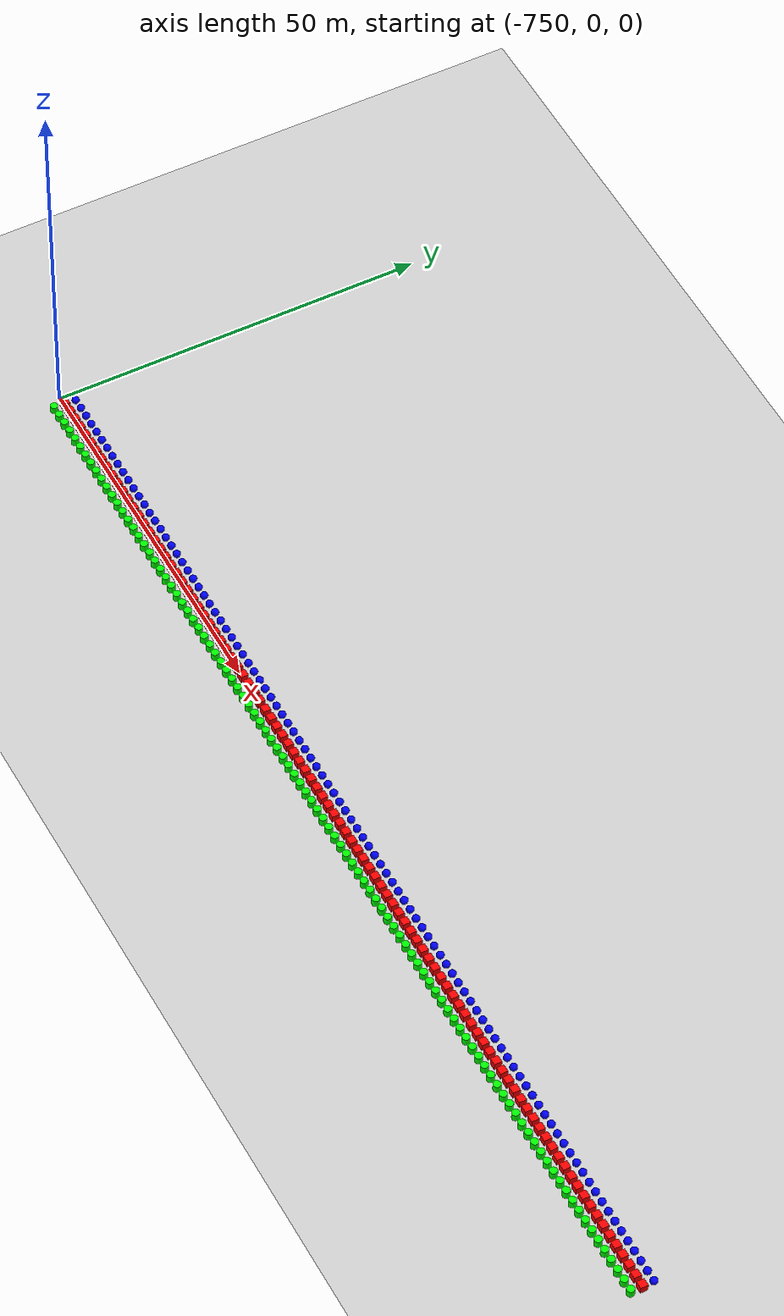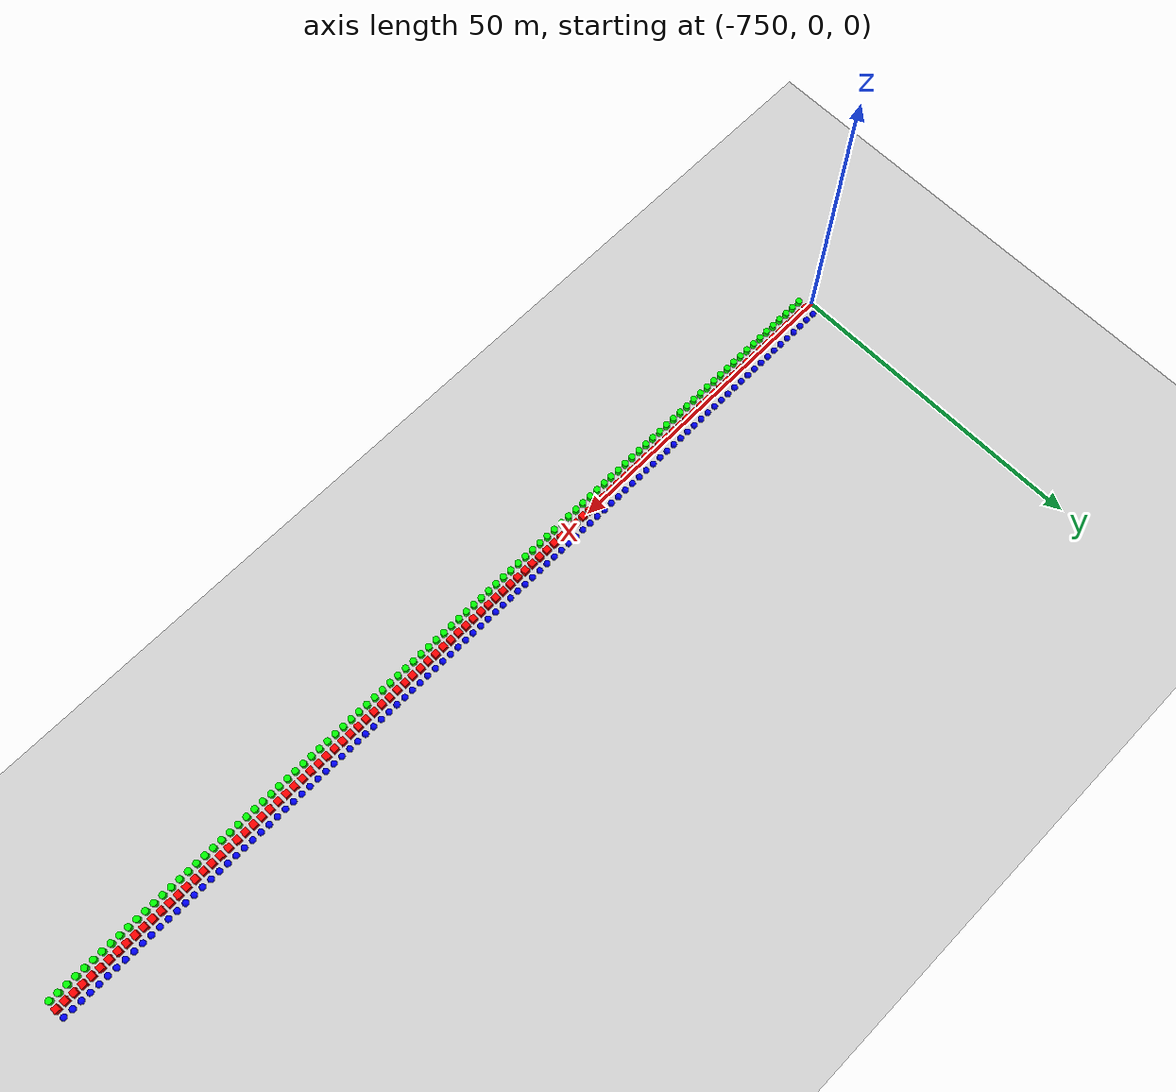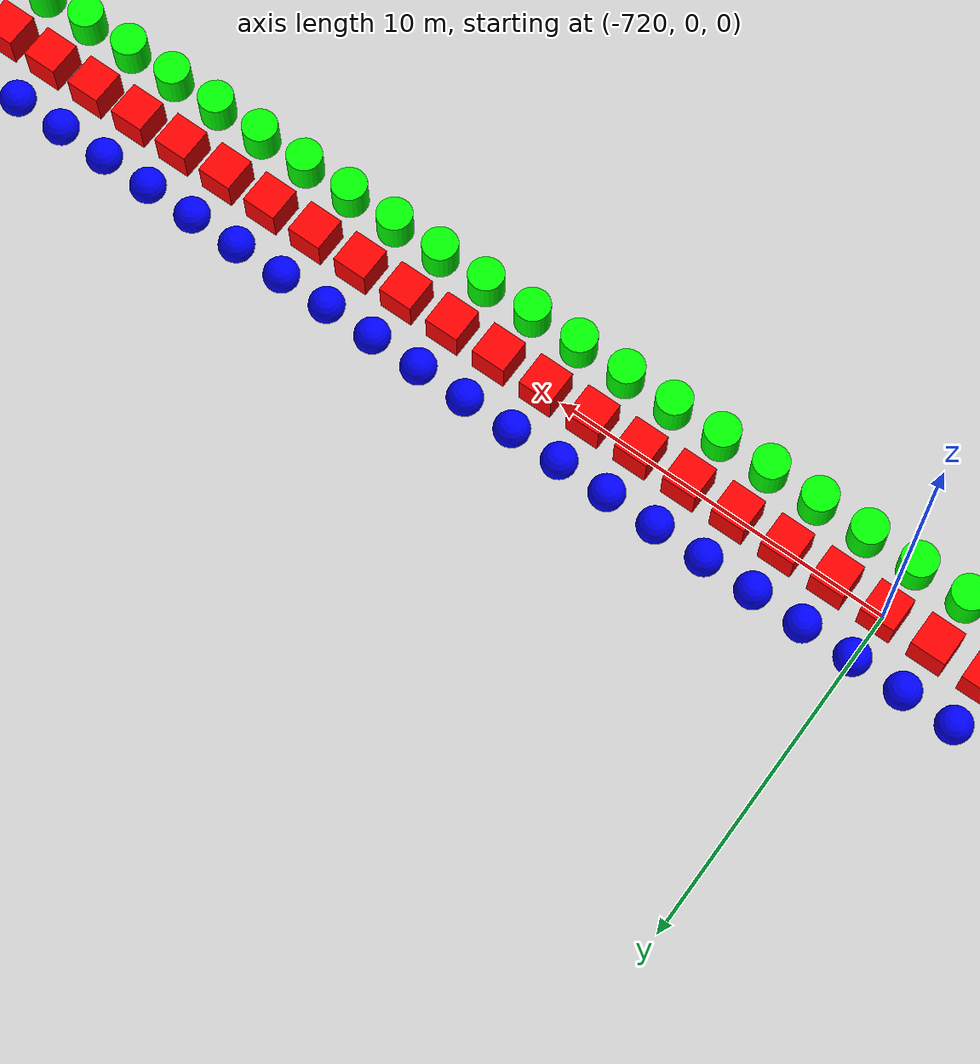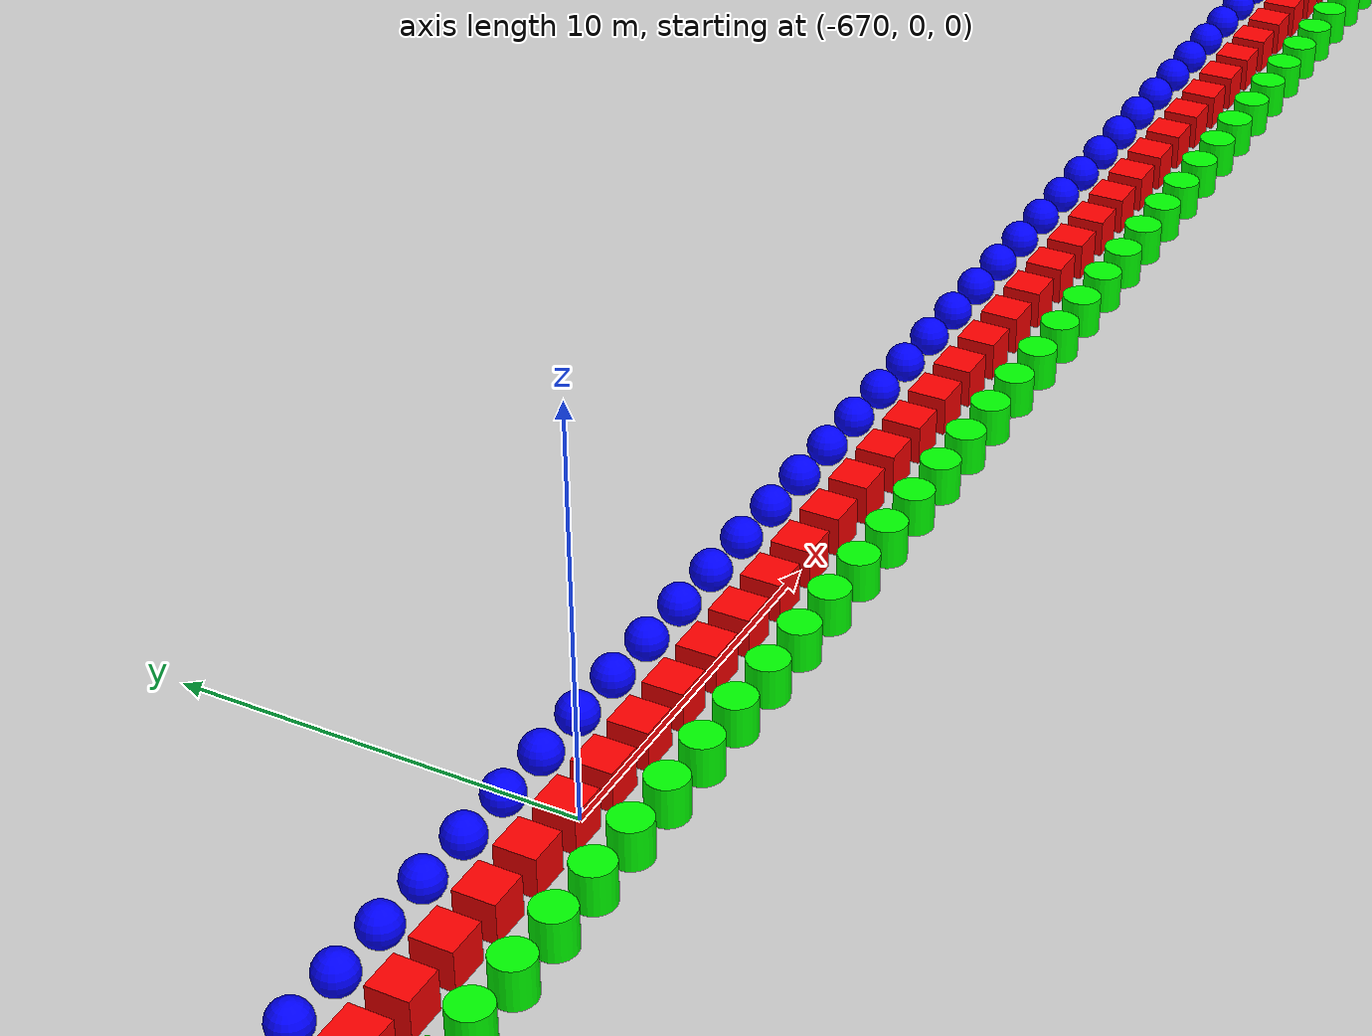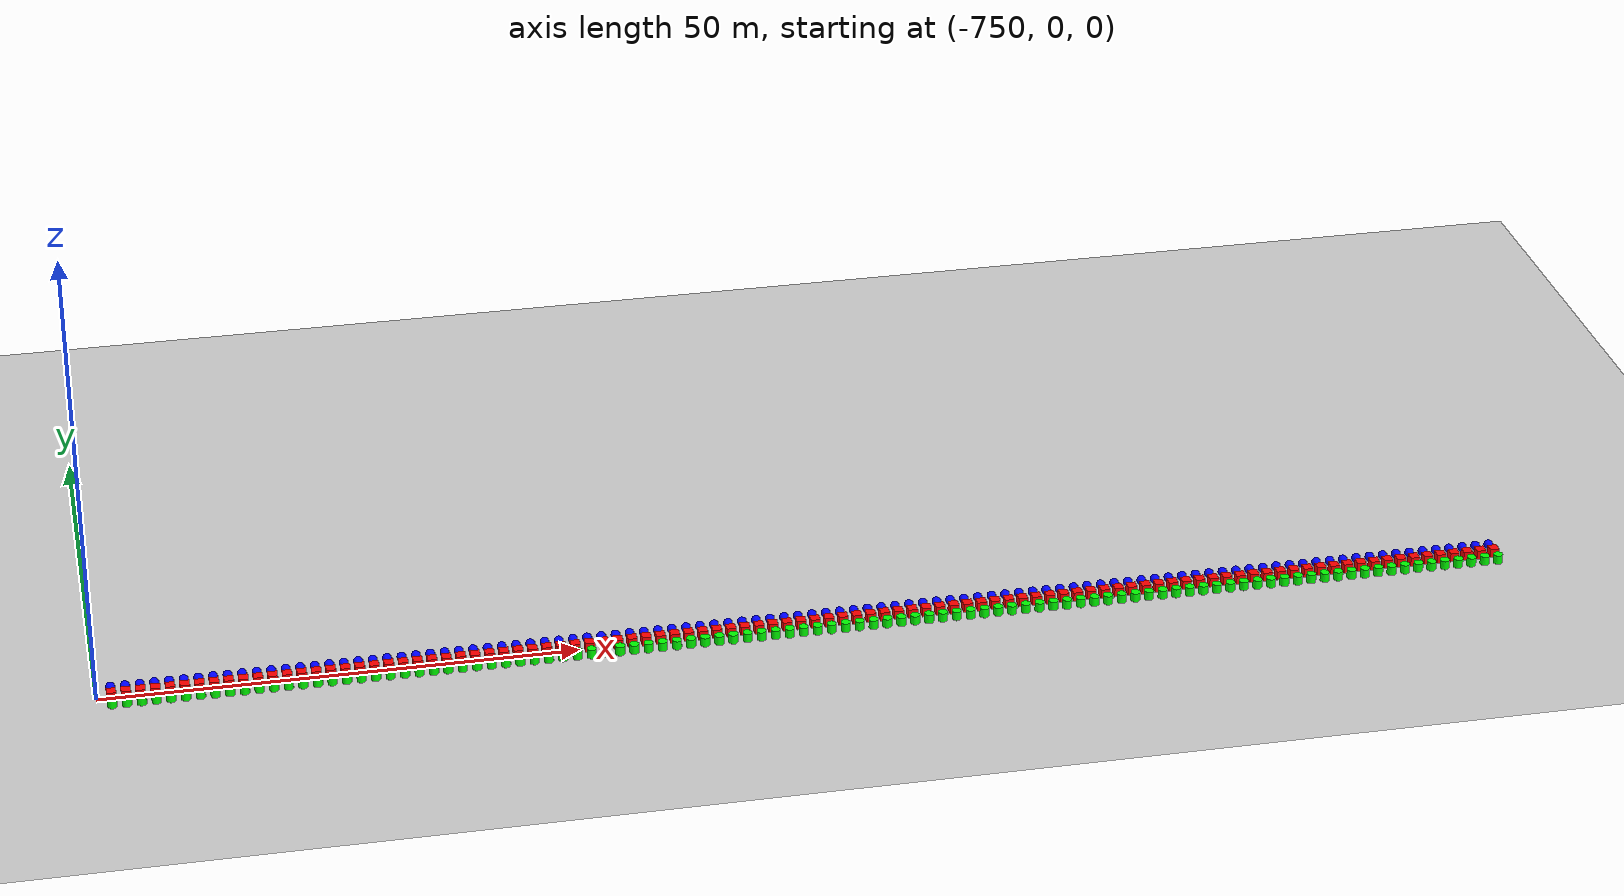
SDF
<?xml version="1.0" ?>
<sdf version="1.6">
  <world name="shapes">
    <model name="ground_plane">
      <static>true</static>
      <link name="link">
        <collision name="collision">
          <geometry>
            <plane>
              <normal>0 0 1</normal>
              <size>100 100</size>
            </plane>
          </geometry>
        </collision>
        <visual name="visual">
          <geometry>
            <plane>
              <normal>0 0 1</normal>
              <size>100 100</size>
            </plane>
          </geometry>
          <material>
            <ambient>0.8 0.8 0.8 1</ambient>
            <diffuse>0.8 0.8 0.8 1</diffuse>
            <specular>0.8 0.8 0.8 1</specular>
          </material>
        </visual>
      </link>
    </model>

    <model name="box_1">
      <static>true</static>
      <pose>-748.5 0 0.5 0 0 0</pose>
      <link name="box_link">
        <inertial>
          <inertia>
            <ixx>1</ixx>
            <ixy>0</ixy>
            <ixz>0</ixz>
            <iyy>1</iyy>
            <iyz>0</iyz>
            <izz>1</izz>
          </inertia>
          <mass>1.0</mass>
        </inertial>
        <collision name="box_collision">
          <geometry>
            <box>
              <size>1 1 1</size>
            </box>
          </geometry>
        </collision>

        <visual name="box_visual">
          <geometry>
            <box>
              <size>1 1 1</size>
            </box>
          </geometry>
          <material>
            <ambient>1 0 0 1</ambient>
            <diffuse>1 0 0 1</diffuse>
            <specular>1 0 0 1</specular>
          </material>
        </visual>
      </link>
    </model>

    <model name="cylinder_1">
      <static>true</static>
      <pose>-748.5 -1.5 0.5 0 0 0</pose>
      <link name="cylinder_link">
        <inertial>
          <inertia>
            <ixx>2</ixx>
            <ixy>0</ixy>
            <ixz>0</ixz>
            <iyy>2</iyy>
            <iyz>0</iyz>
            <izz>2</izz>
          </inertia>
          <mass>2.0</mass>
        </inertial>
        <collision name="cylinder_collision">
          <geometry>
            <cylinder>
              <radius>0.5</radius>
              <length>1.0</length>
            </cylinder>
          </geometry>
        </collision>

        <visual name="cylinder_visual">
          <geometry>
            <cylinder>
              <radius>0.5</radius>
              <length>1.0</length>
            </cylinder>
          </geometry>
          <material>
            <ambient>0 1 0 1</ambient>
            <diffuse>0 1 0 1</diffuse>
            <specular>0 1 0 1</specular>
          </material>
        </visual>
      </link>
    </model>

    <model name="sphere_1">
      <static>true</static>
      <pose>-748.5 1.5 0.5 0 0 0</pose>
      <link name="sphere_link">
        <inertial>
          <inertia>
            <ixx>3</ixx>
            <ixy>0</ixy>
            <ixz>0</ixz>
            <iyy>3</iyy>
            <iyz>0</iyz>
            <izz>3</izz>
          </inertia>
          <mass>3.0</mass>
        </inertial>
        <collision name="sphere_collision">
          <geometry>
            <sphere>
              <radius>0.5</radius>
            </sphere>
          </geometry>
        </collision>

        <visual name="sphere_visual">
          <geometry>
            <sphere>
              <radius>0.5</radius>
            </sphere>
          </geometry>
          <material>
            <ambient>0 0 1 1</ambient>
            <diffuse>0 0 1 1</diffuse>
            <specular>0 0 1 1</specular>
          </material>
        </visual>
      </link>
    </model>

    <model name="box_2">
      <static>true</static>
      <pose>-747.0 0 0.5 0 0 0</pose>
      <link name="box_link">
        <inertial>
          <inertia>
            <ixx>1</ixx>
            <ixy>0</ixy>
            <ixz>0</ixz>
            <iyy>1</iyy>
            <iyz>0</iyz>
            <izz>1</izz>
          </inertia>
          <mass>1.0</mass>
        </inertial>
        <collision name="box_collision">
          <geometry>
            <box>
              <size>1 1 1</size>
            </box>
          </geometry>
        </collision>

        <visual name="box_visual">
          <geometry>
            <box>
              <size>1 1 1</size>
            </box>
          </geometry>
          <material>
            <ambient>1 0 0 1</ambient>
            <diffuse>1 0 0 1</diffuse>
            <specular>1 0 0 1</specular>
          </material>
        </visual>
      </link>
    </model>

    <model name="cylinder_2">
      <static>true</static>
      <pose>-747.0 -1.5 0.5 0 0 0</pose>
      <link name="cylinder_link">
        <inertial>
          <inertia>
            <ixx>2</ixx>
            <ixy>0</ixy>
            <ixz>0</ixz>
            <iyy>2</iyy>
            <iyz>0</iyz>
            <izz>2</izz>
          </inertia>
          <mass>2.0</mass>
        </inertial>
        <collision name="cylinder_collision">
          <geometry>
            <cylinder>
              <radius>0.5</radius>
              <length>1.0</length>
            </cylinder>
          </geometry>
        </collision>

        <visual name="cylinder_visual">
          <geometry>
            <cylinder>
              <radius>0.5</radius>
              <length>1.0</length>
            </cylinder>
          </geometry>
          <material>
            <ambient>0 1 0 1</ambient>
            <diffuse>0 1 0 1</diffuse>
            <specular>0 1 0 1</specular>
          </material>
        </visual>
      </link>
    </model>

    <model name="sphere_2">
      <static>true</static>
      <pose>-747.0 1.5 0.5 0 0 0</pose>
      <link name="sphere_link">
        <inertial>
          <inertia>
            <ixx>3</ixx>
            <ixy>0</ixy>
            <ixz>0</ixz>
            <iyy>3</iyy>
            <iyz>0</iyz>
            <izz>3</izz>
          </inertia>
          <mass>3.0</mass>
        </inertial>
        <collision name="sphere_collision">
          <geometry>
            <sphere>
              <radius>0.5</radius>
            </sphere>
          </geometry>
        </collision>

        <visual name="sphere_visual">
          <geometry>
            <sphere>
              <radius>0.5</radius>
            </sphere>
          </geometry>
          <material>
            <ambient>0 0 1 1</ambient>
            <diffuse>0 0 1 1</diffuse>
            <specular>0 0 1 1</specular>
          </material>
        </visual>
      </link>
    </model>

    <model name="box_3">
      <static>true</static>
      <pose>-745.5 0 0.5 0 0 0</pose>
      <link name="box_link">
        <inertial>
          <inertia>
            <ixx>1</ixx>
            <ixy>0</ixy>
            <ixz>0</ixz>
            <iyy>1</iyy>
            <iyz>0</iyz>
            <izz>1</izz>
          </inertia>
          <mass>1.0</mass>
        </inertial>
        <collision name="box_collision">
          <geometry>
            <box>
              <size>1 1 1</size>
            </box>
          </geometry>
        </collision>

        <visual name="box_visual">
          <geometry>
            <box>
              <size>1 1 1</size>
            </box>
          </geometry>
          <material>
            <ambient>1 0 0 1</ambient>
            <diffuse>1 0 0 1</diffuse>
            <specular>1 0 0 1</specular>
          </material>
        </visual>
      </link>
    </model>

    <model name="cylinder_3">
      <static>true</static>
      <pose>-745.5 -1.5 0.5 0 0 0</pose>
      <link name="cylinder_link">
        <inertial>
          <inertia>
            <ixx>2</ixx>
            <ixy>0</ixy>
            <ixz>0</ixz>
            <iyy>2</iyy>
            <iyz>0</iyz>
            <izz>2</izz>
          </inertia>
          <mass>2.0</mass>
        </inertial>
        <collision name="cylinder_collision">
          <geometry>
            <cylinder>
              <radius>0.5</radius>
              <length>1.0</length>
            </cylinder>
          </geometry>
        </collision>

        <visual name="cylinder_visual">
          <geometry>
            <cylinder>
              <radius>0.5</radius>
              <length>1.0</length>
            </cylinder>
          </geometry>
          <material>
            <ambient>0 1 0 1</ambient>
            <diffuse>0 1 0 1</diffuse>
            <specular>0 1 0 1</specular>
          </material>
        </visual>
      </link>
    </model>

    <model name="sphere_3">
      <static>true</static>
      <pose>-745.5 1.5 0.5 0 0 0</pose>
      <link name="sphere_link">
        <inertial>
          <inertia>
            <ixx>3</ixx>
            <ixy>0</ixy>
            <ixz>0</ixz>
            <iyy>3</iyy>
            <iyz>0</iyz>
            <izz>3</izz>
          </inertia>
          <mass>3.0</mass>
        </inertial>
        <collision name="sphere_collision">
          <geometry>
            <sphere>
              <radius>0.5</radius>
            </sphere>
          </geometry>
        </collision>

        <visual name="sphere_visual">
          <geometry>
            <sphere>
              <radius>0.5</radius>
            </sphere>
          </geometry>
          <material>
            <ambient>0 0 1 1</ambient>
            <diffuse>0 0 1 1</diffuse>
            <specular>0 0 1 1</specular>
          </material>
        </visual>
      </link>
    </model>

    <model name="box_4">
      <static>true</static>
      <pose>-744.0 0 0.5 0 0 0</pose>
      <link name="box_link">
        <inertial>
          <inertia>
            <ixx>1</ixx>
            <ixy>0</ixy>
            <ixz>0</ixz>
            <iyy>1</iyy>
            <iyz>0</iyz>
            <izz>1</izz>
          </inertia>
          <mass>1.0</mass>
        </inertial>
        <collision name="box_collision">
          <geometry>
            <box>
              <size>1 1 1</size>
            </box>
          </geometry>
        </collision>

        <visual name="box_visual">
          <geometry>
            <box>
              <size>1 1 1</size>
            </box>
          </geometry>
          <material>
            <ambient>1 0 0 1</ambient>
            <diffuse>1 0 0 1</diffuse>
            <specular>1 0 0 1</specular>
          </material>
        </visual>
      </link>
    </model>

    <model name="cylinder_4">
      <static>true</static>
      <pose>-744.0 -1.5 0.5 0 0 0</pose>
      <link name="cylinder_link">
        <inertial>
          <inertia>
            <ixx>2</ixx>
            <ixy>0</ixy>
            <ixz>0</ixz>
            <iyy>2</iyy>
            <iyz>0</iyz>
            <izz>2</izz>
          </inertia>
          <mass>2.0</mass>
        </inertial>
        <collision name="cylinder_collision">
          <geometry>
            <cylinder>
              <radius>0.5</radius>
              <length>1.0</length>
            </cylinder>
          </geometry>
        </collision>

        <visual name="cylinder_visual">
          <geometry>
            <cylinder>
              <radius>0.5</radius>
              <length>1.0</length>
            </cylinder>
          </geometry>
          <material>
            <ambient>0 1 0 1</ambient>
            <diffuse>0 1 0 1</diffuse>
            <specular>0 1 0 1</specular>
          </material>
        </visual>
      </link>
    </model>

    <model name="sphere_4">
      <static>true</static>
      <pose>-744.0 1.5 0.5 0 0 0</pose>
      <link name="sphere_link">
        <inertial>
          <inertia>
            <ixx>3</ixx>
            <ixy>0</ixy>
            <ixz>0</ixz>
            <iyy>3</iyy>
            <iyz>0</iyz>
            <izz>3</izz>
          </inertia>
          <mass>3.0</mass>
        </inertial>
        <collision name="sphere_collision">
          <geometry>
            <sphere>
              <radius>0.5</radius>
            </sphere>
          </geometry>
        </collision>

        <visual name="sphere_visual">
          <geometry>
            <sphere>
              <radius>0.5</radius>
            </sphere>
          </geometry>
          <material>
            <ambient>0 0 1 1</ambient>
            <diffuse>0 0 1 1</diffuse>
            <specular>0 0 1 1</specular>
          </material>
        </visual>
      </link>
    </model>

    <model name="box_5">
      <static>true</static>
      <pose>-742.5 0 0.5 0 0 0</pose>
      <link name="box_link">
        <inertial>
          <inertia>
            <ixx>1</ixx>
            <ixy>0</ixy>
            <ixz>0</ixz>
            <iyy>1</iyy>
            <iyz>0</iyz>
            <izz>1</izz>
          </inertia>
          <mass>1.0</mass>
        </inertial>
        <collision name="box_collision">
          <geometry>
            <box>
              <size>1 1 1</size>
            </box>
          </geometry>
        </collision>

        <visual name="box_visual">
          <geometry>
            <box>
              <size>1 1 1</size>
            </box>
          </geometry>
          <material>
            <ambient>1 0 0 1</ambient>
            <diffuse>1 0 0 1</diffuse>
            <specular>1 0 0 1</specular>
          </material>
        </visual>
      </link>
    </model>

    <model name="cylinder_5">
      <static>true</static>
      <pose>-742.5 -1.5 0.5 0 0 0</pose>
      <link name="cylinder_link">
        <inertial>
          <inertia>
            <ixx>2</ixx>
            <ixy>0</ixy>
            <ixz>0</ixz>
            <iyy>2</iyy>
            <iyz>0</iyz>
            <izz>2</izz>
          </inertia>
          <mass>2.0</mass>
        </inertial>
        <collision name="cylinder_collision">
          <geometry>
            <cylinder>
              <radius>0.5</radius>
              <length>1.0</length>
            </cylinder>
          </geometry>
        </collision>

        <visual name="cylinder_visual">
          <geometry>
            <cylinder>
              <radius>0.5</radius>
              <length>1.0</length>
            </cylinder>
          </geometry>
          <material>
            <ambient>0 1 0 1</ambient>
            <diffuse>0 1 0 1</diffuse>
            <specular>0 1 0 1</specular>
          </material>
        </visual>
      </link>
    </model>

    <model name="sphere_5">
      <static>true</static>
      <pose>-742.5 1.5 0.5 0 0 0</pose>
      <link name="sphere_link">
        <inertial>
          <inertia>
            <ixx>3</ixx>
            <ixy>0</ixy>
            <ixz>0</ixz>
            <iyy>3</iyy>
            <iyz>0</iyz>
            <izz>3</izz>
          </inertia>
          <mass>3.0</mass>
        </inertial>
        <collision name="sphere_collision">
          <geometry>
            <sphere>
              <radius>0.5</radius>
            </sphere>
          </geometry>
        </collision>

        <visual name="sphere_visual">
          <geometry>
            <sphere>
              <radius>0.5</radius>
            </sphere>
          </geometry>
          <material>
            <ambient>0 0 1 1</ambient>
            <diffuse>0 0 1 1</diffuse>
            <specular>0 0 1 1</specular>
          </material>
        </visual>
      </link>
    </model>

    <model name="box_6">
      <static>true</static>
      <pose>-741.0 0 0.5 0 0 0</pose>
      <link name="box_link">
        <inertial>
          <inertia>
            <ixx>1</ixx>
            <ixy>0</ixy>
            <ixz>0</ixz>
            <iyy>1</iyy>
            <iyz>0</iyz>
            <izz>1</izz>
          </inertia>
          <mass>1.0</mass>
        </inertial>
        <collision name="box_collision">
          <geometry>
            <box>
              <size>1 1 1</size>
            </box>
          </geometry>
        </collision>

        <visual name="box_visual">
          <geometry>
            <box>
              <size>1 1 1</size>
            </box>
          </geometry>
          <material>
            <ambient>1 0 0 1</ambient>
            <diffuse>1 0 0 1</diffuse>
            <specular>1 0 0 1</specular>
          </material>
        </visual>
      </link>
    </model>

    <model name="cylinder_6">
      <static>true</static>
      <pose>-741.0 -1.5 0.5 0 0 0</pose>
      <link name="cylinder_link">
        <inertial>
          <inertia>
            <ixx>2</ixx>
            <ixy>0</ixy>
            <ixz>0</ixz>
            <iyy>2</iyy>
            <iyz>0</iyz>
            <izz>2</izz>
          </inertia>
          <mass>2.0</mass>
        </inertial>
        <collision name="cylinder_collision">
          <geometry>
            <cylinder>
              <radius>0.5</radius>
              <length>1.0</length>
            </cylinder>
          </geometry>
        </collision>

        <visual name="cylinder_visual">
          <geometry>
            <cylinder>
              <radius>0.5</radius>
              <length>1.0</length>
            </cylinder>
          </geometry>
          <material>
            <ambient>0 1 0 1</ambient>
            <diffuse>0 1 0 1</diffuse>
            <specular>0 1 0 1</specular>
          </material>
        </visual>
      </link>
    </model>

    <model name="sphere_6">
      <static>true</static>
      <pose>-741.0 1.5 0.5 0 0 0</pose>
      <link name="sphere_link">
        <inertial>
          <inertia>
            <ixx>3</ixx>
            <ixy>0</ixy>
            <ixz>0</ixz>
            <iyy>3</iyy>
            <iyz>0</iyz>
            <izz>3</izz>
          </inertia>
          <mass>3.0</mass>
        </inertial>
        <collision name="sphere_collision">
          <geometry>
            <sphere>
              <radius>0.5</radius>
            </sphere>
          </geometry>
        </collision>

        <visual name="sphere_visual">
          <geometry>
            <sphere>
              <radius>0.5</radius>
            </sphere>
          </geometry>
          <material>
            <ambient>0 0 1 1</ambient>
            <diffuse>0 0 1 1</diffuse>
            <specular>0 0 1 1</specular>
          </material>
        </visual>
      </link>
    </model>

    <model name="box_7">
      <static>true</static>
      <pose>-739.5 0 0.5 0 0 0</pose>
      <link name="box_link">
        <inertial>
          <inertia>
            <ixx>1</ixx>
            <ixy>0</ixy>
            <ixz>0</ixz>
            <iyy>1</iyy>
            <iyz>0</iyz>
            <izz>1</izz>
          </inertia>
          <mass>1.0</mass>
        </inertial>
        <collision name="box_collision">
          <geometry>
            <box>
              <size>1 1 1</size>
            </box>
          </geometry>
        </collision>

        <visual name="box_visual">
          <geometry>
            <box>
              <size>1 1 1</size>
            </box>
          </geometry>
          <material>
            <ambient>1 0 0 1</ambient>
            <diffuse>1 0 0 1</diffuse>
            <specular>1 0 0 1</specular>
          </material>
        </visual>
      </link>
    </model>

    <model name="cylinder_7">
      <static>true</static>
      <pose>-739.5 -1.5 0.5 0 0 0</pose>
      <link name="cylinder_link">
        <inertial>
          <inertia>
            <ixx>2</ixx>
            <ixy>0</ixy>
            <ixz>0</ixz>
            <iyy>2</iyy>
            <iyz>0</iyz>
            <izz>2</izz>
          </inertia>
          <mass>2.0</mass>
        </inertial>
        <collision name="cylinder_collision">
          <geometry>
            <cylinder>
              <radius>0.5</radius>
              <length>1.0</length>
            </cylinder>
          </geometry>
        </collision>

        <visual name="cylinder_visual">
          <geometry>
            <cylinder>
              <radius>0.5</radius>
              <length>1.0</length>
            </cylinder>
          </geometry>
          <material>
            <ambient>0 1 0 1</ambient>
            <diffuse>0 1 0 1</diffuse>
            <specular>0 1 0 1</specular>
          </material>
        </visual>
      </link>
    </model>

    <model name="sphere_7">
      <static>true</static>
      <pose>-739.5 1.5 0.5 0 0 0</pose>
      <link name="sphere_link">
        <inertial>
          <inertia>
            <ixx>3</ixx>
            <ixy>0</ixy>
            <ixz>0</ixz>
            <iyy>3</iyy>
            <iyz>0</iyz>
            <izz>3</izz>
          </inertia>
          <mass>3.0</mass>
        </inertial>
        <collision name="sphere_collision">
          <geometry>
            <sphere>
              <radius>0.5</radius>
            </sphere>
          </geometry>
        </collision>

        <visual name="sphere_visual">
          <geometry>
            <sphere>
              <radius>0.5</radius>
            </sphere>
          </geometry>
          <material>
            <ambient>0 0 1 1</ambient>
            <diffuse>0 0 1 1</diffuse>
            <specular>0 0 1 1</specular>
          </material>
        </visual>
      </link>
    </model>

    <model name="box_8">
      <static>true</static>
      <pose>-738.0 0 0.5 0 0 0</pose>
      <link name="box_link">
        <inertial>
          <inertia>
            <ixx>1</ixx>
            <ixy>0</ixy>
            <ixz>0</ixz>
            <iyy>1</iyy>
            <iyz>0</iyz>
            <izz>1</izz>
          </inertia>
          <mass>1.0</mass>
        </inertial>
        <collision name="box_collision">
          <geometry>
            <box>
              <size>1 1 1</size>
            </box>
          </geometry>
        </collision>

        <visual name="box_visual">
          <geometry>
            <box>
              <size>1 1 1</size>
            </box>
          </geometry>
          <material>
            <ambient>1 0 0 1</ambient>
            <diffuse>1 0 0 1</diffuse>
            <specular>1 0 0 1</specular>
          </material>
        </visual>
      </link>
    </model>

    <model name="cylinder_8">
      <static>true</static>
      <pose>-738.0 -1.5 0.5 0 0 0</pose>
      <link name="cylinder_link">
        <inertial>
          <inertia>
            <ixx>2</ixx>
            <ixy>0</ixy>
            <ixz>0</ixz>
            <iyy>2</iyy>
            <iyz>0</iyz>
            <izz>2</izz>
          </inertia>
          <mass>2.0</mass>
        </inertial>
        <collision name="cylinder_collision">
          <geometry>
            <cylinder>
              <radius>0.5</radius>
              <length>1.0</length>
            </cylinder>
          </geometry>
        </collision>

        <visual name="cylinder_visual">
          <geometry>
            <cylinder>
              <radius>0.5</radius>
              <length>1.0</length>
            </cylinder>
          </geometry>
          <material>
            <ambient>0 1 0 1</ambient>
            <diffuse>0 1 0 1</diffuse>
            <specular>0 1 0 1</specular>
          </material>
        </visual>
      </link>
    </model>

    <model name="sphere_8">
      <static>true</static>
      <pose>-738.0 1.5 0.5 0 0 0</pose>
      <link name="sphere_link">
        <inertial>
          <inertia>
            <ixx>3</ixx>
            <ixy>0</ixy>
            <ixz>0</ixz>
            <iyy>3</iyy>
            <iyz>0</iyz>
            <izz>3</izz>
          </inertia>
          <mass>3.0</mass>
        </inertial>
        <collision name="sphere_collision">
          <geometry>
            <sphere>
              <radius>0.5</radius>
            </sphere>
          </geometry>
        </collision>

        <visual name="sphere_visual">
          <geometry>
            <sphere>
              <radius>0.5</radius>
            </sphere>
          </geometry>
          <material>
            <ambient>0 0 1 1</ambient>
            <diffuse>0 0 1 1</diffuse>
            <specular>0 0 1 1</specular>
          </material>
        </visual>
      </link>
    </model>

    <model name="box_9">
      <static>true</static>
      <pose>-736.5 0 0.5 0 0 0</pose>
      <link name="box_link">
        <inertial>
          <inertia>
            <ixx>1</ixx>
            <ixy>0</ixy>
            <ixz>0</ixz>
            <iyy>1</iyy>
            <iyz>0</iyz>
            <izz>1</izz>
          </inertia>
          <mass>1.0</mass>
        </inertial>
        <collision name="box_collision">
          <geometry>
            <box>
              <size>1 1 1</size>
            </box>
          </geometry>
        </collision>

        <visual name="box_visual">
          <geometry>
            <box>
              <size>1 1 1</size>
            </box>
          </geometry>
          <material>
            <ambient>1 0 0 1</ambient>
            <diffuse>1 0 0 1</diffuse>
            <specular>1 0 0 1</specular>
          </material>
        </visual>
      </link>
    </model>

    <model name="cylinder_9">
      <static>true</static>
      <pose>-736.5 -1.5 0.5 0 0 0</pose>
      <link name="cylinder_link">
        <inertial>
          <inertia>
            <ixx>2</ixx>
            <ixy>0</ixy>
            <ixz>0</ixz>
            <iyy>2</iyy>
            <iyz>0</iyz>
            <izz>2</izz>
          </inertia>
          <mass>2.0</mass>
        </inertial>
        <collision name="cylinder_collision">
          <geometry>
            <cylinder>
              <radius>0.5</radius>
              <length>1.0</length>
            </cylinder>
          </geometry>
        </collision>

        <visual name="cylinder_visual">
          <geometry>
            <cylinder>
              <radius>0.5</radius>
              <length>1.0</length>
            </cylinder>
          </geometry>
          <material>
            <ambient>0 1 0 1</ambient>
            <diffuse>0 1 0 1</diffuse>
            <specular>0 1 0 1</specular>
          </material>
        </visual>
      </link>
    </model>

    <model name="sphere_9">
      <static>true</static>
      <pose>-736.5 1.5 0.5 0 0 0</pose>
      <link name="sphere_link">
        <inertial>
          <inertia>
            <ixx>3</ixx>
            <ixy>0</ixy>
            <ixz>0</ixz>
            <iyy>3</iyy>
            <iyz>0</iyz>
            <izz>3</izz>
          </inertia>
          <mass>3.0</mass>
        </inertial>
        <collision name="sphere_collision">
          <geometry>
            <sphere>
              <radius>0.5</radius>
            </sphere>
          </geometry>
        </collision>

        <visual name="sphere_visual">
          <geometry>
            <sphere>
              <radius>0.5</radius>
            </sphere>
          </geometry>
          <material>
            <ambient>0 0 1 1</ambient>
            <diffuse>0 0 1 1</diffuse>
            <specular>0 0 1 1</specular>
          </material>
        </visual>
      </link>
    </model>

    <model name="box_10">
      <static>true</static>
      <pose>-735.0 0 0.5 0 0 0</pose>
      <link name="box_link">
        <inertial>
          <inertia>
            <ixx>1</ixx>
            <ixy>0</ixy>
            <ixz>0</ixz>
            <iyy>1</iyy>
            <iyz>0</iyz>
            <izz>1</izz>
          </inertia>
          <mass>1.0</mass>
        </inertial>
        <collision name="box_collision">
          <geometry>
            <box>
              <size>1 1 1</size>
            </box>
          </geometry>
        </collision>

        <visual name="box_visual">
          <geometry>
            <box>
              <size>1 1 1</size>
            </box>
          </geometry>
          <material>
            <ambient>1 0 0 1</ambient>
            <diffuse>1 0 0 1</diffuse>
            <specular>1 0 0 1</specular>
          </material>
        </visual>
      </link>
    </model>

    <model name="cylinder_10">
      <static>true</static>
      <pose>-735.0 -1.5 0.5 0 0 0</pose>
      <link name="cylinder_link">
        <inertial>
          <inertia>
            <ixx>2</ixx>
            <ixy>0</ixy>
            <ixz>0</ixz>
            <iyy>2</iyy>
            <iyz>0</iyz>
            <izz>2</izz>
          </inertia>
          <mass>2.0</mass>
        </inertial>
        <collision name="cylinder_collision">
          <geometry>
            <cylinder>
              <radius>0.5</radius>
              <length>1.0</length>
            </cylinder>
          </geometry>
        </collision>

        <visual name="cylinder_visual">
          <geometry>
            <cylinder>
              <radius>0.5</radius>
              <length>1.0</length>
            </cylinder>
          </geometry>
          <material>
            <ambient>0 1 0 1</ambient>
            <diffuse>0 1 0 1</diffuse>
            <specular>0 1 0 1</specular>
          </material>
        </visual>
      </link>
    </model>

    <model name="sphere_10">
      <static>true</static>
      <pose>-735.0 1.5 0.5 0 0 0</pose>
      <link name="sphere_link">
        <inertial>
          <inertia>
            <ixx>3</ixx>
            <ixy>0</ixy>
            <ixz>0</ixz>
            <iyy>3</iyy>
            <iyz>0</iyz>
            <izz>3</izz>
          </inertia>
          <mass>3.0</mass>
        </inertial>
        <collision name="sphere_collision">
          <geometry>
            <sphere>
              <radius>0.5</radius>
            </sphere>
          </geometry>
        </collision>

        <visual name="sphere_visual">
          <geometry>
            <sphere>
              <radius>0.5</radius>
            </sphere>
          </geometry>
          <material>
            <ambient>0 0 1 1</ambient>
            <diffuse>0 0 1 1</diffuse>
            <specular>0 0 1 1</specular>
          </material>
        </visual>
      </link>
    </model>

    <model name="box_11">
      <static>true</static>
      <pose>-733.5 0 0.5 0 0 0</pose>
      <link name="box_link">
        <inertial>
          <inertia>
            <ixx>1</ixx>
            <ixy>0</ixy>
            <ixz>0</ixz>
            <iyy>1</iyy>
            <iyz>0</iyz>
            <izz>1</izz>
          </inertia>
          <mass>1.0</mass>
        </inertial>
        <collision name="box_collision">
          <geometry>
            <box>
              <size>1 1 1</size>
            </box>
          </geometry>
        </collision>

        <visual name="box_visual">
          <geometry>
            <box>
              <size>1 1 1</size>
            </box>
          </geometry>
          <material>
            <ambient>1 0 0 1</ambient>
            <diffuse>1 0 0 1</diffuse>
            <specular>1 0 0 1</specular>
          </material>
        </visual>
      </link>
    </model>

    <model name="cylinder_11">
      <static>true</static>
      <pose>-733.5 -1.5 0.5 0 0 0</pose>
      <link name="cylinder_link">
        <inertial>
          <inertia>
            <ixx>2</ixx>
            <ixy>0</ixy>
            <ixz>0</ixz>
            <iyy>2</iyy>
            <iyz>0</iyz>
            <izz>2</izz>
          </inertia>
          <mass>2.0</mass>
        </inertial>
        <collision name="cylinder_collision">
          <geometry>
            <cylinder>
              <radius>0.5</radius>
              <length>1.0</length>
            </cylinder>
          </geometry>
        </collision>

        <visual name="cylinder_visual">
          <geometry>
            <cylinder>
              <radius>0.5</radius>
              <length>1.0</length>
            </cylinder>
          </geometry>
          <material>
            <ambient>0 1 0 1</ambient>
            <diffuse>0 1 0 1</diffuse>
            <specular>0 1 0 1</specular>
          </material>
        </visual>
      </link>
    </model>

    <model name="sphere_11">
      <static>true</static>
      <pose>-733.5 1.5 0.5 0 0 0</pose>
      <link name="sphere_link">
        <inertial>
          <inertia>
            <ixx>3</ixx>
            <ixy>0</ixy>
            <ixz>0</ixz>
            <iyy>3</iyy>
            <iyz>0</iyz>
            <izz>3</izz>
          </inertia>
          <mass>3.0</mass>
        </inertial>
        <collision name="sphere_collision">
          <geometry>
            <sphere>
              <radius>0.5</radius>
            </sphere>
          </geometry>
        </collision>

        <visual name="sphere_visual">
          <geometry>
            <sphere>
              <radius>0.5</radius>
            </sphere>
          </geometry>
          <material>
            <ambient>0 0 1 1</ambient>
            <diffuse>0 0 1 1</diffuse>
            <specular>0 0 1 1</specular>
          </material>
        </visual>
      </link>
    </model>

    <model name="box_12">
      <static>true</static>
      <pose>-732.0 0 0.5 0 0 0</pose>
      <link name="box_link">
        <inertial>
          <inertia>
            <ixx>1</ixx>
            <ixy>0</ixy>
            <ixz>0</ixz>
            <iyy>1</iyy>
            <iyz>0</iyz>
            <izz>1</izz>
          </inertia>
          <mass>1.0</mass>
        </inertial>
        <collision name="box_collision">
          <geometry>
            <box>
              <size>1 1 1</size>
            </box>
          </geometry>
        </collision>

        <visual name="box_visual">
          <geometry>
            <box>
              <size>1 1 1</size>
            </box>
          </geometry>
          <material>
            <ambient>1 0 0 1</ambient>
            <diffuse>1 0 0 1</diffuse>
            <specular>1 0 0 1</specular>
          </material>
        </visual>
      </link>
    </model>

    <model name="cylinder_12">
      <static>true</static>
      <pose>-732.0 -1.5 0.5 0 0 0</pose>
      <link name="cylinder_link">
        <inertial>
          <inertia>
            <ixx>2</ixx>
            <ixy>0</ixy>
            <ixz>0</ixz>
            <iyy>2</iyy>
            <iyz>0</iyz>
            <izz>2</izz>
          </inertia>
          <mass>2.0</mass>
        </inertial>
        <collision name="cylinder_collision">
          <geometry>
            <cylinder>
              <radius>0.5</radius>
              <length>1.0</length>
            </cylinder>
          </geometry>
        </collision>

        <visual name="cylinder_visual">
          <geometry>
            <cylinder>
              <radius>0.5</radius>
              <length>1.0</length>
            </cylinder>
          </geometry>
          <material>
            <ambient>0 1 0 1</ambient>
            <diffuse>0 1 0 1</diffuse>
            <specular>0 1 0 1</specular>
          </material>
        </visual>
      </link>
    </model>

    <model name="sphere_12">
      <static>true</static>
      <pose>-732.0 1.5 0.5 0 0 0</pose>
      <link name="sphere_link">
        <inertial>
          <inertia>
            <ixx>3</ixx>
            <ixy>0</ixy>
            <ixz>0</ixz>
            <iyy>3</iyy>
            <iyz>0</iyz>
            <izz>3</izz>
          </inertia>
          <mass>3.0</mass>
        </inertial>
        <collision name="sphere_collision">
          <geometry>
            <sphere>
              <radius>0.5</radius>
            </sphere>
          </geometry>
        </collision>

        <visual name="sphere_visual">
          <geometry>
            <sphere>
              <radius>0.5</radius>
            </sphere>
          </geometry>
          <material>
            <ambient>0 0 1 1</ambient>
            <diffuse>0 0 1 1</diffuse>
            <specular>0 0 1 1</specular>
          </material>
        </visual>
      </link>
    </model>

    <model name="box_13">
      <static>true</static>
      <pose>-730.5 0 0.5 0 0 0</pose>
      <link name="box_link">
        <inertial>
          <inertia>
            <ixx>1</ixx>
            <ixy>0</ixy>
            <ixz>0</ixz>
            <iyy>1</iyy>
            <iyz>0</iyz>
            <izz>1</izz>
          </inertia>
          <mass>1.0</mass>
        </inertial>
        <collision name="box_collision">
          <geometry>
            <box>
              <size>1 1 1</size>
            </box>
          </geometry>
        </collision>

        <visual name="box_visual">
          <geometry>
            <box>
              <size>1 1 1</size>
            </box>
          </geometry>
          <material>
            <ambient>1 0 0 1</ambient>
            <diffuse>1 0 0 1</diffuse>
            <specular>1 0 0 1</specular>
          </material>
        </visual>
      </link>
    </model>

    <model name="cylinder_13">
      <static>true</static>
      <pose>-730.5 -1.5 0.5 0 0 0</pose>
      <link name="cylinder_link">
        <inertial>
          <inertia>
            <ixx>2</ixx>
            <ixy>0</ixy>
            <ixz>0</ixz>
            <iyy>2</iyy>
            <iyz>0</iyz>
            <izz>2</izz>
          </inertia>
          <mass>2.0</mass>
        </inertial>
        <collision name="cylinder_collision">
          <geometry>
            <cylinder>
              <radius>0.5</radius>
              <length>1.0</length>
            </cylinder>
          </geometry>
        </collision>

        <visual name="cylinder_visual">
          <geometry>
            <cylinder>
              <radius>0.5</radius>
              <length>1.0</length>
            </cylinder>
          </geometry>
          <material>
            <ambient>0 1 0 1</ambient>
            <diffuse>0 1 0 1</diffuse>
            <specular>0 1 0 1</specular>
          </material>
        </visual>
      </link>
    </model>

    <model name="sphere_13">
      <static>true</static>
      <pose>-730.5 1.5 0.5 0 0 0</pose>
      <link name="sphere_link">
        <inertial>
          <inertia>
            <ixx>3</ixx>
            <ixy>0</ixy>
            <ixz>0</ixz>
            <iyy>3</iyy>
            <iyz>0</iyz>
            <izz>3</izz>
          </inertia>
          <mass>3.0</mass>
        </inertial>
        <collision name="sphere_collision">
          <geometry>
            <sphere>
              <radius>0.5</radius>
            </sphere>
          </geometry>
        </collision>

        <visual name="sphere_visual">
          <geometry>
            <sphere>
              <radius>0.5</radius>
            </sphere>
          </geometry>
          <material>
            <ambient>0 0 1 1</ambient>
            <diffuse>0 0 1 1</diffuse>
            <specular>0 0 1 1</specular>
          </material>
        </visual>
      </link>
    </model>

    <model name="box_14">
      <static>true</static>
      <pose>-729.0 0 0.5 0 0 0</pose>
      <link name="box_link">
        <inertial>
          <inertia>
            <ixx>1</ixx>
            <ixy>0</ixy>
            <ixz>0</ixz>
            <iyy>1</iyy>
            <iyz>0</iyz>
            <izz>1</izz>
          </inertia>
          <mass>1.0</mass>
        </inertial>
        <collision name="box_collision">
          <geometry>
            <box>
              <size>1 1 1</size>
            </box>
          </geometry>
        </collision>

        <visual name="box_visual">
          <geometry>
            <box>
              <size>1 1 1</size>
            </box>
          </geometry>
          <material>
            <ambient>1 0 0 1</ambient>
            <diffuse>1 0 0 1</diffuse>
            <specular>1 0 0 1</specular>
          </material>
        </visual>
      </link>
    </model>

    <model name="cylinder_14">
      <static>true</static>
      <pose>-729.0 -1.5 0.5 0 0 0</pose>
      <link name="cylinder_link">
        <inertial>
          <inertia>
            <ixx>2</ixx>
            <ixy>0</ixy>
            <ixz>0</ixz>
            <iyy>2</iyy>
            <iyz>0</iyz>
            <izz>2</izz>
          </inertia>
          <mass>2.0</mass>
        </inertial>
        <collision name="cylinder_collision">
          <geometry>
            <cylinder>
              <radius>0.5</radius>
              <length>1.0</length>
            </cylinder>
          </geometry>
        </collision>

        <visual name="cylinder_visual">
          <geometry>
            <cylinder>
              <radius>0.5</radius>
              <length>1.0</length>
            </cylinder>
          </geometry>
          <material>
            <ambient>0 1 0 1</ambient>
            <diffuse>0 1 0 1</diffuse>
            <specular>0 1 0 1</specular>
          </material>
        </visual>
      </link>
    </model>

    <model name="sphere_14">
      <static>true</static>
      <pose>-729.0 1.5 0.5 0 0 0</pose>
      <link name="sphere_link">
        <inertial>
          <inertia>
            <ixx>3</ixx>
            <ixy>0</ixy>
            <ixz>0</ixz>
            <iyy>3</iyy>
            <iyz>0</iyz>
            <izz>3</izz>
          </inertia>
          <mass>3.0</mass>
        </inertial>
        <collision name="sphere_collision">
          <geometry>
            <sphere>
              <radius>0.5</radius>
            </sphere>
          </geometry>
        </collision>

        <visual name="sphere_visual">
          <geometry>
            <sphere>
              <radius>0.5</radius>
            </sphere>
          </geometry>
          <material>
            <ambient>0 0 1 1</ambient>
            <diffuse>0 0 1 1</diffuse>
            <specular>0 0 1 1</specular>
          </material>
        </visual>
      </link>
    </model>

    <model name="box_15">
      <static>true</static>
      <pose>-727.5 0 0.5 0 0 0</pose>
      <link name="box_link">
        <inertial>
          <inertia>
            <ixx>1</ixx>
            <ixy>0</ixy>
            <ixz>0</ixz>
            <iyy>1</iyy>
            <iyz>0</iyz>
            <izz>1</izz>
          </inertia>
          <mass>1.0</mass>
        </inertial>
        <collision name="box_collision">
          <geometry>
            <box>
              <size>1 1 1</size>
            </box>
          </geometry>
        </collision>

        <visual name="box_visual">
          <geometry>
            <box>
              <size>1 1 1</size>
            </box>
          </geometry>
          <material>
            <ambient>1 0 0 1</ambient>
            <diffuse>1 0 0 1</diffuse>
            <specular>1 0 0 1</specular>
          </material>
        </visual>
      </link>
    </model>

    <model name="cylinder_15">
      <static>true</static>
      <pose>-727.5 -1.5 0.5 0 0 0</pose>
      <link name="cylinder_link">
        <inertial>
          <inertia>
            <ixx>2</ixx>
            <ixy>0</ixy>
            <ixz>0</ixz>
            <iyy>2</iyy>
            <iyz>0</iyz>
            <izz>2</izz>
          </inertia>
          <mass>2.0</mass>
        </inertial>
        <collision name="cylinder_collision">
          <geometry>
            <cylinder>
              <radius>0.5</radius>
              <length>1.0</length>
            </cylinder>
          </geometry>
        </collision>

        <visual name="cylinder_visual">
          <geometry>
            <cylinder>
              <radius>0.5</radius>
              <length>1.0</length>
            </cylinder>
          </geometry>
          <material>
            <ambient>0 1 0 1</ambient>
            <diffuse>0 1 0 1</diffuse>
            <specular>0 1 0 1</specular>
          </material>
        </visual>
      </link>
    </model>

    <model name="sphere_15">
      <static>true</static>
      <pose>-727.5 1.5 0.5 0 0 0</pose>
      <link name="sphere_link">
        <inertial>
          <inertia>
            <ixx>3</ixx>
            <ixy>0</ixy>
            <ixz>0</ixz>
            <iyy>3</iyy>
            <iyz>0</iyz>
            <izz>3</izz>
          </inertia>
          <mass>3.0</mass>
        </inertial>
        <collision name="sphere_collision">
          <geometry>
            <sphere>
              <radius>0.5</radius>
            </sphere>
          </geometry>
        </collision>

        <visual name="sphere_visual">
          <geometry>
            <sphere>
              <radius>0.5</radius>
            </sphere>
          </geometry>
          <material>
            <ambient>0 0 1 1</ambient>
            <diffuse>0 0 1 1</diffuse>
            <specular>0 0 1 1</specular>
          </material>
        </visual>
      </link>
    </model>

    <model name="box_16">
      <static>true</static>
      <pose>-726.0 0 0.5 0 0 0</pose>
      <link name="box_link">
        <inertial>
          <inertia>
            <ixx>1</ixx>
            <ixy>0</ixy>
            <ixz>0</ixz>
            <iyy>1</iyy>
            <iyz>0</iyz>
            <izz>1</izz>
          </inertia>
          <mass>1.0</mass>
        </inertial>
        <collision name="box_collision">
          <geometry>
            <box>
              <size>1 1 1</size>
            </box>
          </geometry>
        </collision>

        <visual name="box_visual">
          <geometry>
            <box>
              <size>1 1 1</size>
            </box>
          </geometry>
          <material>
            <ambient>1 0 0 1</ambient>
            <diffuse>1 0 0 1</diffuse>
            <specular>1 0 0 1</specular>
          </material>
        </visual>
      </link>
    </model>

    <model name="cylinder_16">
      <static>true</static>
      <pose>-726.0 -1.5 0.5 0 0 0</pose>
      <link name="cylinder_link">
        <inertial>
          <inertia>
            <ixx>2</ixx>
            <ixy>0</ixy>
            <ixz>0</ixz>
            <iyy>2</iyy>
            <iyz>0</iyz>
            <izz>2</izz>
          </inertia>
          <mass>2.0</mass>
        </inertial>
        <collision name="cylinder_collision">
          <geometry>
            <cylinder>
              <radius>0.5</radius>
              <length>1.0</length>
            </cylinder>
          </geometry>
        </collision>

        <visual name="cylinder_visual">
          <geometry>
            <cylinder>
              <radius>0.5</radius>
              <length>1.0</length>
            </cylinder>
          </geometry>
          <material>
            <ambient>0 1 0 1</ambient>
            <diffuse>0 1 0 1</diffuse>
            <specular>0 1 0 1</specular>
          </material>
        </visual>
      </link>
    </model>

    <model name="sphere_16">
      <static>true</static>
      <pose>-726.0 1.5 0.5 0 0 0</pose>
      <link name="sphere_link">
        <inertial>
          <inertia>
            <ixx>3</ixx>
            <ixy>0</ixy>
            <ixz>0</ixz>
            <iyy>3</iyy>
            <iyz>0</iyz>
            <izz>3</izz>
          </inertia>
          <mass>3.0</mass>
        </inertial>
        <collision name="sphere_collision">
          <geometry>
            <sphere>
              <radius>0.5</radius>
            </sphere>
          </geometry>
        </collision>

        <visual name="sphere_visual">
          <geometry>
            <sphere>
              <radius>0.5</radius>
            </sphere>
          </geometry>
          <material>
            <ambient>0 0 1 1</ambient>
            <diffuse>0 0 1 1</diffuse>
            <specular>0 0 1 1</specular>
          </material>
        </visual>
      </link>
    </model>

    <model name="box_17">
      <static>true</static>
      <pose>-724.5 0 0.5 0 0 0</pose>
      <link name="box_link">
        <inertial>
          <inertia>
            <ixx>1</ixx>
            <ixy>0</ixy>
            <ixz>0</ixz>
            <iyy>1</iyy>
            <iyz>0</iyz>
            <izz>1</izz>
          </inertia>
          <mass>1.0</mass>
        </inertial>
        <collision name="box_collision">
          <geometry>
            <box>
              <size>1 1 1</size>
            </box>
          </geometry>
        </collision>

        <visual name="box_visual">
          <geometry>
            <box>
              <size>1 1 1</size>
            </box>
          </geometry>
          <material>
            <ambient>1 0 0 1</ambient>
            <diffuse>1 0 0 1</diffuse>
            <specular>1 0 0 1</specular>
          </material>
        </visual>
      </link>
    </model>

    <model name="cylinder_17">
      <static>true</static>
      <pose>-724.5 -1.5 0.5 0 0 0</pose>
      <link name="cylinder_link">
        <inertial>
          <inertia>
            <ixx>2</ixx>
            <ixy>0</ixy>
            <ixz>0</ixz>
            <iyy>2</iyy>
            <iyz>0</iyz>
            <izz>2</izz>
          </inertia>
          <mass>2.0</mass>
        </inertial>
        <collision name="cylinder_collision">
          <geometry>
            <cylinder>
              <radius>0.5</radius>
              <length>1.0</length>
            </cylinder>
          </geometry>
        </collision>

        <visual name="cylinder_visual">
          <geometry>
            <cylinder>
              <radius>0.5</radius>
              <length>1.0</length>
            </cylinder>
          </geometry>
          <material>
            <ambient>0 1 0 1</ambient>
            <diffuse>0 1 0 1</diffuse>
            <specular>0 1 0 1</specular>
          </material>
        </visual>
      </link>
    </model>

    <model name="sphere_17">
      <static>true</static>
      <pose>-724.5 1.5 0.5 0 0 0</pose>
      <link name="sphere_link">
        <inertial>
          <inertia>
            <ixx>3</ixx>
            <ixy>0</ixy>
            <ixz>0</ixz>
            <iyy>3</iyy>
            <iyz>0</iyz>
            <izz>3</izz>
          </inertia>
          <mass>3.0</mass>
        </inertial>
        <collision name="sphere_collision">
          <geometry>
            <sphere>
              <radius>0.5</radius>
            </sphere>
          </geometry>
        </collision>

        <visual name="sphere_visual">
          <geometry>
            <sphere>
              <radius>0.5</radius>
            </sphere>
          </geometry>
          <material>
            <ambient>0 0 1 1</ambient>
            <diffuse>0 0 1 1</diffuse>
            <specular>0 0 1 1</specular>
          </material>
        </visual>
      </link>
    </model>

    <model name="box_18">
      <static>true</static>
      <pose>-723.0 0 0.5 0 0 0</pose>
      <link name="box_link">
        <inertial>
          <inertia>
            <ixx>1</ixx>
            <ixy>0</ixy>
            <ixz>0</ixz>
            <iyy>1</iyy>
            <iyz>0</iyz>
            <izz>1</izz>
          </inertia>
          <mass>1.0</mass>
        </inertial>
        <collision name="box_collision">
          <geometry>
            <box>
              <size>1 1 1</size>
            </box>
          </geometry>
        </collision>

        <visual name="box_visual">
          <geometry>
            <box>
              <size>1 1 1</size>
            </box>
          </geometry>
          <material>
            <ambient>1 0 0 1</ambient>
            <diffuse>1 0 0 1</diffuse>
            <specular>1 0 0 1</specular>
          </material>
        </visual>
      </link>
    </model>

    <model name="cylinder_18">
      <static>true</static>
      <pose>-723.0 -1.5 0.5 0 0 0</pose>
      <link name="cylinder_link">
        <inertial>
          <inertia>
            <ixx>2</ixx>
            <ixy>0</ixy>
            <ixz>0</ixz>
            <iyy>2</iyy>
            <iyz>0</iyz>
            <izz>2</izz>
          </inertia>
          <mass>2.0</mass>
        </inertial>
        <collision name="cylinder_collision">
          <geometry>
            <cylinder>
              <radius>0.5</radius>
              <length>1.0</length>
            </cylinder>
          </geometry>
        </collision>

        <visual name="cylinder_visual">
          <geometry>
            <cylinder>
              <radius>0.5</radius>
              <length>1.0</length>
            </cylinder>
          </geometry>
          <material>
            <ambient>0 1 0 1</ambient>
            <diffuse>0 1 0 1</diffuse>
            <specular>0 1 0 1</specular>
          </material>
        </visual>
      </link>
    </model>

    <model name="sphere_18">
      <static>true</static>
      <pose>-723.0 1.5 0.5 0 0 0</pose>
      <link name="sphere_link">
        <inertial>
          <inertia>
            <ixx>3</ixx>
            <ixy>0</ixy>
            <ixz>0</ixz>
            <iyy>3</iyy>
            <iyz>0</iyz>
            <izz>3</izz>
          </inertia>
          <mass>3.0</mass>
        </inertial>
        <collision name="sphere_collision">
          <geometry>
            <sphere>
              <radius>0.5</radius>
            </sphere>
          </geometry>
        </collision>

        <visual name="sphere_visual">
          <geometry>
            <sphere>
              <radius>0.5</radius>
            </sphere>
          </geometry>
          <material>
            <ambient>0 0 1 1</ambient>
            <diffuse>0 0 1 1</diffuse>
            <specular>0 0 1 1</specular>
          </material>
        </visual>
      </link>
    </model>

    <model name="box_19">
      <static>true</static>
      <pose>-721.5 0 0.5 0 0 0</pose>
      <link name="box_link">
        <inertial>
          <inertia>
            <ixx>1</ixx>
            <ixy>0</ixy>
            <ixz>0</ixz>
            <iyy>1</iyy>
            <iyz>0</iyz>
            <izz>1</izz>
          </inertia>
          <mass>1.0</mass>
        </inertial>
        <collision name="box_collision">
          <geometry>
            <box>
              <size>1 1 1</size>
            </box>
          </geometry>
        </collision>

        <visual name="box_visual">
          <geometry>
            <box>
              <size>1 1 1</size>
            </box>
          </geometry>
          <material>
            <ambient>1 0 0 1</ambient>
            <diffuse>1 0 0 1</diffuse>
            <specular>1 0 0 1</specular>
          </material>
        </visual>
      </link>
    </model>

    <model name="cylinder_19">
      <static>true</static>
      <pose>-721.5 -1.5 0.5 0 0 0</pose>
      <link name="cylinder_link">
        <inertial>
          <inertia>
            <ixx>2</ixx>
            <ixy>0</ixy>
            <ixz>0</ixz>
            <iyy>2</iyy>
            <iyz>0</iyz>
            <izz>2</izz>
          </inertia>
          <mass>2.0</mass>
        </inertial>
        <collision name="cylinder_collision">
          <geometry>
            <cylinder>
              <radius>0.5</radius>
              <length>1.0</length>
            </cylinder>
          </geometry>
        </collision>

        <visual name="cylinder_visual">
          <geometry>
            <cylinder>
              <radius>0.5</radius>
              <length>1.0</length>
            </cylinder>
          </geometry>
          <material>
            <ambient>0 1 0 1</ambient>
            <diffuse>0 1 0 1</diffuse>
            <specular>0 1 0 1</specular>
          </material>
        </visual>
      </link>
    </model>

    <model name="sphere_19">
      <static>true</static>
      <pose>-721.5 1.5 0.5 0 0 0</pose>
      <link name="sphere_link">
        <inertial>
          <inertia>
            <ixx>3</ixx>
            <ixy>0</ixy>
            <ixz>0</ixz>
            <iyy>3</iyy>
            <iyz>0</iyz>
            <izz>3</izz>
          </inertia>
          <mass>3.0</mass>
        </inertial>
        <collision name="sphere_collision">
          <geometry>
            <sphere>
              <radius>0.5</radius>
            </sphere>
          </geometry>
        </collision>

        <visual name="sphere_visual">
          <geometry>
            <sphere>
              <radius>0.5</radius>
            </sphere>
          </geometry>
          <material>
            <ambient>0 0 1 1</ambient>
            <diffuse>0 0 1 1</diffuse>
            <specular>0 0 1 1</specular>
          </material>
        </visual>
      </link>
    </model>

    <model name="box_20">
      <static>true</static>
      <pose>-720.0 0 0.5 0 0 0</pose>
      <link name="box_link">
        <inertial>
          <inertia>
            <ixx>1</ixx>
            <ixy>0</ixy>
            <ixz>0</ixz>
            <iyy>1</iyy>
            <iyz>0</iyz>
            <izz>1</izz>
          </inertia>
          <mass>1.0</mass>
        </inertial>
        <collision name="box_collision">
          <geometry>
            <box>
              <size>1 1 1</size>
            </box>
          </geometry>
        </collision>

        <visual name="box_visual">
          <geometry>
            <box>
              <size>1 1 1</size>
            </box>
          </geometry>
          <material>
            <ambient>1 0 0 1</ambient>
            <diffuse>1 0 0 1</diffuse>
            <specular>1 0 0 1</specular>
          </material>
        </visual>
      </link>
    </model>

    <model name="cylinder_20">
      <static>true</static>
      <pose>-720.0 -1.5 0.5 0 0 0</pose>
      <link name="cylinder_link">
        <inertial>
          <inertia>
            <ixx>2</ixx>
            <ixy>0</ixy>
            <ixz>0</ixz>
            <iyy>2</iyy>
            <iyz>0</iyz>
            <izz>2</izz>
          </inertia>
          <mass>2.0</mass>
        </inertial>
        <collision name="cylinder_collision">
          <geometry>
            <cylinder>
              <radius>0.5</radius>
              <length>1.0</length>
            </cylinder>
          </geometry>
        </collision>

        <visual name="cylinder_visual">
          <geometry>
            <cylinder>
              <radius>0.5</radius>
              <length>1.0</length>
            </cylinder>
          </geometry>
          <material>
            <ambient>0 1 0 1</ambient>
            <diffuse>0 1 0 1</diffuse>
            <specular>0 1 0 1</specular>
          </material>
        </visual>
      </link>
    </model>

    <model name="sphere_20">
      <static>true</static>
      <pose>-720.0 1.5 0.5 0 0 0</pose>
      <link name="sphere_link">
        <inertial>
          <inertia>
            <ixx>3</ixx>
            <ixy>0</ixy>
            <ixz>0</ixz>
            <iyy>3</iyy>
            <iyz>0</iyz>
            <izz>3</izz>
          </inertia>
          <mass>3.0</mass>
        </inertial>
        <collision name="sphere_collision">
          <geometry>
            <sphere>
              <radius>0.5</radius>
            </sphere>
          </geometry>
        </collision>

        <visual name="sphere_visual">
          <geometry>
            <sphere>
              <radius>0.5</radius>
            </sphere>
          </geometry>
          <material>
            <ambient>0 0 1 1</ambient>
            <diffuse>0 0 1 1</diffuse>
            <specular>0 0 1 1</specular>
          </material>
        </visual>
      </link>
    </model>

    <model name="box_21">
      <static>true</static>
      <pose>-718.5 0 0.5 0 0 0</pose>
      <link name="box_link">
        <inertial>
          <inertia>
            <ixx>1</ixx>
            <ixy>0</ixy>
            <ixz>0</ixz>
            <iyy>1</iyy>
            <iyz>0</iyz>
            <izz>1</izz>
          </inertia>
          <mass>1.0</mass>
        </inertial>
        <collision name="box_collision">
          <geometry>
            <box>
              <size>1 1 1</size>
            </box>
          </geometry>
        </collision>

        <visual name="box_visual">
          <geometry>
            <box>
              <size>1 1 1</size>
            </box>
          </geometry>
          <material>
            <ambient>1 0 0 1</ambient>
            <diffuse>1 0 0 1</diffuse>
            <specular>1 0 0 1</specular>
          </material>
        </visual>
      </link>
    </model>

    <model name="cylinder_21">
      <static>true</static>
      <pose>-718.5 -1.5 0.5 0 0 0</pose>
      <link name="cylinder_link">
        <inertial>
          <inertia>
            <ixx>2</ixx>
            <ixy>0</ixy>
            <ixz>0</ixz>
            <iyy>2</iyy>
            <iyz>0</iyz>
            <izz>2</izz>
          </inertia>
          <mass>2.0</mass>
        </inertial>
        <collision name="cylinder_collision">
          <geometry>
            <cylinder>
              <radius>0.5</radius>
              <length>1.0</length>
            </cylinder>
          </geometry>
        </collision>

        <visual name="cylinder_visual">
          <geometry>
            <cylinder>
              <radius>0.5</radius>
              <length>1.0</length>
            </cylinder>
          </geometry>
          <material>
            <ambient>0 1 0 1</ambient>
            <diffuse>0 1 0 1</diffuse>
            <specular>0 1 0 1</specular>
          </material>
        </visual>
      </link>
    </model>

    <model name="sphere_21">
      <static>true</static>
      <pose>-718.5 1.5 0.5 0 0 0</pose>
      <link name="sphere_link">
        <inertial>
          <inertia>
            <ixx>3</ixx>
            <ixy>0</ixy>
            <ixz>0</ixz>
            <iyy>3</iyy>
            <iyz>0</iyz>
            <izz>3</izz>
          </inertia>
          <mass>3.0</mass>
        </inertial>
        <collision name="sphere_collision">
          <geometry>
            <sphere>
              <radius>0.5</radius>
            </sphere>
          </geometry>
        </collision>

        <visual name="sphere_visual">
          <geometry>
            <sphere>
              <radius>0.5</radius>
            </sphere>
          </geometry>
          <material>
            <ambient>0 0 1 1</ambient>
            <diffuse>0 0 1 1</diffuse>
            <specular>0 0 1 1</specular>
          </material>
        </visual>
      </link>
    </model>

    <model name="box_22">
      <static>true</static>
      <pose>-717.0 0 0.5 0 0 0</pose>
      <link name="box_link">
        <inertial>
          <inertia>
            <ixx>1</ixx>
            <ixy>0</ixy>
            <ixz>0</ixz>
            <iyy>1</iyy>
            <iyz>0</iyz>
            <izz>1</izz>
          </inertia>
          <mass>1.0</mass>
        </inertial>
        <collision name="box_collision">
          <geometry>
            <box>
              <size>1 1 1</size>
            </box>
          </geometry>
        </collision>

        <visual name="box_visual">
          <geometry>
            <box>
              <size>1 1 1</size>
            </box>
          </geometry>
          <material>
            <ambient>1 0 0 1</ambient>
            <diffuse>1 0 0 1</diffuse>
            <specular>1 0 0 1</specular>
          </material>
        </visual>
      </link>
    </model>

    <model name="cylinder_22">
      <static>true</static>
      <pose>-717.0 -1.5 0.5 0 0 0</pose>
      <link name="cylinder_link">
        <inertial>
          <inertia>
            <ixx>2</ixx>
            <ixy>0</ixy>
            <ixz>0</ixz>
            <iyy>2</iyy>
            <iyz>0</iyz>
            <izz>2</izz>
          </inertia>
          <mass>2.0</mass>
        </inertial>
        <collision name="cylinder_collision">
          <geometry>
            <cylinder>
              <radius>0.5</radius>
              <length>1.0</length>
            </cylinder>
          </geometry>
        </collision>

        <visual name="cylinder_visual">
          <geometry>
            <cylinder>
              <radius>0.5</radius>
              <length>1.0</length>
            </cylinder>
          </geometry>
          <material>
            <ambient>0 1 0 1</ambient>
            <diffuse>0 1 0 1</diffuse>
            <specular>0 1 0 1</specular>
          </material>
        </visual>
      </link>
    </model>

    <model name="sphere_22">
      <static>true</static>
      <pose>-717.0 1.5 0.5 0 0 0</pose>
      <link name="sphere_link">
        <inertial>
          <inertia>
            <ixx>3</ixx>
            <ixy>0</ixy>
            <ixz>0</ixz>
            <iyy>3</iyy>
            <iyz>0</iyz>
            <izz>3</izz>
          </inertia>
          <mass>3.0</mass>
        </inertial>
        <collision name="sphere_collision">
          <geometry>
            <sphere>
              <radius>0.5</radius>
            </sphere>
          </geometry>
        </collision>

        <visual name="sphere_visual">
          <geometry>
            <sphere>
              <radius>0.5</radius>
            </sphere>
          </geometry>
          <material>
            <ambient>0 0 1 1</ambient>
            <diffuse>0 0 1 1</diffuse>
            <specular>0 0 1 1</specular>
          </material>
        </visual>
      </link>
    </model>

    <model name="box_23">
      <static>true</static>
      <pose>-715.5 0 0.5 0 0 0</pose>
      <link name="box_link">
        <inertial>
          <inertia>
            <ixx>1</ixx>
            <ixy>0</ixy>
            <ixz>0</ixz>
            <iyy>1</iyy>
            <iyz>0</iyz>
            <izz>1</izz>
          </inertia>
          <mass>1.0</mass>
        </inertial>
        <collision name="box_collision">
          <geometry>
            <box>
              <size>1 1 1</size>
            </box>
          </geometry>
        </collision>

        <visual name="box_visual">
          <geometry>
            <box>
              <size>1 1 1</size>
            </box>
          </geometry>
          <material>
            <ambient>1 0 0 1</ambient>
            <diffuse>1 0 0 1</diffuse>
            <specular>1 0 0 1</specular>
          </material>
        </visual>
      </link>
    </model>

    <model name="cylinder_23">
      <static>true</static>
      <pose>-715.5 -1.5 0.5 0 0 0</pose>
      <link name="cylinder_link">
        <inertial>
          <inertia>
            <ixx>2</ixx>
            <ixy>0</ixy>
            <ixz>0</ixz>
            <iyy>2</iyy>
            <iyz>0</iyz>
            <izz>2</izz>
          </inertia>
          <mass>2.0</mass>
        </inertial>
        <collision name="cylinder_collision">
          <geometry>
            <cylinder>
              <radius>0.5</radius>
              <length>1.0</length>
            </cylinder>
          </geometry>
        </collision>

        <visual name="cylinder_visual">
          <geometry>
            <cylinder>
              <radius>0.5</radius>
              <length>1.0</length>
            </cylinder>
          </geometry>
          <material>
            <ambient>0 1 0 1</ambient>
            <diffuse>0 1 0 1</diffuse>
            <specular>0 1 0 1</specular>
          </material>
        </visual>
      </link>
    </model>

    <model name="sphere_23">
      <static>true</static>
      <pose>-715.5 1.5 0.5 0 0 0</pose>
      <link name="sphere_link">
        <inertial>
          <inertia>
            <ixx>3</ixx>
            <ixy>0</ixy>
            <ixz>0</ixz>
            <iyy>3</iyy>
            <iyz>0</iyz>
            <izz>3</izz>
          </inertia>
          <mass>3.0</mass>
        </inertial>
        <collision name="sphere_collision">
          <geometry>
            <sphere>
              <radius>0.5</radius>
            </sphere>
          </geometry>
        </collision>

        <visual name="sphere_visual">
          <geometry>
            <sphere>
              <radius>0.5</radius>
            </sphere>
          </geometry>
          <material>
            <ambient>0 0 1 1</ambient>
            <diffuse>0 0 1 1</diffuse>
            <specular>0 0 1 1</specular>
          </material>
        </visual>
      </link>
    </model>

    <model name="box_24">
      <static>true</static>
      <pose>-714.0 0 0.5 0 0 0</pose>
      <link name="box_link">
        <inertial>
          <inertia>
            <ixx>1</ixx>
            <ixy>0</ixy>
            <ixz>0</ixz>
            <iyy>1</iyy>
            <iyz>0</iyz>
            <izz>1</izz>
          </inertia>
          <mass>1.0</mass>
        </inertial>
        <collision name="box_collision">
          <geometry>
            <box>
              <size>1 1 1</size>
            </box>
          </geometry>
        </collision>

        <visual name="box_visual">
          <geometry>
            <box>
              <size>1 1 1</size>
            </box>
          </geometry>
          <material>
            <ambient>1 0 0 1</ambient>
            <diffuse>1 0 0 1</diffuse>
            <specular>1 0 0 1</specular>
          </material>
        </visual>
      </link>
    </model>

    <model name="cylinder_24">
      <static>true</static>
      <pose>-714.0 -1.5 0.5 0 0 0</pose>
      <link name="cylinder_link">
        <inertial>
          <inertia>
            <ixx>2</ixx>
            <ixy>0</ixy>
            <ixz>0</ixz>
            <iyy>2</iyy>
            <iyz>0</iyz>
            <izz>2</izz>
          </inertia>
          <mass>2.0</mass>
        </inertial>
        <collision name="cylinder_collision">
          <geometry>
            <cylinder>
              <radius>0.5</radius>
              <length>1.0</length>
            </cylinder>
          </geometry>
        </collision>

        <visual name="cylinder_visual">
          <geometry>
            <cylinder>
              <radius>0.5</radius>
              <length>1.0</length>
            </cylinder>
          </geometry>
          <material>
            <ambient>0 1 0 1</ambient>
            <diffuse>0 1 0 1</diffuse>
            <specular>0 1 0 1</specular>
          </material>
        </visual>
      </link>
    </model>

    <model name="sphere_24">
      <static>true</static>
      <pose>-714.0 1.5 0.5 0 0 0</pose>
      <link name="sphere_link">
        <inertial>
          <inertia>
            <ixx>3</ixx>
            <ixy>0</ixy>
            <ixz>0</ixz>
            <iyy>3</iyy>
            <iyz>0</iyz>
            <izz>3</izz>
          </inertia>
          <mass>3.0</mass>
        </inertial>
        <collision name="sphere_collision">
          <geometry>
            <sphere>
              <radius>0.5</radius>
            </sphere>
          </geometry>
        </collision>

        <visual name="sphere_visual">
          <geometry>
            <sphere>
              <radius>0.5</radius>
            </sphere>
          </geometry>
          <material>
            <ambient>0 0 1 1</ambient>
            <diffuse>0 0 1 1</diffuse>
            <specular>0 0 1 1</specular>
          </material>
        </visual>
      </link>
    </model>

    <model name="box_25">
      <static>true</static>
      <pose>-712.5 0 0.5 0 0 0</pose>
      <link name="box_link">
        <inertial>
          <inertia>
            <ixx>1</ixx>
            <ixy>0</ixy>
            <ixz>0</ixz>
            <iyy>1</iyy>
            <iyz>0</iyz>
            <izz>1</izz>
          </inertia>
          <mass>1.0</mass>
        </inertial>
        <collision name="box_collision">
          <geometry>
            <box>
              <size>1 1 1</size>
            </box>
          </geometry>
        </collision>

        <visual name="box_visual">
          <geometry>
            <box>
              <size>1 1 1</size>
            </box>
          </geometry>
          <material>
            <ambient>1 0 0 1</ambient>
            <diffuse>1 0 0 1</diffuse>
            <specular>1 0 0 1</specular>
          </material>
        </visual>
      </link>
    </model>

    <model name="cylinder_25">
      <static>true</static>
      <pose>-712.5 -1.5 0.5 0 0 0</pose>
      <link name="cylinder_link">
        <inertial>
          <inertia>
            <ixx>2</ixx>
            <ixy>0</ixy>
            <ixz>0</ixz>
            <iyy>2</iyy>
            <iyz>0</iyz>
            <izz>2</izz>
          </inertia>
          <mass>2.0</mass>
        </inertial>
        <collision name="cylinder_collision">
          <geometry>
            <cylinder>
              <radius>0.5</radius>
              <length>1.0</length>
            </cylinder>
          </geometry>
        </collision>

        <visual name="cylinder_visual">
          <geometry>
            <cylinder>
              <radius>0.5</radius>
              <length>1.0</length>
            </cylinder>
          </geometry>
          <material>
            <ambient>0 1 0 1</ambient>
            <diffuse>0 1 0 1</diffuse>
            <specular>0 1 0 1</specular>
          </material>
        </visual>
      </link>
    </model>

    <model name="sphere_25">
      <static>true</static>
      <pose>-712.5 1.5 0.5 0 0 0</pose>
      <link name="sphere_link">
        <inertial>
          <inertia>
            <ixx>3</ixx>
            <ixy>0</ixy>
            <ixz>0</ixz>
            <iyy>3</iyy>
            <iyz>0</iyz>
            <izz>3</izz>
          </inertia>
          <mass>3.0</mass>
        </inertial>
        <collision name="sphere_collision">
          <geometry>
            <sphere>
              <radius>0.5</radius>
            </sphere>
          </geometry>
        </collision>

        <visual name="sphere_visual">
          <geometry>
            <sphere>
              <radius>0.5</radius>
            </sphere>
          </geometry>
          <material>
            <ambient>0 0 1 1</ambient>
            <diffuse>0 0 1 1</diffuse>
            <specular>0 0 1 1</specular>
          </material>
        </visual>
      </link>
    </model>

    <model name="box_26">
      <static>true</static>
      <pose>-711.0 0 0.5 0 0 0</pose>
      <link name="box_link">
        <inertial>
          <inertia>
            <ixx>1</ixx>
            <ixy>0</ixy>
            <ixz>0</ixz>
            <iyy>1</iyy>
            <iyz>0</iyz>
            <izz>1</izz>
          </inertia>
          <mass>1.0</mass>
        </inertial>
        <collision name="box_collision">
          <geometry>
            <box>
              <size>1 1 1</size>
            </box>
          </geometry>
        </collision>

        <visual name="box_visual">
          <geometry>
            <box>
              <size>1 1 1</size>
            </box>
          </geometry>
          <material>
            <ambient>1 0 0 1</ambient>
            <diffuse>1 0 0 1</diffuse>
            <specular>1 0 0 1</specular>
          </material>
        </visual>
      </link>
    </model>

    <model name="cylinder_26">
      <static>true</static>
      <pose>-711.0 -1.5 0.5 0 0 0</pose>
      <link name="cylinder_link">
        <inertial>
          <inertia>
            <ixx>2</ixx>
            <ixy>0</ixy>
            <ixz>0</ixz>
            <iyy>2</iyy>
            <iyz>0</iyz>
            <izz>2</izz>
          </inertia>
          <mass>2.0</mass>
        </inertial>
        <collision name="cylinder_collision">
          <geometry>
            <cylinder>
              <radius>0.5</radius>
              <length>1.0</length>
            </cylinder>
          </geometry>
        </collision>

        <visual name="cylinder_visual">
          <geometry>
            <cylinder>
              <radius>0.5</radius>
              <length>1.0</length>
            </cylinder>
          </geometry>
          <material>
            <ambient>0 1 0 1</ambient>
            <diffuse>0 1 0 1</diffuse>
            <specular>0 1 0 1</specular>
          </material>
        </visual>
      </link>
    </model>

    <model name="sphere_26">
      <static>true</static>
      <pose>-711.0 1.5 0.5 0 0 0</pose>
      <link name="sphere_link">
        <inertial>
          <inertia>
            <ixx>3</ixx>
            <ixy>0</ixy>
            <ixz>0</ixz>
            <iyy>3</iyy>
            <iyz>0</iyz>
            <izz>3</izz>
          </inertia>
          <mass>3.0</mass>
        </inertial>
        <collision name="sphere_collision">
          <geometry>
            <sphere>
              <radius>0.5</radius>
            </sphere>
          </geometry>
        </collision>

        <visual name="sphere_visual">
          <geometry>
            <sphere>
              <radius>0.5</radius>
            </sphere>
          </geometry>
          <material>
            <ambient>0 0 1 1</ambient>
            <diffuse>0 0 1 1</diffuse>
            <specular>0 0 1 1</specular>
          </material>
        </visual>
      </link>
    </model>

    <model name="box_27">
      <static>true</static>
      <pose>-709.5 0 0.5 0 0 0</pose>
      <link name="box_link">
        <inertial>
          <inertia>
            <ixx>1</ixx>
            <ixy>0</ixy>
            <ixz>0</ixz>
            <iyy>1</iyy>
            <iyz>0</iyz>
            <izz>1</izz>
          </inertia>
          <mass>1.0</mass>
        </inertial>
        <collision name="box_collision">
          <geometry>
            <box>
              <size>1 1 1</size>
            </box>
          </geometry>
        </collision>

        <visual name="box_visual">
          <geometry>
            <box>
              <size>1 1 1</size>
            </box>
          </geometry>
          <material>
            <ambient>1 0 0 1</ambient>
            <diffuse>1 0 0 1</diffuse>
            <specular>1 0 0 1</specular>
          </material>
        </visual>
      </link>
    </model>

    <model name="cylinder_27">
      <static>true</static>
      <pose>-709.5 -1.5 0.5 0 0 0</pose>
      <link name="cylinder_link">
        <inertial>
          <inertia>
            <ixx>2</ixx>
            <ixy>0</ixy>
            <ixz>0</ixz>
            <iyy>2</iyy>
            <iyz>0</iyz>
            <izz>2</izz>
          </inertia>
          <mass>2.0</mass>
        </inertial>
        <collision name="cylinder_collision">
          <geometry>
            <cylinder>
              <radius>0.5</radius>
              <length>1.0</length>
            </cylinder>
          </geometry>
        </collision>

        <visual name="cylinder_visual">
          <geometry>
            <cylinder>
              <radius>0.5</radius>
              <length>1.0</length>
            </cylinder>
          </geometry>
          <material>
            <ambient>0 1 0 1</ambient>
            <diffuse>0 1 0 1</diffuse>
            <specular>0 1 0 1</specular>
          </material>
        </visual>
      </link>
    </model>

    <model name="sphere_27">
      <static>true</static>
      <pose>-709.5 1.5 0.5 0 0 0</pose>
      <link name="sphere_link">
        <inertial>
          <inertia>
            <ixx>3</ixx>
            <ixy>0</ixy>
            <ixz>0</ixz>
            <iyy>3</iyy>
            <iyz>0</iyz>
            <izz>3</izz>
          </inertia>
          <mass>3.0</mass>
        </inertial>
        <collision name="sphere_collision">
          <geometry>
            <sphere>
              <radius>0.5</radius>
            </sphere>
          </geometry>
        </collision>

        <visual name="sphere_visual">
          <geometry>
            <sphere>
              <radius>0.5</radius>
            </sphere>
          </geometry>
          <material>
            <ambient>0 0 1 1</ambient>
            <diffuse>0 0 1 1</diffuse>
            <specular>0 0 1 1</specular>
          </material>
        </visual>
      </link>
    </model>

    <model name="box_28">
      <static>true</static>
      <pose>-708.0 0 0.5 0 0 0</pose>
      <link name="box_link">
        <inertial>
          <inertia>
            <ixx>1</ixx>
            <ixy>0</ixy>
            <ixz>0</ixz>
            <iyy>1</iyy>
            <iyz>0</iyz>
            <izz>1</izz>
          </inertia>
          <mass>1.0</mass>
        </inertial>
        <collision name="box_collision">
          <geometry>
            <box>
              <size>1 1 1</size>
            </box>
          </geometry>
        </collision>

        <visual name="box_visual">
          <geometry>
            <box>
              <size>1 1 1</size>
            </box>
          </geometry>
          <material>
            <ambient>1 0 0 1</ambient>
            <diffuse>1 0 0 1</diffuse>
            <specular>1 0 0 1</specular>
          </material>
        </visual>
      </link>
    </model>

    <model name="cylinder_28">
      <static>true</static>
      <pose>-708.0 -1.5 0.5 0 0 0</pose>
      <link name="cylinder_link">
        <inertial>
          <inertia>
            <ixx>2</ixx>
            <ixy>0</ixy>
            <ixz>0</ixz>
            <iyy>2</iyy>
            <iyz>0</iyz>
            <izz>2</izz>
          </inertia>
          <mass>2.0</mass>
        </inertial>
        <collision name="cylinder_collision">
          <geometry>
            <cylinder>
              <radius>0.5</radius>
              <length>1.0</length>
            </cylinder>
          </geometry>
        </collision>

        <visual name="cylinder_visual">
          <geometry>
            <cylinder>
              <radius>0.5</radius>
              <length>1.0</length>
            </cylinder>
          </geometry>
          <material>
            <ambient>0 1 0 1</ambient>
            <diffuse>0 1 0 1</diffuse>
            <specular>0 1 0 1</specular>
          </material>
        </visual>
      </link>
    </model>

    <model name="sphere_28">
      <static>true</static>
      <pose>-708.0 1.5 0.5 0 0 0</pose>
      <link name="sphere_link">
        <inertial>
          <inertia>
            <ixx>3</ixx>
            <ixy>0</ixy>
            <ixz>0</ixz>
            <iyy>3</iyy>
            <iyz>0</iyz>
            <izz>3</izz>
          </inertia>
          <mass>3.0</mass>
        </inertial>
        <collision name="sphere_collision">
          <geometry>
            <sphere>
              <radius>0.5</radius>
            </sphere>
          </geometry>
        </collision>

        <visual name="sphere_visual">
          <geometry>
            <sphere>
              <radius>0.5</radius>
            </sphere>
          </geometry>
          <material>
            <ambient>0 0 1 1</ambient>
            <diffuse>0 0 1 1</diffuse>
            <specular>0 0 1 1</specular>
          </material>
        </visual>
      </link>
    </model>

    <model name="box_29">
      <static>true</static>
      <pose>-706.5 0 0.5 0 0 0</pose>
      <link name="box_link">
        <inertial>
          <inertia>
            <ixx>1</ixx>
            <ixy>0</ixy>
            <ixz>0</ixz>
            <iyy>1</iyy>
            <iyz>0</iyz>
            <izz>1</izz>
          </inertia>
          <mass>1.0</mass>
        </inertial>
        <collision name="box_collision">
          <geometry>
            <box>
              <size>1 1 1</size>
            </box>
          </geometry>
        </collision>

        <visual name="box_visual">
          <geometry>
            <box>
              <size>1 1 1</size>
            </box>
          </geometry>
          <material>
            <ambient>1 0 0 1</ambient>
            <diffuse>1 0 0 1</diffuse>
            <specular>1 0 0 1</specular>
          </material>
        </visual>
      </link>
    </model>

    <model name="cylinder_29">
      <static>true</static>
      <pose>-706.5 -1.5 0.5 0 0 0</pose>
      <link name="cylinder_link">
        <inertial>
          <inertia>
            <ixx>2</ixx>
            <ixy>0</ixy>
            <ixz>0</ixz>
            <iyy>2</iyy>
            <iyz>0</iyz>
            <izz>2</izz>
          </inertia>
          <mass>2.0</mass>
        </inertial>
        <collision name="cylinder_collision">
          <geometry>
            <cylinder>
              <radius>0.5</radius>
              <length>1.0</length>
            </cylinder>
          </geometry>
        </collision>

        <visual name="cylinder_visual">
          <geometry>
            <cylinder>
              <radius>0.5</radius>
              <length>1.0</length>
            </cylinder>
          </geometry>
          <material>
            <ambient>0 1 0 1</ambient>
            <diffuse>0 1 0 1</diffuse>
            <specular>0 1 0 1</specular>
          </material>
        </visual>
      </link>
    </model>

    <model name="sphere_29">
      <static>true</static>
      <pose>-706.5 1.5 0.5 0 0 0</pose>
      <link name="sphere_link">
        <inertial>
          <inertia>
            <ixx>3</ixx>
            <ixy>0</ixy>
            <ixz>0</ixz>
            <iyy>3</iyy>
            <iyz>0</iyz>
            <izz>3</izz>
          </inertia>
          <mass>3.0</mass>
        </inertial>
        <collision name="sphere_collision">
          <geometry>
            <sphere>
              <radius>0.5</radius>
            </sphere>
          </geometry>
        </collision>

        <visual name="sphere_visual">
          <geometry>
            <sphere>
              <radius>0.5</radius>
            </sphere>
          </geometry>
          <material>
            <ambient>0 0 1 1</ambient>
            <diffuse>0 0 1 1</diffuse>
            <specular>0 0 1 1</specular>
          </material>
        </visual>
      </link>
    </model>

    <model name="box_30">
      <static>true</static>
      <pose>-705.0 0 0.5 0 0 0</pose>
      <link name="box_link">
        <inertial>
          <inertia>
            <ixx>1</ixx>
            <ixy>0</ixy>
            <ixz>0</ixz>
            <iyy>1</iyy>
            <iyz>0</iyz>
            <izz>1</izz>
          </inertia>
          <mass>1.0</mass>
        </inertial>
        <collision name="box_collision">
          <geometry>
            <box>
              <size>1 1 1</size>
            </box>
          </geometry>
        </collision>

        <visual name="box_visual">
          <geometry>
            <box>
              <size>1 1 1</size>
            </box>
          </geometry>
          <material>
            <ambient>1 0 0 1</ambient>
            <diffuse>1 0 0 1</diffuse>
            <specular>1 0 0 1</specular>
          </material>
        </visual>
      </link>
    </model>

    <model name="cylinder_30">
      <static>true</static>
      <pose>-705.0 -1.5 0.5 0 0 0</pose>
      <link name="cylinder_link">
        <inertial>
          <inertia>
            <ixx>2</ixx>
            <ixy>0</ixy>
            <ixz>0</ixz>
            <iyy>2</iyy>
            <iyz>0</iyz>
            <izz>2</izz>
          </inertia>
          <mass>2.0</mass>
        </inertial>
        <collision name="cylinder_collision">
          <geometry>
            <cylinder>
              <radius>0.5</radius>
              <length>1.0</length>
            </cylinder>
          </geometry>
        </collision>

        <visual name="cylinder_visual">
          <geometry>
            <cylinder>
              <radius>0.5</radius>
              <length>1.0</length>
            </cylinder>
          </geometry>
          <material>
            <ambient>0 1 0 1</ambient>
            <diffuse>0 1 0 1</diffuse>
            <specular>0 1 0 1</specular>
          </material>
        </visual>
      </link>
    </model>

    <model name="sphere_30">
      <static>true</static>
      <pose>-705.0 1.5 0.5 0 0 0</pose>
      <link name="sphere_link">
        <inertial>
          <inertia>
            <ixx>3</ixx>
            <ixy>0</ixy>
            <ixz>0</ixz>
            <iyy>3</iyy>
            <iyz>0</iyz>
            <izz>3</izz>
          </inertia>
          <mass>3.0</mass>
        </inertial>
        <collision name="sphere_collision">
          <geometry>
            <sphere>
              <radius>0.5</radius>
            </sphere>
          </geometry>
        </collision>

        <visual name="sphere_visual">
          <geometry>
            <sphere>
              <radius>0.5</radius>
            </sphere>
          </geometry>
          <material>
            <ambient>0 0 1 1</ambient>
            <diffuse>0 0 1 1</diffuse>
            <specular>0 0 1 1</specular>
          </material>
        </visual>
      </link>
    </model>

    <model name="box_31">
      <static>true</static>
      <pose>-703.5 0 0.5 0 0 0</pose>
      <link name="box_link">
        <inertial>
          <inertia>
            <ixx>1</ixx>
            <ixy>0</ixy>
            <ixz>0</ixz>
            <iyy>1</iyy>
            <iyz>0</iyz>
            <izz>1</izz>
          </inertia>
          <mass>1.0</mass>
        </inertial>
        <collision name="box_collision">
          <geometry>
            <box>
              <size>1 1 1</size>
            </box>
          </geometry>
        </collision>

        <visual name="box_visual">
          <geometry>
            <box>
              <size>1 1 1</size>
            </box>
          </geometry>
          <material>
            <ambient>1 0 0 1</ambient>
            <diffuse>1 0 0 1</diffuse>
            <specular>1 0 0 1</specular>
          </material>
        </visual>
      </link>
    </model>

    <model name="cylinder_31">
      <static>true</static>
      <pose>-703.5 -1.5 0.5 0 0 0</pose>
      <link name="cylinder_link">
        <inertial>
          <inertia>
            <ixx>2</ixx>
            <ixy>0</ixy>
            <ixz>0</ixz>
            <iyy>2</iyy>
            <iyz>0</iyz>
            <izz>2</izz>
          </inertia>
          <mass>2.0</mass>
        </inertial>
        <collision name="cylinder_collision">
          <geometry>
            <cylinder>
              <radius>0.5</radius>
              <length>1.0</length>
            </cylinder>
          </geometry>
        </collision>

        <visual name="cylinder_visual">
          <geometry>
            <cylinder>
              <radius>0.5</radius>
              <length>1.0</length>
            </cylinder>
          </geometry>
          <material>
            <ambient>0 1 0 1</ambient>
            <diffuse>0 1 0 1</diffuse>
            <specular>0 1 0 1</specular>
          </material>
        </visual>
      </link>
    </model>

    <model name="sphere_31">
      <static>true</static>
      <pose>-703.5 1.5 0.5 0 0 0</pose>
      <link name="sphere_link">
        <inertial>
          <inertia>
            <ixx>3</ixx>
            <ixy>0</ixy>
            <ixz>0</ixz>
            <iyy>3</iyy>
            <iyz>0</iyz>
            <izz>3</izz>
          </inertia>
          <mass>3.0</mass>
        </inertial>
        <collision name="sphere_collision">
          <geometry>
            <sphere>
              <radius>0.5</radius>
            </sphere>
          </geometry>
        </collision>

        <visual name="sphere_visual">
          <geometry>
            <sphere>
              <radius>0.5</radius>
            </sphere>
          </geometry>
          <material>
            <ambient>0 0 1 1</ambient>
            <diffuse>0 0 1 1</diffuse>
            <specular>0 0 1 1</specular>
          </material>
        </visual>
      </link>
    </model>

    <model name="box_32">
      <static>true</static>
      <pose>-702.0 0 0.5 0 0 0</pose>
      <link name="box_link">
        <inertial>
          <inertia>
            <ixx>1</ixx>
            <ixy>0</ixy>
            <ixz>0</ixz>
            <iyy>1</iyy>
            <iyz>0</iyz>
            <izz>1</izz>
          </inertia>
          <mass>1.0</mass>
        </inertial>
        <collision name="box_collision">
          <geometry>
            <box>
              <size>1 1 1</size>
            </box>
          </geometry>
        </collision>

        <visual name="box_visual">
          <geometry>
            <box>
              <size>1 1 1</size>
            </box>
          </geometry>
          <material>
            <ambient>1 0 0 1</ambient>
            <diffuse>1 0 0 1</diffuse>
            <specular>1 0 0 1</specular>
          </material>
        </visual>
      </link>
    </model>

    <model name="cylinder_32">
      <static>true</static>
      <pose>-702.0 -1.5 0.5 0 0 0</pose>
      <link name="cylinder_link">
        <inertial>
          <inertia>
            <ixx>2</ixx>
            <ixy>0</ixy>
            <ixz>0</ixz>
            <iyy>2</iyy>
            <iyz>0</iyz>
            <izz>2</izz>
          </inertia>
          <mass>2.0</mass>
        </inertial>
        <collision name="cylinder_collision">
          <geometry>
            <cylinder>
              <radius>0.5</radius>
              <length>1.0</length>
            </cylinder>
          </geometry>
        </collision>

        <visual name="cylinder_visual">
          <geometry>
            <cylinder>
              <radius>0.5</radius>
              <length>1.0</length>
            </cylinder>
          </geometry>
          <material>
            <ambient>0 1 0 1</ambient>
            <diffuse>0 1 0 1</diffuse>
            <specular>0 1 0 1</specular>
          </material>
        </visual>
      </link>
    </model>

    <model name="sphere_32">
      <static>true</static>
      <pose>-702.0 1.5 0.5 0 0 0</pose>
      <link name="sphere_link">
        <inertial>
          <inertia>
            <ixx>3</ixx>
            <ixy>0</ixy>
            <ixz>0</ixz>
            <iyy>3</iyy>
            <iyz>0</iyz>
            <izz>3</izz>
          </inertia>
          <mass>3.0</mass>
        </inertial>
        <collision name="sphere_collision">
          <geometry>
            <sphere>
              <radius>0.5</radius>
            </sphere>
          </geometry>
        </collision>

        <visual name="sphere_visual">
          <geometry>
            <sphere>
              <radius>0.5</radius>
            </sphere>
          </geometry>
          <material>
            <ambient>0 0 1 1</ambient>
            <diffuse>0 0 1 1</diffuse>
            <specular>0 0 1 1</specular>
          </material>
        </visual>
      </link>
    </model>

    <model name="box_33">
      <static>true</static>
      <pose>-700.5 0 0.5 0 0 0</pose>
      <link name="box_link">
        <inertial>
          <inertia>
            <ixx>1</ixx>
            <ixy>0</ixy>
            <ixz>0</ixz>
            <iyy>1</iyy>
            <iyz>0</iyz>
            <izz>1</izz>
          </inertia>
          <mass>1.0</mass>
        </inertial>
        <collision name="box_collision">
          <geometry>
            <box>
              <size>1 1 1</size>
            </box>
          </geometry>
        </collision>

        <visual name="box_visual">
          <geometry>
            <box>
              <size>1 1 1</size>
            </box>
          </geometry>
          <material>
            <ambient>1 0 0 1</ambient>
            <diffuse>1 0 0 1</diffuse>
            <specular>1 0 0 1</specular>
          </material>
        </visual>
      </link>
    </model>

    <model name="cylinder_33">
      <static>true</static>
      <pose>-700.5 -1.5 0.5 0 0 0</pose>
      <link name="cylinder_link">
        <inertial>
          <inertia>
            <ixx>2</ixx>
            <ixy>0</ixy>
            <ixz>0</ixz>
            <iyy>2</iyy>
            <iyz>0</iyz>
            <izz>2</izz>
          </inertia>
          <mass>2.0</mass>
        </inertial>
        <collision name="cylinder_collision">
          <geometry>
            <cylinder>
              <radius>0.5</radius>
              <length>1.0</length>
            </cylinder>
          </geometry>
        </collision>

        <visual name="cylinder_visual">
          <geometry>
            <cylinder>
              <radius>0.5</radius>
              <length>1.0</length>
            </cylinder>
          </geometry>
          <material>
            <ambient>0 1 0 1</ambient>
            <diffuse>0 1 0 1</diffuse>
            <specular>0 1 0 1</specular>
          </material>
        </visual>
      </link>
    </model>

    <model name="sphere_33">
      <static>true</static>
      <pose>-700.5 1.5 0.5 0 0 0</pose>
      <link name="sphere_link">
        <inertial>
          <inertia>
            <ixx>3</ixx>
            <ixy>0</ixy>
            <ixz>0</ixz>
            <iyy>3</iyy>
            <iyz>0</iyz>
            <izz>3</izz>
          </inertia>
          <mass>3.0</mass>
        </inertial>
        <collision name="sphere_collision">
          <geometry>
            <sphere>
              <radius>0.5</radius>
            </sphere>
          </geometry>
        </collision>

        <visual name="sphere_visual">
          <geometry>
            <sphere>
              <radius>0.5</radius>
            </sphere>
          </geometry>
          <material>
            <ambient>0 0 1 1</ambient>
            <diffuse>0 0 1 1</diffuse>
            <specular>0 0 1 1</specular>
          </material>
        </visual>
      </link>
    </model>

    <model name="box_34">
      <static>true</static>
      <pose>-699.0 0 0.5 0 0 0</pose>
      <link name="box_link">
        <inertial>
          <inertia>
            <ixx>1</ixx>
            <ixy>0</ixy>
            <ixz>0</ixz>
            <iyy>1</iyy>
            <iyz>0</iyz>
            <izz>1</izz>
          </inertia>
          <mass>1.0</mass>
        </inertial>
        <collision name="box_collision">
          <geometry>
            <box>
              <size>1 1 1</size>
            </box>
          </geometry>
        </collision>

        <visual name="box_visual">
          <geometry>
            <box>
              <size>1 1 1</size>
            </box>
          </geometry>
          <material>
            <ambient>1 0 0 1</ambient>
            <diffuse>1 0 0 1</diffuse>
            <specular>1 0 0 1</specular>
          </material>
        </visual>
      </link>
    </model>

    <model name="cylinder_34">
      <static>true</static>
      <pose>-699.0 -1.5 0.5 0 0 0</pose>
      <link name="cylinder_link">
        <inertial>
          <inertia>
            <ixx>2</ixx>
            <ixy>0</ixy>
            <ixz>0</ixz>
            <iyy>2</iyy>
            <iyz>0</iyz>
            <izz>2</izz>
          </inertia>
          <mass>2.0</mass>
        </inertial>
        <collision name="cylinder_collision">
          <geometry>
            <cylinder>
              <radius>0.5</radius>
              <length>1.0</length>
            </cylinder>
          </geometry>
        </collision>

        <visual name="cylinder_visual">
          <geometry>
            <cylinder>
              <radius>0.5</radius>
              <length>1.0</length>
            </cylinder>
          </geometry>
          <material>
            <ambient>0 1 0 1</ambient>
            <diffuse>0 1 0 1</diffuse>
            <specular>0 1 0 1</specular>
          </material>
        </visual>
      </link>
    </model>

    <model name="sphere_34">
      <static>true</static>
      <pose>-699.0 1.5 0.5 0 0 0</pose>
      <link name="sphere_link">
        <inertial>
          <inertia>
            <ixx>3</ixx>
            <ixy>0</ixy>
            <ixz>0</ixz>
            <iyy>3</iyy>
            <iyz>0</iyz>
            <izz>3</izz>
          </inertia>
          <mass>3.0</mass>
        </inertial>
        <collision name="sphere_collision">
          <geometry>
            <sphere>
              <radius>0.5</radius>
            </sphere>
          </geometry>
        </collision>

        <visual name="sphere_visual">
          <geometry>
            <sphere>
              <radius>0.5</radius>
            </sphere>
          </geometry>
          <material>
            <ambient>0 0 1 1</ambient>
            <diffuse>0 0 1 1</diffuse>
            <specular>0 0 1 1</specular>
          </material>
        </visual>
      </link>
    </model>

    <model name="box_35">
      <static>true</static>
      <pose>-697.5 0 0.5 0 0 0</pose>
      <link name="box_link">
        <inertial>
          <inertia>
            <ixx>1</ixx>
            <ixy>0</ixy>
            <ixz>0</ixz>
            <iyy>1</iyy>
            <iyz>0</iyz>
            <izz>1</izz>
          </inertia>
          <mass>1.0</mass>
        </inertial>
        <collision name="box_collision">
          <geometry>
            <box>
              <size>1 1 1</size>
            </box>
          </geometry>
        </collision>

        <visual name="box_visual">
          <geometry>
            <box>
              <size>1 1 1</size>
            </box>
          </geometry>
          <material>
            <ambient>1 0 0 1</ambient>
            <diffuse>1 0 0 1</diffuse>
            <specular>1 0 0 1</specular>
          </material>
        </visual>
      </link>
    </model>

    <model name="cylinder_35">
      <static>true</static>
      <pose>-697.5 -1.5 0.5 0 0 0</pose>
      <link name="cylinder_link">
        <inertial>
          <inertia>
            <ixx>2</ixx>
            <ixy>0</ixy>
            <ixz>0</ixz>
            <iyy>2</iyy>
            <iyz>0</iyz>
            <izz>2</izz>
          </inertia>
          <mass>2.0</mass>
        </inertial>
        <collision name="cylinder_collision">
          <geometry>
            <cylinder>
              <radius>0.5</radius>
              <length>1.0</length>
            </cylinder>
          </geometry>
        </collision>

        <visual name="cylinder_visual">
          <geometry>
            <cylinder>
              <radius>0.5</radius>
              <length>1.0</length>
            </cylinder>
          </geometry>
          <material>
            <ambient>0 1 0 1</ambient>
            <diffuse>0 1 0 1</diffuse>
            <specular>0 1 0 1</specular>
          </material>
        </visual>
      </link>
    </model>

    <model name="sphere_35">
      <static>true</static>
      <pose>-697.5 1.5 0.5 0 0 0</pose>
      <link name="sphere_link">
        <inertial>
          <inertia>
            <ixx>3</ixx>
            <ixy>0</ixy>
            <ixz>0</ixz>
            <iyy>3</iyy>
            <iyz>0</iyz>
            <izz>3</izz>
          </inertia>
          <mass>3.0</mass>
        </inertial>
        <collision name="sphere_collision">
          <geometry>
            <sphere>
              <radius>0.5</radius>
            </sphere>
          </geometry>
        </collision>

        <visual name="sphere_visual">
          <geometry>
            <sphere>
              <radius>0.5</radius>
            </sphere>
          </geometry>
          <material>
            <ambient>0 0 1 1</ambient>
            <diffuse>0 0 1 1</diffuse>
            <specular>0 0 1 1</specular>
          </material>
        </visual>
      </link>
    </model>

    <model name="box_36">
      <static>true</static>
      <pose>-696.0 0 0.5 0 0 0</pose>
      <link name="box_link">
        <inertial>
          <inertia>
            <ixx>1</ixx>
            <ixy>0</ixy>
            <ixz>0</ixz>
            <iyy>1</iyy>
            <iyz>0</iyz>
            <izz>1</izz>
          </inertia>
          <mass>1.0</mass>
        </inertial>
        <collision name="box_collision">
          <geometry>
            <box>
              <size>1 1 1</size>
            </box>
          </geometry>
        </collision>

        <visual name="box_visual">
          <geometry>
            <box>
              <size>1 1 1</size>
            </box>
          </geometry>
          <material>
            <ambient>1 0 0 1</ambient>
            <diffuse>1 0 0 1</diffuse>
            <specular>1 0 0 1</specular>
          </material>
        </visual>
      </link>
    </model>

    <model name="cylinder_36">
      <static>true</static>
      <pose>-696.0 -1.5 0.5 0 0 0</pose>
      <link name="cylinder_link">
        <inertial>
          <inertia>
            <ixx>2</ixx>
            <ixy>0</ixy>
            <ixz>0</ixz>
            <iyy>2</iyy>
            <iyz>0</iyz>
            <izz>2</izz>
          </inertia>
          <mass>2.0</mass>
        </inertial>
        <collision name="cylinder_collision">
          <geometry>
            <cylinder>
              <radius>0.5</radius>
              <length>1.0</length>
            </cylinder>
          </geometry>
        </collision>

        <visual name="cylinder_visual">
          <geometry>
            <cylinder>
              <radius>0.5</radius>
              <length>1.0</length>
            </cylinder>
          </geometry>
          <material>
            <ambient>0 1 0 1</ambient>
            <diffuse>0 1 0 1</diffuse>
            <specular>0 1 0 1</specular>
          </material>
        </visual>
      </link>
    </model>

    <model name="sphere_36">
      <static>true</static>
      <pose>-696.0 1.5 0.5 0 0 0</pose>
      <link name="sphere_link">
        <inertial>
          <inertia>
            <ixx>3</ixx>
            <ixy>0</ixy>
            <ixz>0</ixz>
            <iyy>3</iyy>
            <iyz>0</iyz>
            <izz>3</izz>
          </inertia>
          <mass>3.0</mass>
        </inertial>
        <collision name="sphere_collision">
          <geometry>
            <sphere>
              <radius>0.5</radius>
            </sphere>
          </geometry>
        </collision>

        <visual name="sphere_visual">
          <geometry>
            <sphere>
              <radius>0.5</radius>
            </sphere>
          </geometry>
          <material>
            <ambient>0 0 1 1</ambient>
            <diffuse>0 0 1 1</diffuse>
            <specular>0 0 1 1</specular>
          </material>
        </visual>
      </link>
    </model>

    <model name="box_37">
      <static>true</static>
      <pose>-694.5 0 0.5 0 0 0</pose>
      <link name="box_link">
        <inertial>
          <inertia>
            <ixx>1</ixx>
            <ixy>0</ixy>
            <ixz>0</ixz>
            <iyy>1</iyy>
            <iyz>0</iyz>
            <izz>1</izz>
          </inertia>
          <mass>1.0</mass>
        </inertial>
        <collision name="box_collision">
          <geometry>
            <box>
              <size>1 1 1</size>
            </box>
          </geometry>
        </collision>

        <visual name="box_visual">
          <geometry>
            <box>
              <size>1 1 1</size>
            </box>
          </geometry>
          <material>
            <ambient>1 0 0 1</ambient>
            <diffuse>1 0 0 1</diffuse>
            <specular>1 0 0 1</specular>
          </material>
        </visual>
      </link>
    </model>

    <model name="cylinder_37">
      <static>true</static>
      <pose>-694.5 -1.5 0.5 0 0 0</pose>
      <link name="cylinder_link">
        <inertial>
          <inertia>
            <ixx>2</ixx>
            <ixy>0</ixy>
            <ixz>0</ixz>
            <iyy>2</iyy>
            <iyz>0</iyz>
            <izz>2</izz>
          </inertia>
          <mass>2.0</mass>
        </inertial>
        <collision name="cylinder_collision">
          <geometry>
            <cylinder>
              <radius>0.5</radius>
              <length>1.0</length>
            </cylinder>
          </geometry>
        </collision>

        <visual name="cylinder_visual">
          <geometry>
            <cylinder>
              <radius>0.5</radius>
              <length>1.0</length>
            </cylinder>
          </geometry>
          <material>
            <ambient>0 1 0 1</ambient>
            <diffuse>0 1 0 1</diffuse>
            <specular>0 1 0 1</specular>
          </material>
        </visual>
      </link>
    </model>

    <model name="sphere_37">
      <static>true</static>
      <pose>-694.5 1.5 0.5 0 0 0</pose>
      <link name="sphere_link">
        <inertial>
          <inertia>
            <ixx>3</ixx>
            <ixy>0</ixy>
            <ixz>0</ixz>
            <iyy>3</iyy>
            <iyz>0</iyz>
            <izz>3</izz>
          </inertia>
          <mass>3.0</mass>
        </inertial>
        <collision name="sphere_collision">
          <geometry>
            <sphere>
              <radius>0.5</radius>
            </sphere>
          </geometry>
        </collision>

        <visual name="sphere_visual">
          <geometry>
            <sphere>
              <radius>0.5</radius>
            </sphere>
          </geometry>
          <material>
            <ambient>0 0 1 1</ambient>
            <diffuse>0 0 1 1</diffuse>
            <specular>0 0 1 1</specular>
          </material>
        </visual>
      </link>
    </model>

    <model name="box_38">
      <static>true</static>
      <pose>-693.0 0 0.5 0 0 0</pose>
      <link name="box_link">
        <inertial>
          <inertia>
            <ixx>1</ixx>
            <ixy>0</ixy>
            <ixz>0</ixz>
            <iyy>1</iyy>
            <iyz>0</iyz>
            <izz>1</izz>
          </inertia>
          <mass>1.0</mass>
        </inertial>
        <collision name="box_collision">
          <geometry>
            <box>
              <size>1 1 1</size>
            </box>
          </geometry>
        </collision>

        <visual name="box_visual">
          <geometry>
            <box>
              <size>1 1 1</size>
            </box>
          </geometry>
          <material>
            <ambient>1 0 0 1</ambient>
            <diffuse>1 0 0 1</diffuse>
            <specular>1 0 0 1</specular>
          </material>
        </visual>
      </link>
    </model>

    <model name="cylinder_38">
      <static>true</static>
      <pose>-693.0 -1.5 0.5 0 0 0</pose>
      <link name="cylinder_link">
        <inertial>
          <inertia>
            <ixx>2</ixx>
            <ixy>0</ixy>
            <ixz>0</ixz>
            <iyy>2</iyy>
            <iyz>0</iyz>
            <izz>2</izz>
          </inertia>
          <mass>2.0</mass>
        </inertial>
        <collision name="cylinder_collision">
          <geometry>
            <cylinder>
              <radius>0.5</radius>
              <length>1.0</length>
            </cylinder>
          </geometry>
        </collision>

        <visual name="cylinder_visual">
          <geometry>
            <cylinder>
              <radius>0.5</radius>
              <length>1.0</length>
            </cylinder>
          </geometry>
          <material>
            <ambient>0 1 0 1</ambient>
            <diffuse>0 1 0 1</diffuse>
            <specular>0 1 0 1</specular>
          </material>
        </visual>
      </link>
    </model>

    <model name="sphere_38">
      <static>true</static>
      <pose>-693.0 1.5 0.5 0 0 0</pose>
      <link name="sphere_link">
        <inertial>
          <inertia>
            <ixx>3</ixx>
            <ixy>0</ixy>
            <ixz>0</ixz>
            <iyy>3</iyy>
            <iyz>0</iyz>
            <izz>3</izz>
          </inertia>
          <mass>3.0</mass>
        </inertial>
        <collision name="sphere_collision">
          <geometry>
            <sphere>
              <radius>0.5</radius>
            </sphere>
          </geometry>
        </collision>

        <visual name="sphere_visual">
          <geometry>
            <sphere>
              <radius>0.5</radius>
            </sphere>
          </geometry>
          <material>
            <ambient>0 0 1 1</ambient>
            <diffuse>0 0 1 1</diffuse>
            <specular>0 0 1 1</specular>
          </material>
        </visual>
      </link>
    </model>

    <model name="box_39">
      <static>true</static>
      <pose>-691.5 0 0.5 0 0 0</pose>
      <link name="box_link">
        <inertial>
          <inertia>
            <ixx>1</ixx>
            <ixy>0</ixy>
            <ixz>0</ixz>
            <iyy>1</iyy>
            <iyz>0</iyz>
            <izz>1</izz>
          </inertia>
          <mass>1.0</mass>
        </inertial>
        <collision name="box_collision">
          <geometry>
            <box>
              <size>1 1 1</size>
            </box>
          </geometry>
        </collision>

        <visual name="box_visual">
          <geometry>
            <box>
              <size>1 1 1</size>
            </box>
          </geometry>
          <material>
            <ambient>1 0 0 1</ambient>
            <diffuse>1 0 0 1</diffuse>
            <specular>1 0 0 1</specular>
          </material>
        </visual>
      </link>
    </model>

    <model name="cylinder_39">
      <static>true</static>
      <pose>-691.5 -1.5 0.5 0 0 0</pose>
      <link name="cylinder_link">
        <inertial>
          <inertia>
            <ixx>2</ixx>
            <ixy>0</ixy>
            <ixz>0</ixz>
            <iyy>2</iyy>
            <iyz>0</iyz>
            <izz>2</izz>
          </inertia>
          <mass>2.0</mass>
        </inertial>
        <collision name="cylinder_collision">
          <geometry>
            <cylinder>
              <radius>0.5</radius>
              <length>1.0</length>
            </cylinder>
          </geometry>
        </collision>

        <visual name="cylinder_visual">
          <geometry>
            <cylinder>
              <radius>0.5</radius>
              <length>1.0</length>
            </cylinder>
          </geometry>
          <material>
            <ambient>0 1 0 1</ambient>
            <diffuse>0 1 0 1</diffuse>
            <specular>0 1 0 1</specular>
          </material>
        </visual>
      </link>
    </model>

    <model name="sphere_39">
      <static>true</static>
      <pose>-691.5 1.5 0.5 0 0 0</pose>
      <link name="sphere_link">
        <inertial>
          <inertia>
            <ixx>3</ixx>
            <ixy>0</ixy>
            <ixz>0</ixz>
            <iyy>3</iyy>
            <iyz>0</iyz>
            <izz>3</izz>
          </inertia>
          <mass>3.0</mass>
        </inertial>
        <collision name="sphere_collision">
          <geometry>
            <sphere>
              <radius>0.5</radius>
            </sphere>
          </geometry>
        </collision>

        <visual name="sphere_visual">
          <geometry>
            <sphere>
              <radius>0.5</radius>
            </sphere>
          </geometry>
          <material>
            <ambient>0 0 1 1</ambient>
            <diffuse>0 0 1 1</diffuse>
            <specular>0 0 1 1</specular>
          </material>
        </visual>
      </link>
    </model>

    <model name="box_40">
      <static>true</static>
      <pose>-690.0 0 0.5 0 0 0</pose>
      <link name="box_link">
        <inertial>
          <inertia>
            <ixx>1</ixx>
            <ixy>0</ixy>
            <ixz>0</ixz>
            <iyy>1</iyy>
            <iyz>0</iyz>
            <izz>1</izz>
          </inertia>
          <mass>1.0</mass>
        </inertial>
        <collision name="box_collision">
          <geometry>
            <box>
              <size>1 1 1</size>
            </box>
          </geometry>
        </collision>

        <visual name="box_visual">
          <geometry>
            <box>
              <size>1 1 1</size>
            </box>
          </geometry>
          <material>
            <ambient>1 0 0 1</ambient>
            <diffuse>1 0 0 1</diffuse>
            <specular>1 0 0 1</specular>
          </material>
        </visual>
      </link>
    </model>

    <model name="cylinder_40">
      <static>true</static>
      <pose>-690.0 -1.5 0.5 0 0 0</pose>
      <link name="cylinder_link">
        <inertial>
          <inertia>
            <ixx>2</ixx>
            <ixy>0</ixy>
            <ixz>0</ixz>
            <iyy>2</iyy>
            <iyz>0</iyz>
            <izz>2</izz>
          </inertia>
          <mass>2.0</mass>
        </inertial>
        <collision name="cylinder_collision">
          <geometry>
            <cylinder>
              <radius>0.5</radius>
              <length>1.0</length>
            </cylinder>
          </geometry>
        </collision>

        <visual name="cylinder_visual">
          <geometry>
            <cylinder>
              <radius>0.5</radius>
              <length>1.0</length>
            </cylinder>
          </geometry>
          <material>
            <ambient>0 1 0 1</ambient>
            <diffuse>0 1 0 1</diffuse>
            <specular>0 1 0 1</specular>
          </material>
        </visual>
      </link>
    </model>

    <model name="sphere_40">
      <static>true</static>
      <pose>-690.0 1.5 0.5 0 0 0</pose>
      <link name="sphere_link">
        <inertial>
          <inertia>
            <ixx>3</ixx>
            <ixy>0</ixy>
            <ixz>0</ixz>
            <iyy>3</iyy>
            <iyz>0</iyz>
            <izz>3</izz>
          </inertia>
          <mass>3.0</mass>
        </inertial>
        <collision name="sphere_collision">
          <geometry>
            <sphere>
              <radius>0.5</radius>
            </sphere>
          </geometry>
        </collision>

        <visual name="sphere_visual">
          <geometry>
            <sphere>
              <radius>0.5</radius>
            </sphere>
          </geometry>
          <material>
            <ambient>0 0 1 1</ambient>
            <diffuse>0 0 1 1</diffuse>
            <specular>0 0 1 1</specular>
          </material>
        </visual>
      </link>
    </model>

    <model name="box_41">
      <static>true</static>
      <pose>-688.5 0 0.5 0 0 0</pose>
      <link name="box_link">
        <inertial>
          <inertia>
            <ixx>1</ixx>
            <ixy>0</ixy>
            <ixz>0</ixz>
            <iyy>1</iyy>
            <iyz>0</iyz>
            <izz>1</izz>
          </inertia>
          <mass>1.0</mass>
        </inertial>
        <collision name="box_collision">
          <geometry>
            <box>
              <size>1 1 1</size>
            </box>
          </geometry>
        </collision>

        <visual name="box_visual">
          <geometry>
            <box>
              <size>1 1 1</size>
            </box>
          </geometry>
          <material>
            <ambient>1 0 0 1</ambient>
            <diffuse>1 0 0 1</diffuse>
            <specular>1 0 0 1</specular>
          </material>
        </visual>
      </link>
    </model>

    <model name="cylinder_41">
      <static>true</static>
      <pose>-688.5 -1.5 0.5 0 0 0</pose>
      <link name="cylinder_link">
        <inertial>
          <inertia>
            <ixx>2</ixx>
            <ixy>0</ixy>
            <ixz>0</ixz>
            <iyy>2</iyy>
            <iyz>0</iyz>
            <izz>2</izz>
          </inertia>
          <mass>2.0</mass>
        </inertial>
        <collision name="cylinder_collision">
          <geometry>
            <cylinder>
              <radius>0.5</radius>
              <length>1.0</length>
            </cylinder>
          </geometry>
        </collision>

        <visual name="cylinder_visual">
          <geometry>
            <cylinder>
              <radius>0.5</radius>
              <length>1.0</length>
            </cylinder>
          </geometry>
          <material>
            <ambient>0 1 0 1</ambient>
            <diffuse>0 1 0 1</diffuse>
            <specular>0 1 0 1</specular>
          </material>
        </visual>
      </link>
    </model>

    <model name="sphere_41">
      <static>true</static>
      <pose>-688.5 1.5 0.5 0 0 0</pose>
      <link name="sphere_link">
        <inertial>
          <inertia>
            <ixx>3</ixx>
            <ixy>0</ixy>
            <ixz>0</ixz>
            <iyy>3</iyy>
            <iyz>0</iyz>
            <izz>3</izz>
          </inertia>
          <mass>3.0</mass>
        </inertial>
        <collision name="sphere_collision">
          <geometry>
            <sphere>
              <radius>0.5</radius>
            </sphere>
          </geometry>
        </collision>

        <visual name="sphere_visual">
          <geometry>
            <sphere>
              <radius>0.5</radius>
            </sphere>
          </geometry>
          <material>
            <ambient>0 0 1 1</ambient>
            <diffuse>0 0 1 1</diffuse>
            <specular>0 0 1 1</specular>
          </material>
        </visual>
      </link>
    </model>

    <model name="box_42">
      <static>true</static>
      <pose>-687.0 0 0.5 0 0 0</pose>
      <link name="box_link">
        <inertial>
          <inertia>
            <ixx>1</ixx>
            <ixy>0</ixy>
            <ixz>0</ixz>
            <iyy>1</iyy>
            <iyz>0</iyz>
            <izz>1</izz>
          </inertia>
          <mass>1.0</mass>
        </inertial>
        <collision name="box_collision">
          <geometry>
            <box>
              <size>1 1 1</size>
            </box>
          </geometry>
        </collision>

        <visual name="box_visual">
          <geometry>
            <box>
              <size>1 1 1</size>
            </box>
          </geometry>
          <material>
            <ambient>1 0 0 1</ambient>
            <diffuse>1 0 0 1</diffuse>
            <specular>1 0 0 1</specular>
          </material>
        </visual>
      </link>
    </model>

    <model name="cylinder_42">
      <static>true</static>
      <pose>-687.0 -1.5 0.5 0 0 0</pose>
      <link name="cylinder_link">
        <inertial>
          <inertia>
            <ixx>2</ixx>
            <ixy>0</ixy>
            <ixz>0</ixz>
            <iyy>2</iyy>
            <iyz>0</iyz>
            <izz>2</izz>
          </inertia>
          <mass>2.0</mass>
        </inertial>
        <collision name="cylinder_collision">
          <geometry>
            <cylinder>
              <radius>0.5</radius>
              <length>1.0</length>
            </cylinder>
          </geometry>
        </collision>

        <visual name="cylinder_visual">
          <geometry>
            <cylinder>
              <radius>0.5</radius>
              <length>1.0</length>
            </cylinder>
          </geometry>
          <material>
            <ambient>0 1 0 1</ambient>
            <diffuse>0 1 0 1</diffuse>
            <specular>0 1 0 1</specular>
          </material>
        </visual>
      </link>
    </model>

    <model name="sphere_42">
      <static>true</static>
      <pose>-687.0 1.5 0.5 0 0 0</pose>
      <link name="sphere_link">
        <inertial>
          <inertia>
            <ixx>3</ixx>
            <ixy>0</ixy>
            <ixz>0</ixz>
            <iyy>3</iyy>
            <iyz>0</iyz>
            <izz>3</izz>
          </inertia>
          <mass>3.0</mass>
        </inertial>
        <collision name="sphere_collision">
          <geometry>
            <sphere>
              <radius>0.5</radius>
            </sphere>
          </geometry>
        </collision>

        <visual name="sphere_visual">
          <geometry>
            <sphere>
              <radius>0.5</radius>
            </sphere>
          </geometry>
          <material>
            <ambient>0 0 1 1</ambient>
            <diffuse>0 0 1 1</diffuse>
            <specular>0 0 1 1</specular>
          </material>
        </visual>
      </link>
    </model>

    <model name="box_43">
      <static>true</static>
      <pose>-685.5 0 0.5 0 0 0</pose>
      <link name="box_link">
        <inertial>
          <inertia>
            <ixx>1</ixx>
            <ixy>0</ixy>
            <ixz>0</ixz>
            <iyy>1</iyy>
            <iyz>0</iyz>
            <izz>1</izz>
          </inertia>
          <mass>1.0</mass>
        </inertial>
        <collision name="box_collision">
          <geometry>
            <box>
              <size>1 1 1</size>
            </box>
          </geometry>
        </collision>

        <visual name="box_visual">
          <geometry>
            <box>
              <size>1 1 1</size>
            </box>
          </geometry>
          <material>
            <ambient>1 0 0 1</ambient>
            <diffuse>1 0 0 1</diffuse>
            <specular>1 0 0 1</specular>
          </material>
        </visual>
      </link>
    </model>

    <model name="cylinder_43">
      <static>true</static>
      <pose>-685.5 -1.5 0.5 0 0 0</pose>
      <link name="cylinder_link">
        <inertial>
          <inertia>
            <ixx>2</ixx>
            <ixy>0</ixy>
            <ixz>0</ixz>
            <iyy>2</iyy>
            <iyz>0</iyz>
            <izz>2</izz>
          </inertia>
          <mass>2.0</mass>
        </inertial>
        <collision name="cylinder_collision">
          <geometry>
            <cylinder>
              <radius>0.5</radius>
              <length>1.0</length>
            </cylinder>
          </geometry>
        </collision>

        <visual name="cylinder_visual">
          <geometry>
            <cylinder>
              <radius>0.5</radius>
              <length>1.0</length>
            </cylinder>
          </geometry>
          <material>
            <ambient>0 1 0 1</ambient>
            <diffuse>0 1 0 1</diffuse>
            <specular>0 1 0 1</specular>
          </material>
        </visual>
      </link>
    </model>

    <model name="sphere_43">
      <static>true</static>
      <pose>-685.5 1.5 0.5 0 0 0</pose>
      <link name="sphere_link">
        <inertial>
          <inertia>
            <ixx>3</ixx>
            <ixy>0</ixy>
            <ixz>0</ixz>
            <iyy>3</iyy>
            <iyz>0</iyz>
            <izz>3</izz>
          </inertia>
          <mass>3.0</mass>
        </inertial>
        <collision name="sphere_collision">
          <geometry>
            <sphere>
              <radius>0.5</radius>
            </sphere>
          </geometry>
        </collision>

        <visual name="sphere_visual">
          <geometry>
            <sphere>
              <radius>0.5</radius>
            </sphere>
          </geometry>
          <material>
            <ambient>0 0 1 1</ambient>
            <diffuse>0 0 1 1</diffuse>
            <specular>0 0 1 1</specular>
          </material>
        </visual>
      </link>
    </model>

    <model name="box_44">
      <static>true</static>
      <pose>-684.0 0 0.5 0 0 0</pose>
      <link name="box_link">
        <inertial>
          <inertia>
            <ixx>1</ixx>
            <ixy>0</ixy>
            <ixz>0</ixz>
            <iyy>1</iyy>
            <iyz>0</iyz>
            <izz>1</izz>
          </inertia>
          <mass>1.0</mass>
        </inertial>
        <collision name="box_collision">
          <geometry>
            <box>
              <size>1 1 1</size>
            </box>
          </geometry>
        </collision>

        <visual name="box_visual">
          <geometry>
            <box>
              <size>1 1 1</size>
            </box>
          </geometry>
          <material>
            <ambient>1 0 0 1</ambient>
            <diffuse>1 0 0 1</diffuse>
            <specular>1 0 0 1</specular>
          </material>
        </visual>
      </link>
    </model>

    <model name="cylinder_44">
      <static>true</static>
      <pose>-684.0 -1.5 0.5 0 0 0</pose>
      <link name="cylinder_link">
        <inertial>
          <inertia>
            <ixx>2</ixx>
            <ixy>0</ixy>
            <ixz>0</ixz>
            <iyy>2</iyy>
            <iyz>0</iyz>
            <izz>2</izz>
          </inertia>
          <mass>2.0</mass>
        </inertial>
        <collision name="cylinder_collision">
          <geometry>
            <cylinder>
              <radius>0.5</radius>
              <length>1.0</length>
            </cylinder>
          </geometry>
        </collision>

        <visual name="cylinder_visual">
          <geometry>
            <cylinder>
              <radius>0.5</radius>
              <length>1.0</length>
            </cylinder>
          </geometry>
          <material>
            <ambient>0 1 0 1</ambient>
            <diffuse>0 1 0 1</diffuse>
            <specular>0 1 0 1</specular>
          </material>
        </visual>
      </link>
    </model>

    <model name="sphere_44">
      <static>true</static>
      <pose>-684.0 1.5 0.5 0 0 0</pose>
      <link name="sphere_link">
        <inertial>
          <inertia>
            <ixx>3</ixx>
            <ixy>0</ixy>
            <ixz>0</ixz>
            <iyy>3</iyy>
            <iyz>0</iyz>
            <izz>3</izz>
          </inertia>
          <mass>3.0</mass>
        </inertial>
        <collision name="sphere_collision">
          <geometry>
            <sphere>
              <radius>0.5</radius>
            </sphere>
          </geometry>
        </collision>

        <visual name="sphere_visual">
          <geometry>
            <sphere>
              <radius>0.5</radius>
            </sphere>
          </geometry>
          <material>
            <ambient>0 0 1 1</ambient>
            <diffuse>0 0 1 1</diffuse>
            <specular>0 0 1 1</specular>
          </material>
        </visual>
      </link>
    </model>

    <model name="box_45">
      <static>true</static>
      <pose>-682.5 0 0.5 0 0 0</pose>
      <link name="box_link">
        <inertial>
          <inertia>
            <ixx>1</ixx>
            <ixy>0</ixy>
            <ixz>0</ixz>
            <iyy>1</iyy>
            <iyz>0</iyz>
            <izz>1</izz>
          </inertia>
          <mass>1.0</mass>
        </inertial>
        <collision name="box_collision">
          <geometry>
            <box>
              <size>1 1 1</size>
            </box>
          </geometry>
        </collision>

        <visual name="box_visual">
          <geometry>
            <box>
              <size>1 1 1</size>
            </box>
          </geometry>
          <material>
            <ambient>1 0 0 1</ambient>
            <diffuse>1 0 0 1</diffuse>
            <specular>1 0 0 1</specular>
          </material>
        </visual>
      </link>
    </model>

    <model name="cylinder_45">
      <static>true</static>
      <pose>-682.5 -1.5 0.5 0 0 0</pose>
      <link name="cylinder_link">
        <inertial>
          <inertia>
            <ixx>2</ixx>
            <ixy>0</ixy>
            <ixz>0</ixz>
            <iyy>2</iyy>
            <iyz>0</iyz>
            <izz>2</izz>
          </inertia>
          <mass>2.0</mass>
        </inertial>
        <collision name="cylinder_collision">
          <geometry>
            <cylinder>
              <radius>0.5</radius>
              <length>1.0</length>
            </cylinder>
          </geometry>
        </collision>

        <visual name="cylinder_visual">
          <geometry>
            <cylinder>
              <radius>0.5</radius>
              <length>1.0</length>
            </cylinder>
          </geometry>
          <material>
            <ambient>0 1 0 1</ambient>
            <diffuse>0 1 0 1</diffuse>
            <specular>0 1 0 1</specular>
          </material>
        </visual>
      </link>
    </model>

    <model name="sphere_45">
      <static>true</static>
      <pose>-682.5 1.5 0.5 0 0 0</pose>
      <link name="sphere_link">
        <inertial>
          <inertia>
            <ixx>3</ixx>
            <ixy>0</ixy>
            <ixz>0</ixz>
            <iyy>3</iyy>
            <iyz>0</iyz>
            <izz>3</izz>
          </inertia>
          <mass>3.0</mass>
        </inertial>
        <collision name="sphere_collision">
          <geometry>
            <sphere>
              <radius>0.5</radius>
            </sphere>
          </geometry>
        </collision>

        <visual name="sphere_visual">
          <geometry>
            <sphere>
              <radius>0.5</radius>
            </sphere>
          </geometry>
          <material>
            <ambient>0 0 1 1</ambient>
            <diffuse>0 0 1 1</diffuse>
            <specular>0 0 1 1</specular>
          </material>
        </visual>
      </link>
    </model>

    <model name="box_46">
      <static>true</static>
      <pose>-681.0 0 0.5 0 0 0</pose>
      <link name="box_link">
        <inertial>
          <inertia>
            <ixx>1</ixx>
            <ixy>0</ixy>
            <ixz>0</ixz>
            <iyy>1</iyy>
            <iyz>0</iyz>
            <izz>1</izz>
          </inertia>
          <mass>1.0</mass>
        </inertial>
        <collision name="box_collision">
          <geometry>
            <box>
              <size>1 1 1</size>
            </box>
          </geometry>
        </collision>

        <visual name="box_visual">
          <geometry>
            <box>
              <size>1 1 1</size>
            </box>
          </geometry>
          <material>
            <ambient>1 0 0 1</ambient>
            <diffuse>1 0 0 1</diffuse>
            <specular>1 0 0 1</specular>
          </material>
        </visual>
      </link>
    </model>

    <model name="cylinder_46">
      <static>true</static>
      <pose>-681.0 -1.5 0.5 0 0 0</pose>
      <link name="cylinder_link">
        <inertial>
          <inertia>
            <ixx>2</ixx>
            <ixy>0</ixy>
            <ixz>0</ixz>
            <iyy>2</iyy>
            <iyz>0</iyz>
            <izz>2</izz>
          </inertia>
          <mass>2.0</mass>
        </inertial>
        <collision name="cylinder_collision">
          <geometry>
            <cylinder>
              <radius>0.5</radius>
              <length>1.0</length>
            </cylinder>
          </geometry>
        </collision>

        <visual name="cylinder_visual">
          <geometry>
            <cylinder>
              <radius>0.5</radius>
              <length>1.0</length>
            </cylinder>
          </geometry>
          <material>
            <ambient>0 1 0 1</ambient>
            <diffuse>0 1 0 1</diffuse>
            <specular>0 1 0 1</specular>
          </material>
        </visual>
      </link>
    </model>

    <model name="sphere_46">
      <static>true</static>
      <pose>-681.0 1.5 0.5 0 0 0</pose>
      <link name="sphere_link">
        <inertial>
          <inertia>
            <ixx>3</ixx>
            <ixy>0</ixy>
            <ixz>0</ixz>
            <iyy>3</iyy>
            <iyz>0</iyz>
            <izz>3</izz>
          </inertia>
          <mass>3.0</mass>
        </inertial>
        <collision name="sphere_collision">
          <geometry>
            <sphere>
              <radius>0.5</radius>
            </sphere>
          </geometry>
        </collision>

        <visual name="sphere_visual">
          <geometry>
            <sphere>
              <radius>0.5</radius>
            </sphere>
          </geometry>
          <material>
            <ambient>0 0 1 1</ambient>
            <diffuse>0 0 1 1</diffuse>
            <specular>0 0 1 1</specular>
          </material>
        </visual>
      </link>
    </model>

    <model name="box_47">
      <static>true</static>
      <pose>-679.5 0 0.5 0 0 0</pose>
      <link name="box_link">
        <inertial>
          <inertia>
            <ixx>1</ixx>
            <ixy>0</ixy>
            <ixz>0</ixz>
            <iyy>1</iyy>
            <iyz>0</iyz>
            <izz>1</izz>
          </inertia>
          <mass>1.0</mass>
        </inertial>
        <collision name="box_collision">
          <geometry>
            <box>
              <size>1 1 1</size>
            </box>
          </geometry>
        </collision>

        <visual name="box_visual">
          <geometry>
            <box>
              <size>1 1 1</size>
            </box>
          </geometry>
          <material>
            <ambient>1 0 0 1</ambient>
            <diffuse>1 0 0 1</diffuse>
            <specular>1 0 0 1</specular>
          </material>
        </visual>
      </link>
    </model>

    <model name="cylinder_47">
      <static>true</static>
      <pose>-679.5 -1.5 0.5 0 0 0</pose>
      <link name="cylinder_link">
        <inertial>
          <inertia>
            <ixx>2</ixx>
            <ixy>0</ixy>
            <ixz>0</ixz>
            <iyy>2</iyy>
            <iyz>0</iyz>
            <izz>2</izz>
          </inertia>
          <mass>2.0</mass>
        </inertial>
        <collision name="cylinder_collision">
          <geometry>
            <cylinder>
              <radius>0.5</radius>
              <length>1.0</length>
            </cylinder>
          </geometry>
        </collision>

        <visual name="cylinder_visual">
          <geometry>
            <cylinder>
              <radius>0.5</radius>
              <length>1.0</length>
            </cylinder>
          </geometry>
          <material>
            <ambient>0 1 0 1</ambient>
            <diffuse>0 1 0 1</diffuse>
            <specular>0 1 0 1</specular>
          </material>
        </visual>
      </link>
    </model>

    <model name="sphere_47">
      <static>true</static>
      <pose>-679.5 1.5 0.5 0 0 0</pose>
      <link name="sphere_link">
        <inertial>
          <inertia>
            <ixx>3</ixx>
            <ixy>0</ixy>
            <ixz>0</ixz>
            <iyy>3</iyy>
            <iyz>0</iyz>
            <izz>3</izz>
          </inertia>
          <mass>3.0</mass>
        </inertial>
        <collision name="sphere_collision">
          <geometry>
            <sphere>
              <radius>0.5</radius>
            </sphere>
          </geometry>
        </collision>

        <visual name="sphere_visual">
          <geometry>
            <sphere>
              <radius>0.5</radius>
            </sphere>
          </geometry>
          <material>
            <ambient>0 0 1 1</ambient>
            <diffuse>0 0 1 1</diffuse>
            <specular>0 0 1 1</specular>
          </material>
        </visual>
      </link>
    </model>

    <model name="box_48">
      <static>true</static>
      <pose>-678.0 0 0.5 0 0 0</pose>
      <link name="box_link">
        <inertial>
          <inertia>
            <ixx>1</ixx>
            <ixy>0</ixy>
            <ixz>0</ixz>
            <iyy>1</iyy>
            <iyz>0</iyz>
            <izz>1</izz>
          </inertia>
          <mass>1.0</mass>
        </inertial>
        <collision name="box_collision">
          <geometry>
            <box>
              <size>1 1 1</size>
            </box>
          </geometry>
        </collision>

        <visual name="box_visual">
          <geometry>
            <box>
              <size>1 1 1</size>
            </box>
          </geometry>
          <material>
            <ambient>1 0 0 1</ambient>
            <diffuse>1 0 0 1</diffuse>
            <specular>1 0 0 1</specular>
          </material>
        </visual>
      </link>
    </model>

    <model name="cylinder_48">
      <static>true</static>
      <pose>-678.0 -1.5 0.5 0 0 0</pose>
      <link name="cylinder_link">
        <inertial>
          <inertia>
            <ixx>2</ixx>
            <ixy>0</ixy>
            <ixz>0</ixz>
            <iyy>2</iyy>
            <iyz>0</iyz>
            <izz>2</izz>
          </inertia>
          <mass>2.0</mass>
        </inertial>
        <collision name="cylinder_collision">
          <geometry>
            <cylinder>
              <radius>0.5</radius>
              <length>1.0</length>
            </cylinder>
          </geometry>
        </collision>

        <visual name="cylinder_visual">
          <geometry>
            <cylinder>
              <radius>0.5</radius>
              <length>1.0</length>
            </cylinder>
          </geometry>
          <material>
            <ambient>0 1 0 1</ambient>
            <diffuse>0 1 0 1</diffuse>
            <specular>0 1 0 1</specular>
          </material>
        </visual>
      </link>
    </model>

    <model name="sphere_48">
      <static>true</static>
      <pose>-678.0 1.5 0.5 0 0 0</pose>
      <link name="sphere_link">
        <inertial>
          <inertia>
            <ixx>3</ixx>
            <ixy>0</ixy>
            <ixz>0</ixz>
            <iyy>3</iyy>
            <iyz>0</iyz>
            <izz>3</izz>
          </inertia>
          <mass>3.0</mass>
        </inertial>
        <collision name="sphere_collision">
          <geometry>
            <sphere>
              <radius>0.5</radius>
            </sphere>
          </geometry>
        </collision>

        <visual name="sphere_visual">
          <geometry>
            <sphere>
              <radius>0.5</radius>
            </sphere>
          </geometry>
          <material>
            <ambient>0 0 1 1</ambient>
            <diffuse>0 0 1 1</diffuse>
            <specular>0 0 1 1</specular>
          </material>
        </visual>
      </link>
    </model>

    <model name="box_49">
      <static>true</static>
      <pose>-676.5 0 0.5 0 0 0</pose>
      <link name="box_link">
        <inertial>
          <inertia>
            <ixx>1</ixx>
            <ixy>0</ixy>
            <ixz>0</ixz>
            <iyy>1</iyy>
            <iyz>0</iyz>
            <izz>1</izz>
          </inertia>
          <mass>1.0</mass>
        </inertial>
        <collision name="box_collision">
          <geometry>
            <box>
              <size>1 1 1</size>
            </box>
          </geometry>
        </collision>

        <visual name="box_visual">
          <geometry>
            <box>
              <size>1 1 1</size>
            </box>
          </geometry>
          <material>
            <ambient>1 0 0 1</ambient>
            <diffuse>1 0 0 1</diffuse>
            <specular>1 0 0 1</specular>
          </material>
        </visual>
      </link>
    </model>

    <model name="cylinder_49">
      <static>true</static>
      <pose>-676.5 -1.5 0.5 0 0 0</pose>
      <link name="cylinder_link">
        <inertial>
          <inertia>
            <ixx>2</ixx>
            <ixy>0</ixy>
            <ixz>0</ixz>
            <iyy>2</iyy>
            <iyz>0</iyz>
            <izz>2</izz>
          </inertia>
          <mass>2.0</mass>
        </inertial>
        <collision name="cylinder_collision">
          <geometry>
            <cylinder>
              <radius>0.5</radius>
              <length>1.0</length>
            </cylinder>
          </geometry>
        </collision>

        <visual name="cylinder_visual">
          <geometry>
            <cylinder>
              <radius>0.5</radius>
              <length>1.0</length>
            </cylinder>
          </geometry>
          <material>
            <ambient>0 1 0 1</ambient>
            <diffuse>0 1 0 1</diffuse>
            <specular>0 1 0 1</specular>
          </material>
        </visual>
      </link>
    </model>

    <model name="sphere_49">
      <static>true</static>
      <pose>-676.5 1.5 0.5 0 0 0</pose>
      <link name="sphere_link">
        <inertial>
          <inertia>
            <ixx>3</ixx>
            <ixy>0</ixy>
            <ixz>0</ixz>
            <iyy>3</iyy>
            <iyz>0</iyz>
            <izz>3</izz>
          </inertia>
          <mass>3.0</mass>
        </inertial>
        <collision name="sphere_collision">
          <geometry>
            <sphere>
              <radius>0.5</radius>
            </sphere>
          </geometry>
        </collision>

        <visual name="sphere_visual">
          <geometry>
            <sphere>
              <radius>0.5</radius>
            </sphere>
          </geometry>
          <material>
            <ambient>0 0 1 1</ambient>
            <diffuse>0 0 1 1</diffuse>
            <specular>0 0 1 1</specular>
          </material>
        </visual>
      </link>
    </model>

    <model name="box_50">
      <static>true</static>
      <pose>-675.0 0 0.5 0 0 0</pose>
      <link name="box_link">
        <inertial>
          <inertia>
            <ixx>1</ixx>
            <ixy>0</ixy>
            <ixz>0</ixz>
            <iyy>1</iyy>
            <iyz>0</iyz>
            <izz>1</izz>
          </inertia>
          <mass>1.0</mass>
        </inertial>
        <collision name="box_collision">
          <geometry>
            <box>
              <size>1 1 1</size>
            </box>
          </geometry>
        </collision>

        <visual name="box_visual">
          <geometry>
            <box>
              <size>1 1 1</size>
            </box>
          </geometry>
          <material>
            <ambient>1 0 0 1</ambient>
            <diffuse>1 0 0 1</diffuse>
            <specular>1 0 0 1</specular>
          </material>
        </visual>
      </link>
    </model>

    <model name="cylinder_50">
      <static>true</static>
      <pose>-675.0 -1.5 0.5 0 0 0</pose>
      <link name="cylinder_link">
        <inertial>
          <inertia>
            <ixx>2</ixx>
            <ixy>0</ixy>
            <ixz>0</ixz>
            <iyy>2</iyy>
            <iyz>0</iyz>
            <izz>2</izz>
          </inertia>
          <mass>2.0</mass>
        </inertial>
        <collision name="cylinder_collision">
          <geometry>
            <cylinder>
              <radius>0.5</radius>
              <length>1.0</length>
            </cylinder>
          </geometry>
        </collision>

        <visual name="cylinder_visual">
          <geometry>
            <cylinder>
              <radius>0.5</radius>
              <length>1.0</length>
            </cylinder>
          </geometry>
          <material>
            <ambient>0 1 0 1</ambient>
            <diffuse>0 1 0 1</diffuse>
            <specular>0 1 0 1</specular>
          </material>
        </visual>
      </link>
    </model>

    <model name="sphere_50">
      <static>true</static>
      <pose>-675.0 1.5 0.5 0 0 0</pose>
      <link name="sphere_link">
        <inertial>
          <inertia>
            <ixx>3</ixx>
            <ixy>0</ixy>
            <ixz>0</ixz>
            <iyy>3</iyy>
            <iyz>0</iyz>
            <izz>3</izz>
          </inertia>
          <mass>3.0</mass>
        </inertial>
        <collision name="sphere_collision">
          <geometry>
            <sphere>
              <radius>0.5</radius>
            </sphere>
          </geometry>
        </collision>

        <visual name="sphere_visual">
          <geometry>
            <sphere>
              <radius>0.5</radius>
            </sphere>
          </geometry>
          <material>
            <ambient>0 0 1 1</ambient>
            <diffuse>0 0 1 1</diffuse>
            <specular>0 0 1 1</specular>
          </material>
        </visual>
      </link>
    </model>

    <model name="box_51">
      <static>true</static>
      <pose>-673.5 0 0.5 0 0 0</pose>
      <link name="box_link">
        <inertial>
          <inertia>
            <ixx>1</ixx>
            <ixy>0</ixy>
            <ixz>0</ixz>
            <iyy>1</iyy>
            <iyz>0</iyz>
            <izz>1</izz>
          </inertia>
          <mass>1.0</mass>
        </inertial>
        <collision name="box_collision">
          <geometry>
            <box>
              <size>1 1 1</size>
            </box>
          </geometry>
        </collision>

        <visual name="box_visual">
          <geometry>
            <box>
              <size>1 1 1</size>
            </box>
          </geometry>
          <material>
            <ambient>1 0 0 1</ambient>
            <diffuse>1 0 0 1</diffuse>
            <specular>1 0 0 1</specular>
          </material>
        </visual>
      </link>
    </model>

    <model name="cylinder_51">
      <static>true</static>
      <pose>-673.5 -1.5 0.5 0 0 0</pose>
      <link name="cylinder_link">
        <inertial>
          <inertia>
            <ixx>2</ixx>
            <ixy>0</ixy>
            <ixz>0</ixz>
            <iyy>2</iyy>
            <iyz>0</iyz>
            <izz>2</izz>
          </inertia>
          <mass>2.0</mass>
        </inertial>
        <collision name="cylinder_collision">
          <geometry>
            <cylinder>
              <radius>0.5</radius>
              <length>1.0</length>
            </cylinder>
          </geometry>
        </collision>

        <visual name="cylinder_visual">
          <geometry>
            <cylinder>
              <radius>0.5</radius>
              <length>1.0</length>
            </cylinder>
          </geometry>
          <material>
            <ambient>0 1 0 1</ambient>
            <diffuse>0 1 0 1</diffuse>
            <specular>0 1 0 1</specular>
          </material>
        </visual>
      </link>
    </model>

    <model name="sphere_51">
      <static>true</static>
      <pose>-673.5 1.5 0.5 0 0 0</pose>
      <link name="sphere_link">
        <inertial>
          <inertia>
            <ixx>3</ixx>
            <ixy>0</ixy>
            <ixz>0</ixz>
            <iyy>3</iyy>
            <iyz>0</iyz>
            <izz>3</izz>
          </inertia>
          <mass>3.0</mass>
        </inertial>
        <collision name="sphere_collision">
          <geometry>
            <sphere>
              <radius>0.5</radius>
            </sphere>
          </geometry>
        </collision>

        <visual name="sphere_visual">
          <geometry>
            <sphere>
              <radius>0.5</radius>
            </sphere>
          </geometry>
          <material>
            <ambient>0 0 1 1</ambient>
            <diffuse>0 0 1 1</diffuse>
            <specular>0 0 1 1</specular>
          </material>
        </visual>
      </link>
    </model>

    <model name="box_52">
      <static>true</static>
      <pose>-672.0 0 0.5 0 0 0</pose>
      <link name="box_link">
        <inertial>
          <inertia>
            <ixx>1</ixx>
            <ixy>0</ixy>
            <ixz>0</ixz>
            <iyy>1</iyy>
            <iyz>0</iyz>
            <izz>1</izz>
          </inertia>
          <mass>1.0</mass>
        </inertial>
        <collision name="box_collision">
          <geometry>
            <box>
              <size>1 1 1</size>
            </box>
          </geometry>
        </collision>

        <visual name="box_visual">
          <geometry>
            <box>
              <size>1 1 1</size>
            </box>
          </geometry>
          <material>
            <ambient>1 0 0 1</ambient>
            <diffuse>1 0 0 1</diffuse>
            <specular>1 0 0 1</specular>
          </material>
        </visual>
      </link>
    </model>

    <model name="cylinder_52">
      <static>true</static>
      <pose>-672.0 -1.5 0.5 0 0 0</pose>
      <link name="cylinder_link">
        <inertial>
          <inertia>
            <ixx>2</ixx>
            <ixy>0</ixy>
            <ixz>0</ixz>
            <iyy>2</iyy>
            <iyz>0</iyz>
            <izz>2</izz>
          </inertia>
          <mass>2.0</mass>
        </inertial>
        <collision name="cylinder_collision">
          <geometry>
            <cylinder>
              <radius>0.5</radius>
              <length>1.0</length>
            </cylinder>
          </geometry>
        </collision>

        <visual name="cylinder_visual">
          <geometry>
            <cylinder>
              <radius>0.5</radius>
              <length>1.0</length>
            </cylinder>
          </geometry>
          <material>
            <ambient>0 1 0 1</ambient>
            <diffuse>0 1 0 1</diffuse>
            <specular>0 1 0 1</specular>
          </material>
        </visual>
      </link>
    </model>

    <model name="sphere_52">
      <static>true</static>
      <pose>-672.0 1.5 0.5 0 0 0</pose>
      <link name="sphere_link">
        <inertial>
          <inertia>
            <ixx>3</ixx>
            <ixy>0</ixy>
            <ixz>0</ixz>
            <iyy>3</iyy>
            <iyz>0</iyz>
            <izz>3</izz>
          </inertia>
          <mass>3.0</mass>
        </inertial>
        <collision name="sphere_collision">
          <geometry>
            <sphere>
              <radius>0.5</radius>
            </sphere>
          </geometry>
        </collision>

        <visual name="sphere_visual">
          <geometry>
            <sphere>
              <radius>0.5</radius>
            </sphere>
          </geometry>
          <material>
            <ambient>0 0 1 1</ambient>
            <diffuse>0 0 1 1</diffuse>
            <specular>0 0 1 1</specular>
          </material>
        </visual>
      </link>
    </model>

    <model name="box_53">
      <static>true</static>
      <pose>-670.5 0 0.5 0 0 0</pose>
      <link name="box_link">
        <inertial>
          <inertia>
            <ixx>1</ixx>
            <ixy>0</ixy>
            <ixz>0</ixz>
            <iyy>1</iyy>
            <iyz>0</iyz>
            <izz>1</izz>
          </inertia>
          <mass>1.0</mass>
        </inertial>
        <collision name="box_collision">
          <geometry>
            <box>
              <size>1 1 1</size>
            </box>
          </geometry>
        </collision>

        <visual name="box_visual">
          <geometry>
            <box>
              <size>1 1 1</size>
            </box>
          </geometry>
          <material>
            <ambient>1 0 0 1</ambient>
            <diffuse>1 0 0 1</diffuse>
            <specular>1 0 0 1</specular>
          </material>
        </visual>
      </link>
    </model>

    <model name="cylinder_53">
      <static>true</static>
      <pose>-670.5 -1.5 0.5 0 0 0</pose>
      <link name="cylinder_link">
        <inertial>
          <inertia>
            <ixx>2</ixx>
            <ixy>0</ixy>
            <ixz>0</ixz>
            <iyy>2</iyy>
            <iyz>0</iyz>
            <izz>2</izz>
          </inertia>
          <mass>2.0</mass>
        </inertial>
        <collision name="cylinder_collision">
          <geometry>
            <cylinder>
              <radius>0.5</radius>
              <length>1.0</length>
            </cylinder>
          </geometry>
        </collision>

        <visual name="cylinder_visual">
          <geometry>
            <cylinder>
              <radius>0.5</radius>
              <length>1.0</length>
            </cylinder>
          </geometry>
          <material>
            <ambient>0 1 0 1</ambient>
            <diffuse>0 1 0 1</diffuse>
            <specular>0 1 0 1</specular>
          </material>
        </visual>
      </link>
    </model>

    <model name="sphere_53">
      <static>true</static>
      <pose>-670.5 1.5 0.5 0 0 0</pose>
      <link name="sphere_link">
        <inertial>
          <inertia>
            <ixx>3</ixx>
            <ixy>0</ixy>
            <ixz>0</ixz>
            <iyy>3</iyy>
            <iyz>0</iyz>
            <izz>3</izz>
          </inertia>
          <mass>3.0</mass>
        </inertial>
        <collision name="sphere_collision">
          <geometry>
            <sphere>
              <radius>0.5</radius>
            </sphere>
          </geometry>
        </collision>

        <visual name="sphere_visual">
          <geometry>
            <sphere>
              <radius>0.5</radius>
            </sphere>
          </geometry>
          <material>
            <ambient>0 0 1 1</ambient>
            <diffuse>0 0 1 1</diffuse>
            <specular>0 0 1 1</specular>
          </material>
        </visual>
      </link>
    </model>

    <model name="box_54">
      <static>true</static>
      <pose>-669.0 0 0.5 0 0 0</pose>
      <link name="box_link">
        <inertial>
          <inertia>
            <ixx>1</ixx>
            <ixy>0</ixy>
            <ixz>0</ixz>
            <iyy>1</iyy>
            <iyz>0</iyz>
            <izz>1</izz>
          </inertia>
          <mass>1.0</mass>
        </inertial>
        <collision name="box_collision">
          <geometry>
            <box>
              <size>1 1 1</size>
            </box>
          </geometry>
        </collision>

        <visual name="box_visual">
          <geometry>
            <box>
              <size>1 1 1</size>
            </box>
          </geometry>
          <material>
            <ambient>1 0 0 1</ambient>
            <diffuse>1 0 0 1</diffuse>
            <specular>1 0 0 1</specular>
          </material>
        </visual>
      </link>
    </model>

    <model name="cylinder_54">
      <static>true</static>
      <pose>-669.0 -1.5 0.5 0 0 0</pose>
      <link name="cylinder_link">
        <inertial>
          <inertia>
            <ixx>2</ixx>
            <ixy>0</ixy>
            <ixz>0</ixz>
            <iyy>2</iyy>
            <iyz>0</iyz>
            <izz>2</izz>
          </inertia>
          <mass>2.0</mass>
        </inertial>
        <collision name="cylinder_collision">
          <geometry>
            <cylinder>
              <radius>0.5</radius>
              <length>1.0</length>
            </cylinder>
          </geometry>
        </collision>

        <visual name="cylinder_visual">
          <geometry>
            <cylinder>
              <radius>0.5</radius>
              <length>1.0</length>
            </cylinder>
          </geometry>
          <material>
            <ambient>0 1 0 1</ambient>
            <diffuse>0 1 0 1</diffuse>
            <specular>0 1 0 1</specular>
          </material>
        </visual>
      </link>
    </model>

    <model name="sphere_54">
      <static>true</static>
      <pose>-669.0 1.5 0.5 0 0 0</pose>
      <link name="sphere_link">
        <inertial>
          <inertia>
            <ixx>3</ixx>
            <ixy>0</ixy>
            <ixz>0</ixz>
            <iyy>3</iyy>
            <iyz>0</iyz>
            <izz>3</izz>
          </inertia>
          <mass>3.0</mass>
        </inertial>
        <collision name="sphere_collision">
          <geometry>
            <sphere>
              <radius>0.5</radius>
            </sphere>
          </geometry>
        </collision>

        <visual name="sphere_visual">
          <geometry>
            <sphere>
              <radius>0.5</radius>
            </sphere>
          </geometry>
          <material>
            <ambient>0 0 1 1</ambient>
            <diffuse>0 0 1 1</diffuse>
            <specular>0 0 1 1</specular>
          </material>
        </visual>
      </link>
    </model>

    <model name="box_55">
      <static>true</static>
      <pose>-667.5 0 0.5 0 0 0</pose>
      <link name="box_link">
        <inertial>
          <inertia>
            <ixx>1</ixx>
            <ixy>0</ixy>
            <ixz>0</ixz>
            <iyy>1</iyy>
            <iyz>0</iyz>
            <izz>1</izz>
          </inertia>
          <mass>1.0</mass>
        </inertial>
        <collision name="box_collision">
          <geometry>
            <box>
              <size>1 1 1</size>
            </box>
          </geometry>
        </collision>

        <visual name="box_visual">
          <geometry>
            <box>
              <size>1 1 1</size>
            </box>
          </geometry>
          <material>
            <ambient>1 0 0 1</ambient>
            <diffuse>1 0 0 1</diffuse>
            <specular>1 0 0 1</specular>
          </material>
        </visual>
      </link>
    </model>

    <model name="cylinder_55">
      <static>true</static>
      <pose>-667.5 -1.5 0.5 0 0 0</pose>
      <link name="cylinder_link">
        <inertial>
          <inertia>
            <ixx>2</ixx>
            <ixy>0</ixy>
            <ixz>0</ixz>
            <iyy>2</iyy>
            <iyz>0</iyz>
            <izz>2</izz>
          </inertia>
          <mass>2.0</mass>
        </inertial>
        <collision name="cylinder_collision">
          <geometry>
            <cylinder>
              <radius>0.5</radius>
              <length>1.0</length>
            </cylinder>
          </geometry>
        </collision>

        <visual name="cylinder_visual">
          <geometry>
            <cylinder>
              <radius>0.5</radius>
              <length>1.0</length>
            </cylinder>
          </geometry>
          <material>
            <ambient>0 1 0 1</ambient>
            <diffuse>0 1 0 1</diffuse>
            <specular>0 1 0 1</specular>
          </material>
        </visual>
      </link>
    </model>

    <model name="sphere_55">
      <static>true</static>
      <pose>-667.5 1.5 0.5 0 0 0</pose>
      <link name="sphere_link">
        <inertial>
          <inertia>
            <ixx>3</ixx>
            <ixy>0</ixy>
            <ixz>0</ixz>
            <iyy>3</iyy>
            <iyz>0</iyz>
            <izz>3</izz>
          </inertia>
          <mass>3.0</mass>
        </inertial>
        <collision name="sphere_collision">
          <geometry>
            <sphere>
              <radius>0.5</radius>
            </sphere>
          </geometry>
        </collision>

        <visual name="sphere_visual">
          <geometry>
            <sphere>
              <radius>0.5</radius>
            </sphere>
          </geometry>
          <material>
            <ambient>0 0 1 1</ambient>
            <diffuse>0 0 1 1</diffuse>
            <specular>0 0 1 1</specular>
          </material>
        </visual>
      </link>
    </model>

    <model name="box_56">
      <static>true</static>
      <pose>-666.0 0 0.5 0 0 0</pose>
      <link name="box_link">
        <inertial>
          <inertia>
            <ixx>1</ixx>
            <ixy>0</ixy>
            <ixz>0</ixz>
            <iyy>1</iyy>
            <iyz>0</iyz>
            <izz>1</izz>
          </inertia>
          <mass>1.0</mass>
        </inertial>
        <collision name="box_collision">
          <geometry>
            <box>
              <size>1 1 1</size>
            </box>
          </geometry>
        </collision>

        <visual name="box_visual">
          <geometry>
            <box>
              <size>1 1 1</size>
            </box>
          </geometry>
          <material>
            <ambient>1 0 0 1</ambient>
            <diffuse>1 0 0 1</diffuse>
            <specular>1 0 0 1</specular>
          </material>
        </visual>
      </link>
    </model>

    <model name="cylinder_56">
      <static>true</static>
      <pose>-666.0 -1.5 0.5 0 0 0</pose>
      <link name="cylinder_link">
        <inertial>
          <inertia>
            <ixx>2</ixx>
            <ixy>0</ixy>
            <ixz>0</ixz>
            <iyy>2</iyy>
            <iyz>0</iyz>
            <izz>2</izz>
          </inertia>
          <mass>2.0</mass>
        </inertial>
        <collision name="cylinder_collision">
          <geometry>
            <cylinder>
              <radius>0.5</radius>
              <length>1.0</length>
            </cylinder>
          </geometry>
        </collision>

        <visual name="cylinder_visual">
          <geometry>
            <cylinder>
              <radius>0.5</radius>
              <length>1.0</length>
            </cylinder>
          </geometry>
          <material>
            <ambient>0 1 0 1</ambient>
            <diffuse>0 1 0 1</diffuse>
            <specular>0 1 0 1</specular>
          </material>
        </visual>
      </link>
    </model>

    <model name="sphere_56">
      <static>true</static>
      <pose>-666.0 1.5 0.5 0 0 0</pose>
      <link name="sphere_link">
        <inertial>
          <inertia>
            <ixx>3</ixx>
            <ixy>0</ixy>
            <ixz>0</ixz>
            <iyy>3</iyy>
            <iyz>0</iyz>
            <izz>3</izz>
          </inertia>
          <mass>3.0</mass>
        </inertial>
        <collision name="sphere_collision">
          <geometry>
            <sphere>
              <radius>0.5</radius>
            </sphere>
          </geometry>
        </collision>

        <visual name="sphere_visual">
          <geometry>
            <sphere>
              <radius>0.5</radius>
            </sphere>
          </geometry>
          <material>
            <ambient>0 0 1 1</ambient>
            <diffuse>0 0 1 1</diffuse>
            <specular>0 0 1 1</specular>
          </material>
        </visual>
      </link>
    </model>

    <model name="box_57">
      <static>true</static>
      <pose>-664.5 0 0.5 0 0 0</pose>
      <link name="box_link">
        <inertial>
          <inertia>
            <ixx>1</ixx>
            <ixy>0</ixy>
            <ixz>0</ixz>
            <iyy>1</iyy>
            <iyz>0</iyz>
            <izz>1</izz>
          </inertia>
          <mass>1.0</mass>
        </inertial>
        <collision name="box_collision">
          <geometry>
            <box>
              <size>1 1 1</size>
            </box>
          </geometry>
        </collision>

        <visual name="box_visual">
          <geometry>
            <box>
              <size>1 1 1</size>
            </box>
          </geometry>
          <material>
            <ambient>1 0 0 1</ambient>
            <diffuse>1 0 0 1</diffuse>
            <specular>1 0 0 1</specular>
          </material>
        </visual>
      </link>
    </model>

    <model name="cylinder_57">
      <static>true</static>
      <pose>-664.5 -1.5 0.5 0 0 0</pose>
      <link name="cylinder_link">
        <inertial>
          <inertia>
            <ixx>2</ixx>
            <ixy>0</ixy>
            <ixz>0</ixz>
            <iyy>2</iyy>
            <iyz>0</iyz>
            <izz>2</izz>
          </inertia>
          <mass>2.0</mass>
        </inertial>
        <collision name="cylinder_collision">
          <geometry>
            <cylinder>
              <radius>0.5</radius>
              <length>1.0</length>
            </cylinder>
          </geometry>
        </collision>

        <visual name="cylinder_visual">
          <geometry>
            <cylinder>
              <radius>0.5</radius>
              <length>1.0</length>
            </cylinder>
          </geometry>
          <material>
            <ambient>0 1 0 1</ambient>
            <diffuse>0 1 0 1</diffuse>
            <specular>0 1 0 1</specular>
          </material>
        </visual>
      </link>
    </model>

    <model name="sphere_57">
      <static>true</static>
      <pose>-664.5 1.5 0.5 0 0 0</pose>
      <link name="sphere_link">
        <inertial>
          <inertia>
            <ixx>3</ixx>
            <ixy>0</ixy>
            <ixz>0</ixz>
            <iyy>3</iyy>
            <iyz>0</iyz>
            <izz>3</izz>
          </inertia>
          <mass>3.0</mass>
        </inertial>
        <collision name="sphere_collision">
          <geometry>
            <sphere>
              <radius>0.5</radius>
            </sphere>
          </geometry>
        </collision>

        <visual name="sphere_visual">
          <geometry>
            <sphere>
              <radius>0.5</radius>
            </sphere>
          </geometry>
          <material>
            <ambient>0 0 1 1</ambient>
            <diffuse>0 0 1 1</diffuse>
            <specular>0 0 1 1</specular>
          </material>
        </visual>
      </link>
    </model>

    <model name="box_58">
      <static>true</static>
      <pose>-663.0 0 0.5 0 0 0</pose>
      <link name="box_link">
        <inertial>
          <inertia>
            <ixx>1</ixx>
            <ixy>0</ixy>
            <ixz>0</ixz>
            <iyy>1</iyy>
            <iyz>0</iyz>
            <izz>1</izz>
          </inertia>
          <mass>1.0</mass>
        </inertial>
        <collision name="box_collision">
          <geometry>
            <box>
              <size>1 1 1</size>
            </box>
          </geometry>
        </collision>

        <visual name="box_visual">
          <geometry>
            <box>
              <size>1 1 1</size>
            </box>
          </geometry>
          <material>
            <ambient>1 0 0 1</ambient>
            <diffuse>1 0 0 1</diffuse>
            <specular>1 0 0 1</specular>
          </material>
        </visual>
      </link>
    </model>

    <model name="cylinder_58">
      <static>true</static>
      <pose>-663.0 -1.5 0.5 0 0 0</pose>
      <link name="cylinder_link">
        <inertial>
          <inertia>
            <ixx>2</ixx>
            <ixy>0</ixy>
            <ixz>0</ixz>
            <iyy>2</iyy>
            <iyz>0</iyz>
            <izz>2</izz>
          </inertia>
          <mass>2.0</mass>
        </inertial>
        <collision name="cylinder_collision">
          <geometry>
            <cylinder>
              <radius>0.5</radius>
              <length>1.0</length>
            </cylinder>
          </geometry>
        </collision>

        <visual name="cylinder_visual">
          <geometry>
            <cylinder>
              <radius>0.5</radius>
              <length>1.0</length>
            </cylinder>
          </geometry>
          <material>
            <ambient>0 1 0 1</ambient>
            <diffuse>0 1 0 1</diffuse>
            <specular>0 1 0 1</specular>
          </material>
        </visual>
      </link>
    </model>

    <model name="sphere_58">
      <static>true</static>
      <pose>-663.0 1.5 0.5 0 0 0</pose>
      <link name="sphere_link">
        <inertial>
          <inertia>
            <ixx>3</ixx>
            <ixy>0</ixy>
            <ixz>0</ixz>
            <iyy>3</iyy>
            <iyz>0</iyz>
            <izz>3</izz>
          </inertia>
          <mass>3.0</mass>
        </inertial>
        <collision name="sphere_collision">
          <geometry>
            <sphere>
              <radius>0.5</radius>
            </sphere>
          </geometry>
        </collision>

        <visual name="sphere_visual">
          <geometry>
            <sphere>
              <radius>0.5</radius>
            </sphere>
          </geometry>
          <material>
            <ambient>0 0 1 1</ambient>
            <diffuse>0 0 1 1</diffuse>
            <specular>0 0 1 1</specular>
          </material>
        </visual>
      </link>
    </model>

    <model name="box_59">
      <static>true</static>
      <pose>-661.5 0 0.5 0 0 0</pose>
      <link name="box_link">
        <inertial>
          <inertia>
            <ixx>1</ixx>
            <ixy>0</ixy>
            <ixz>0</ixz>
            <iyy>1</iyy>
            <iyz>0</iyz>
            <izz>1</izz>
          </inertia>
          <mass>1.0</mass>
        </inertial>
        <collision name="box_collision">
          <geometry>
            <box>
              <size>1 1 1</size>
            </box>
          </geometry>
        </collision>

        <visual name="box_visual">
          <geometry>
            <box>
              <size>1 1 1</size>
            </box>
          </geometry>
          <material>
            <ambient>1 0 0 1</ambient>
            <diffuse>1 0 0 1</diffuse>
            <specular>1 0 0 1</specular>
          </material>
        </visual>
      </link>
    </model>

    <model name="cylinder_59">
      <static>true</static>
      <pose>-661.5 -1.5 0.5 0 0 0</pose>
      <link name="cylinder_link">
        <inertial>
          <inertia>
            <ixx>2</ixx>
            <ixy>0</ixy>
            <ixz>0</ixz>
            <iyy>2</iyy>
            <iyz>0</iyz>
            <izz>2</izz>
          </inertia>
          <mass>2.0</mass>
        </inertial>
        <collision name="cylinder_collision">
          <geometry>
            <cylinder>
              <radius>0.5</radius>
              <length>1.0</length>
            </cylinder>
          </geometry>
        </collision>

        <visual name="cylinder_visual">
          <geometry>
            <cylinder>
              <radius>0.5</radius>
              <length>1.0</length>
            </cylinder>
          </geometry>
          <material>
            <ambient>0 1 0 1</ambient>
            <diffuse>0 1 0 1</diffuse>
            <specular>0 1 0 1</specular>
          </material>
        </visual>
      </link>
    </model>

    <model name="sphere_59">
      <static>true</static>
      <pose>-661.5 1.5 0.5 0 0 0</pose>
      <link name="sphere_link">
        <inertial>
          <inertia>
            <ixx>3</ixx>
            <ixy>0</ixy>
            <ixz>0</ixz>
            <iyy>3</iyy>
            <iyz>0</iyz>
            <izz>3</izz>
          </inertia>
          <mass>3.0</mass>
        </inertial>
        <collision name="sphere_collision">
          <geometry>
            <sphere>
              <radius>0.5</radius>
            </sphere>
          </geometry>
        </collision>

        <visual name="sphere_visual">
          <geometry>
            <sphere>
              <radius>0.5</radius>
            </sphere>
          </geometry>
          <material>
            <ambient>0 0 1 1</ambient>
            <diffuse>0 0 1 1</diffuse>
            <specular>0 0 1 1</specular>
          </material>
        </visual>
      </link>
    </model>

    <model name="box_60">
      <static>true</static>
      <pose>-660.0 0 0.5 0 0 0</pose>
      <link name="box_link">
        <inertial>
          <inertia>
            <ixx>1</ixx>
            <ixy>0</ixy>
            <ixz>0</ixz>
            <iyy>1</iyy>
            <iyz>0</iyz>
            <izz>1</izz>
          </inertia>
          <mass>1.0</mass>
        </inertial>
        <collision name="box_collision">
          <geometry>
            <box>
              <size>1 1 1</size>
            </box>
          </geometry>
        </collision>

        <visual name="box_visual">
          <geometry>
            <box>
              <size>1 1 1</size>
            </box>
          </geometry>
          <material>
            <ambient>1 0 0 1</ambient>
            <diffuse>1 0 0 1</diffuse>
            <specular>1 0 0 1</specular>
          </material>
        </visual>
      </link>
    </model>

    <model name="cylinder_60">
      <static>true</static>
      <pose>-660.0 -1.5 0.5 0 0 0</pose>
      <link name="cylinder_link">
        <inertial>
          <inertia>
            <ixx>2</ixx>
            <ixy>0</ixy>
            <ixz>0</ixz>
            <iyy>2</iyy>
            <iyz>0</iyz>
            <izz>2</izz>
          </inertia>
          <mass>2.0</mass>
        </inertial>
        <collision name="cylinder_collision">
          <geometry>
            <cylinder>
              <radius>0.5</radius>
              <length>1.0</length>
            </cylinder>
          </geometry>
        </collision>

        <visual name="cylinder_visual">
          <geometry>
            <cylinder>
              <radius>0.5</radius>
              <length>1.0</length>
            </cylinder>
          </geometry>
          <material>
            <ambient>0 1 0 1</ambient>
            <diffuse>0 1 0 1</diffuse>
            <specular>0 1 0 1</specular>
          </material>
        </visual>
      </link>
    </model>

    <model name="sphere_60">
      <static>true</static>
      <pose>-660.0 1.5 0.5 0 0 0</pose>
      <link name="sphere_link">
        <inertial>
          <inertia>
            <ixx>3</ixx>
            <ixy>0</ixy>
            <ixz>0</ixz>
            <iyy>3</iyy>
            <iyz>0</iyz>
            <izz>3</izz>
          </inertia>
          <mass>3.0</mass>
        </inertial>
        <collision name="sphere_collision">
          <geometry>
            <sphere>
              <radius>0.5</radius>
            </sphere>
          </geometry>
        </collision>

        <visual name="sphere_visual">
          <geometry>
            <sphere>
              <radius>0.5</radius>
            </sphere>
          </geometry>
          <material>
            <ambient>0 0 1 1</ambient>
            <diffuse>0 0 1 1</diffuse>
            <specular>0 0 1 1</specular>
          </material>
        </visual>
      </link>
    </model>

    <model name="box_61">
      <static>true</static>
      <pose>-658.5 0 0.5 0 0 0</pose>
      <link name="box_link">
        <inertial>
          <inertia>
            <ixx>1</ixx>
            <ixy>0</ixy>
            <ixz>0</ixz>
            <iyy>1</iyy>
            <iyz>0</iyz>
            <izz>1</izz>
          </inertia>
          <mass>1.0</mass>
        </inertial>
        <collision name="box_collision">
          <geometry>
            <box>
              <size>1 1 1</size>
            </box>
          </geometry>
        </collision>

        <visual name="box_visual">
          <geometry>
            <box>
              <size>1 1 1</size>
            </box>
          </geometry>
          <material>
            <ambient>1 0 0 1</ambient>
            <diffuse>1 0 0 1</diffuse>
            <specular>1 0 0 1</specular>
          </material>
        </visual>
      </link>
    </model>

    <model name="cylinder_61">
      <static>true</static>
      <pose>-658.5 -1.5 0.5 0 0 0</pose>
      <link name="cylinder_link">
        <inertial>
          <inertia>
            <ixx>2</ixx>
            <ixy>0</ixy>
            <ixz>0</ixz>
            <iyy>2</iyy>
            <iyz>0</iyz>
            <izz>2</izz>
          </inertia>
          <mass>2.0</mass>
        </inertial>
        <collision name="cylinder_collision">
          <geometry>
            <cylinder>
              <radius>0.5</radius>
              <length>1.0</length>
            </cylinder>
          </geometry>
        </collision>

        <visual name="cylinder_visual">
          <geometry>
            <cylinder>
              <radius>0.5</radius>
              <length>1.0</length>
            </cylinder>
          </geometry>
          <material>
            <ambient>0 1 0 1</ambient>
            <diffuse>0 1 0 1</diffuse>
            <specular>0 1 0 1</specular>
          </material>
        </visual>
      </link>
    </model>

    <model name="sphere_61">
      <static>true</static>
      <pose>-658.5 1.5 0.5 0 0 0</pose>
      <link name="sphere_link">
        <inertial>
          <inertia>
            <ixx>3</ixx>
            <ixy>0</ixy>
            <ixz>0</ixz>
            <iyy>3</iyy>
            <iyz>0</iyz>
            <izz>3</izz>
          </inertia>
          <mass>3.0</mass>
        </inertial>
        <collision name="sphere_collision">
          <geometry>
            <sphere>
              <radius>0.5</radius>
            </sphere>
          </geometry>
        </collision>

        <visual name="sphere_visual">
          <geometry>
            <sphere>
              <radius>0.5</radius>
            </sphere>
          </geometry>
          <material>
            <ambient>0 0 1 1</ambient>
            <diffuse>0 0 1 1</diffuse>
            <specular>0 0 1 1</specular>
          </material>
        </visual>
      </link>
    </model>

    <model name="box_62">
      <static>true</static>
      <pose>-657.0 0 0.5 0 0 0</pose>
      <link name="box_link">
        <inertial>
          <inertia>
            <ixx>1</ixx>
            <ixy>0</ixy>
            <ixz>0</ixz>
            <iyy>1</iyy>
            <iyz>0</iyz>
            <izz>1</izz>
          </inertia>
          <mass>1.0</mass>
        </inertial>
        <collision name="box_collision">
          <geometry>
            <box>
              <size>1 1 1</size>
            </box>
          </geometry>
        </collision>

        <visual name="box_visual">
          <geometry>
            <box>
              <size>1 1 1</size>
            </box>
          </geometry>
          <material>
            <ambient>1 0 0 1</ambient>
            <diffuse>1 0 0 1</diffuse>
            <specular>1 0 0 1</specular>
          </material>
        </visual>
      </link>
    </model>

    <model name="cylinder_62">
      <static>true</static>
      <pose>-657.0 -1.5 0.5 0 0 0</pose>
      <link name="cylinder_link">
        <inertial>
          <inertia>
            <ixx>2</ixx>
            <ixy>0</ixy>
            <ixz>0</ixz>
            <iyy>2</iyy>
            <iyz>0</iyz>
            <izz>2</izz>
          </inertia>
          <mass>2.0</mass>
        </inertial>
        <collision name="cylinder_collision">
          <geometry>
            <cylinder>
              <radius>0.5</radius>
              <length>1.0</length>
            </cylinder>
          </geometry>
        </collision>

        <visual name="cylinder_visual">
          <geometry>
            <cylinder>
              <radius>0.5</radius>
              <length>1.0</length>
            </cylinder>
          </geometry>
          <material>
            <ambient>0 1 0 1</ambient>
            <diffuse>0 1 0 1</diffuse>
            <specular>0 1 0 1</specular>
          </material>
        </visual>
      </link>
    </model>

    <model name="sphere_62">
      <static>true</static>
      <pose>-657.0 1.5 0.5 0 0 0</pose>
      <link name="sphere_link">
        <inertial>
          <inertia>
            <ixx>3</ixx>
            <ixy>0</ixy>
            <ixz>0</ixz>
            <iyy>3</iyy>
            <iyz>0</iyz>
            <izz>3</izz>
          </inertia>
          <mass>3.0</mass>
        </inertial>
        <collision name="sphere_collision">
          <geometry>
            <sphere>
              <radius>0.5</radius>
            </sphere>
          </geometry>
        </collision>

        <visual name="sphere_visual">
          <geometry>
            <sphere>
              <radius>0.5</radius>
            </sphere>
          </geometry>
          <material>
            <ambient>0 0 1 1</ambient>
            <diffuse>0 0 1 1</diffuse>
            <specular>0 0 1 1</specular>
          </material>
        </visual>
      </link>
    </model>

    <model name="box_63">
      <static>true</static>
      <pose>-655.5 0 0.5 0 0 0</pose>
      <link name="box_link">
        <inertial>
          <inertia>
            <ixx>1</ixx>
            <ixy>0</ixy>
            <ixz>0</ixz>
            <iyy>1</iyy>
            <iyz>0</iyz>
            <izz>1</izz>
          </inertia>
          <mass>1.0</mass>
        </inertial>
        <collision name="box_collision">
          <geometry>
            <box>
              <size>1 1 1</size>
            </box>
          </geometry>
        </collision>

        <visual name="box_visual">
          <geometry>
            <box>
              <size>1 1 1</size>
            </box>
          </geometry>
          <material>
            <ambient>1 0 0 1</ambient>
            <diffuse>1 0 0 1</diffuse>
            <specular>1 0 0 1</specular>
          </material>
        </visual>
      </link>
    </model>

    <model name="cylinder_63">
      <static>true</static>
      <pose>-655.5 -1.5 0.5 0 0 0</pose>
      <link name="cylinder_link">
        <inertial>
          <inertia>
            <ixx>2</ixx>
            <ixy>0</ixy>
            <ixz>0</ixz>
            <iyy>2</iyy>
            <iyz>0</iyz>
            <izz>2</izz>
          </inertia>
          <mass>2.0</mass>
        </inertial>
        <collision name="cylinder_collision">
          <geometry>
            <cylinder>
              <radius>0.5</radius>
              <length>1.0</length>
            </cylinder>
          </geometry>
        </collision>

        <visual name="cylinder_visual">
          <geometry>
            <cylinder>
              <radius>0.5</radius>
              <length>1.0</length>
            </cylinder>
          </geometry>
          <material>
            <ambient>0 1 0 1</ambient>
            <diffuse>0 1 0 1</diffuse>
            <specular>0 1 0 1</specular>
          </material>
        </visual>
      </link>
    </model>

    <model name="sphere_63">
      <static>true</static>
      <pose>-655.5 1.5 0.5 0 0 0</pose>
      <link name="sphere_link">
        <inertial>
          <inertia>
            <ixx>3</ixx>
            <ixy>0</ixy>
            <ixz>0</ixz>
            <iyy>3</iyy>
            <iyz>0</iyz>
            <izz>3</izz>
          </inertia>
          <mass>3.0</mass>
        </inertial>
        <collision name="sphere_collision">
          <geometry>
            <sphere>
              <radius>0.5</radius>
            </sphere>
          </geometry>
        </collision>

        <visual name="sphere_visual">
          <geometry>
            <sphere>
              <radius>0.5</radius>
            </sphere>
          </geometry>
          <material>
            <ambient>0 0 1 1</ambient>
            <diffuse>0 0 1 1</diffuse>
            <specular>0 0 1 1</specular>
          </material>
        </visual>
      </link>
    </model>

    <model name="box_64">
      <static>true</static>
      <pose>-654.0 0 0.5 0 0 0</pose>
      <link name="box_link">
        <inertial>
          <inertia>
            <ixx>1</ixx>
            <ixy>0</ixy>
            <ixz>0</ixz>
            <iyy>1</iyy>
            <iyz>0</iyz>
            <izz>1</izz>
          </inertia>
          <mass>1.0</mass>
        </inertial>
        <collision name="box_collision">
          <geometry>
            <box>
              <size>1 1 1</size>
            </box>
          </geometry>
        </collision>

        <visual name="box_visual">
          <geometry>
            <box>
              <size>1 1 1</size>
            </box>
          </geometry>
          <material>
            <ambient>1 0 0 1</ambient>
            <diffuse>1 0 0 1</diffuse>
            <specular>1 0 0 1</specular>
          </material>
        </visual>
      </link>
    </model>

    <model name="cylinder_64">
      <static>true</static>
      <pose>-654.0 -1.5 0.5 0 0 0</pose>
      <link name="cylinder_link">
        <inertial>
          <inertia>
            <ixx>2</ixx>
            <ixy>0</ixy>
            <ixz>0</ixz>
            <iyy>2</iyy>
            <iyz>0</iyz>
            <izz>2</izz>
          </inertia>
          <mass>2.0</mass>
        </inertial>
        <collision name="cylinder_collision">
          <geometry>
            <cylinder>
              <radius>0.5</radius>
              <length>1.0</length>
            </cylinder>
          </geometry>
        </collision>

        <visual name="cylinder_visual">
          <geometry>
            <cylinder>
              <radius>0.5</radius>
              <length>1.0</length>
            </cylinder>
          </geometry>
          <material>
            <ambient>0 1 0 1</ambient>
            <diffuse>0 1 0 1</diffuse>
            <specular>0 1 0 1</specular>
          </material>
        </visual>
      </link>
    </model>

    <model name="sphere_64">
      <static>true</static>
      <pose>-654.0 1.5 0.5 0 0 0</pose>
      <link name="sphere_link">
        <inertial>
          <inertia>
            <ixx>3</ixx>
            <ixy>0</ixy>
            <ixz>0</ixz>
            <iyy>3</iyy>
            <iyz>0</iyz>
            <izz>3</izz>
          </inertia>
          <mass>3.0</mass>
        </inertial>
        <collision name="sphere_collision">
          <geometry>
            <sphere>
              <radius>0.5</radius>
            </sphere>
          </geometry>
        </collision>

        <visual name="sphere_visual">
          <geometry>
            <sphere>
              <radius>0.5</radius>
            </sphere>
          </geometry>
          <material>
            <ambient>0 0 1 1</ambient>
            <diffuse>0 0 1 1</diffuse>
            <specular>0 0 1 1</specular>
          </material>
        </visual>
      </link>
    </model>

    <model name="box_65">
      <static>true</static>
      <pose>-652.5 0 0.5 0 0 0</pose>
      <link name="box_link">
        <inertial>
          <inertia>
            <ixx>1</ixx>
            <ixy>0</ixy>
            <ixz>0</ixz>
            <iyy>1</iyy>
            <iyz>0</iyz>
            <izz>1</izz>
          </inertia>
          <mass>1.0</mass>
        </inertial>
        <collision name="box_collision">
          <geometry>
            <box>
              <size>1 1 1</size>
            </box>
          </geometry>
        </collision>

        <visual name="box_visual">
          <geometry>
            <box>
              <size>1 1 1</size>
            </box>
          </geometry>
          <material>
            <ambient>1 0 0 1</ambient>
            <diffuse>1 0 0 1</diffuse>
            <specular>1 0 0 1</specular>
          </material>
        </visual>
      </link>
    </model>

    <model name="cylinder_65">
      <static>true</static>
      <pose>-652.5 -1.5 0.5 0 0 0</pose>
      <link name="cylinder_link">
        <inertial>
          <inertia>
            <ixx>2</ixx>
            <ixy>0</ixy>
            <ixz>0</ixz>
            <iyy>2</iyy>
            <iyz>0</iyz>
            <izz>2</izz>
          </inertia>
          <mass>2.0</mass>
        </inertial>
        <collision name="cylinder_collision">
          <geometry>
            <cylinder>
              <radius>0.5</radius>
              <length>1.0</length>
            </cylinder>
          </geometry>
        </collision>

        <visual name="cylinder_visual">
          <geometry>
            <cylinder>
              <radius>0.5</radius>
              <length>1.0</length>
            </cylinder>
          </geometry>
          <material>
            <ambient>0 1 0 1</ambient>
            <diffuse>0 1 0 1</diffuse>
            <specular>0 1 0 1</specular>
          </material>
        </visual>
      </link>
    </model>

    <model name="sphere_65">
      <static>true</static>
      <pose>-652.5 1.5 0.5 0 0 0</pose>
      <link name="sphere_link">
        <inertial>
          <inertia>
            <ixx>3</ixx>
            <ixy>0</ixy>
            <ixz>0</ixz>
            <iyy>3</iyy>
            <iyz>0</iyz>
            <izz>3</izz>
          </inertia>
          <mass>3.0</mass>
        </inertial>
        <collision name="sphere_collision">
          <geometry>
            <sphere>
              <radius>0.5</radius>
            </sphere>
          </geometry>
        </collision>

        <visual name="sphere_visual">
          <geometry>
            <sphere>
              <radius>0.5</radius>
            </sphere>
          </geometry>
          <material>
            <ambient>0 0 1 1</ambient>
            <diffuse>0 0 1 1</diffuse>
            <specular>0 0 1 1</specular>
          </material>
        </visual>
      </link>
    </model>

    <model name="box_66">
      <static>true</static>
      <pose>-651.0 0 0.5 0 0 0</pose>
      <link name="box_link">
        <inertial>
          <inertia>
            <ixx>1</ixx>
            <ixy>0</ixy>
            <ixz>0</ixz>
            <iyy>1</iyy>
            <iyz>0</iyz>
            <izz>1</izz>
          </inertia>
          <mass>1.0</mass>
        </inertial>
        <collision name="box_collision">
          <geometry>
            <box>
              <size>1 1 1</size>
            </box>
          </geometry>
        </collision>

        <visual name="box_visual">
          <geometry>
            <box>
              <size>1 1 1</size>
            </box>
          </geometry>
          <material>
            <ambient>1 0 0 1</ambient>
            <diffuse>1 0 0 1</diffuse>
            <specular>1 0 0 1</specular>
          </material>
        </visual>
      </link>
    </model>

    <model name="cylinder_66">
      <static>true</static>
      <pose>-651.0 -1.5 0.5 0 0 0</pose>
      <link name="cylinder_link">
        <inertial>
          <inertia>
            <ixx>2</ixx>
            <ixy>0</ixy>
            <ixz>0</ixz>
            <iyy>2</iyy>
            <iyz>0</iyz>
            <izz>2</izz>
          </inertia>
          <mass>2.0</mass>
        </inertial>
        <collision name="cylinder_collision">
          <geometry>
            <cylinder>
              <radius>0.5</radius>
              <length>1.0</length>
            </cylinder>
          </geometry>
        </collision>

        <visual name="cylinder_visual">
          <geometry>
            <cylinder>
              <radius>0.5</radius>
              <length>1.0</length>
            </cylinder>
          </geometry>
          <material>
            <ambient>0 1 0 1</ambient>
            <diffuse>0 1 0 1</diffuse>
            <specular>0 1 0 1</specular>
          </material>
        </visual>
      </link>
    </model>

    <model name="sphere_66">
      <static>true</static>
      <pose>-651.0 1.5 0.5 0 0 0</pose>
      <link name="sphere_link">
        <inertial>
          <inertia>
            <ixx>3</ixx>
            <ixy>0</ixy>
            <ixz>0</ixz>
            <iyy>3</iyy>
            <iyz>0</iyz>
            <izz>3</izz>
          </inertia>
          <mass>3.0</mass>
        </inertial>
        <collision name="sphere_collision">
          <geometry>
            <sphere>
              <radius>0.5</radius>
            </sphere>
          </geometry>
        </collision>

        <visual name="sphere_visual">
          <geometry>
            <sphere>
              <radius>0.5</radius>
            </sphere>
          </geometry>
          <material>
            <ambient>0 0 1 1</ambient>
            <diffuse>0 0 1 1</diffuse>
            <specular>0 0 1 1</specular>
          </material>
        </visual>
      </link>
    </model>

    <model name="box_67">
      <static>true</static>
      <pose>-649.5 0 0.5 0 0 0</pose>
      <link name="box_link">
        <inertial>
          <inertia>
            <ixx>1</ixx>
            <ixy>0</ixy>
            <ixz>0</ixz>
            <iyy>1</iyy>
            <iyz>0</iyz>
            <izz>1</izz>
          </inertia>
          <mass>1.0</mass>
        </inertial>
        <collision name="box_collision">
          <geometry>
            <box>
              <size>1 1 1</size>
            </box>
          </geometry>
        </collision>

        <visual name="box_visual">
          <geometry>
            <box>
              <size>1 1 1</size>
            </box>
          </geometry>
          <material>
            <ambient>1 0 0 1</ambient>
            <diffuse>1 0 0 1</diffuse>
            <specular>1 0 0 1</specular>
          </material>
        </visual>
      </link>
    </model>

    <model name="cylinder_67">
      <static>true</static>
      <pose>-649.5 -1.5 0.5 0 0 0</pose>
      <link name="cylinder_link">
        <inertial>
          <inertia>
            <ixx>2</ixx>
            <ixy>0</ixy>
            <ixz>0</ixz>
            <iyy>2</iyy>
            <iyz>0</iyz>
            <izz>2</izz>
          </inertia>
          <mass>2.0</mass>
        </inertial>
        <collision name="cylinder_collision">
          <geometry>
            <cylinder>
              <radius>0.5</radius>
              <length>1.0</length>
            </cylinder>
          </geometry>
        </collision>

        <visual name="cylinder_visual">
          <geometry>
            <cylinder>
              <radius>0.5</radius>
              <length>1.0</length>
            </cylinder>
          </geometry>
          <material>
            <ambient>0 1 0 1</ambient>
            <diffuse>0 1 0 1</diffuse>
            <specular>0 1 0 1</specular>
          </material>
        </visual>
      </link>
    </model>

    <model name="sphere_67">
      <static>true</static>
      <pose>-649.5 1.5 0.5 0 0 0</pose>
      <link name="sphere_link">
        <inertial>
          <inertia>
            <ixx>3</ixx>
            <ixy>0</ixy>
            <ixz>0</ixz>
            <iyy>3</iyy>
            <iyz>0</iyz>
            <izz>3</izz>
          </inertia>
          <mass>3.0</mass>
        </inertial>
        <collision name="sphere_collision">
          <geometry>
            <sphere>
              <radius>0.5</radius>
            </sphere>
          </geometry>
        </collision>

        <visual name="sphere_visual">
          <geometry>
            <sphere>
              <radius>0.5</radius>
            </sphere>
          </geometry>
          <material>
            <ambient>0 0 1 1</ambient>
            <diffuse>0 0 1 1</diffuse>
            <specular>0 0 1 1</specular>
          </material>
        </visual>
      </link>
    </model>

    <model name="box_68">
      <static>true</static>
      <pose>-648.0 0 0.5 0 0 0</pose>
      <link name="box_link">
        <inertial>
          <inertia>
            <ixx>1</ixx>
            <ixy>0</ixy>
            <ixz>0</ixz>
            <iyy>1</iyy>
            <iyz>0</iyz>
            <izz>1</izz>
          </inertia>
          <mass>1.0</mass>
        </inertial>
        <collision name="box_collision">
          <geometry>
            <box>
              <size>1 1 1</size>
            </box>
          </geometry>
        </collision>

        <visual name="box_visual">
          <geometry>
            <box>
              <size>1 1 1</size>
            </box>
          </geometry>
          <material>
            <ambient>1 0 0 1</ambient>
            <diffuse>1 0 0 1</diffuse>
            <specular>1 0 0 1</specular>
          </material>
        </visual>
      </link>
    </model>

    <model name="cylinder_68">
      <static>true</static>
      <pose>-648.0 -1.5 0.5 0 0 0</pose>
      <link name="cylinder_link">
        <inertial>
          <inertia>
            <ixx>2</ixx>
            <ixy>0</ixy>
            <ixz>0</ixz>
            <iyy>2</iyy>
            <iyz>0</iyz>
            <izz>2</izz>
          </inertia>
          <mass>2.0</mass>
        </inertial>
        <collision name="cylinder_collision">
          <geometry>
            <cylinder>
              <radius>0.5</radius>
              <length>1.0</length>
            </cylinder>
          </geometry>
        </collision>

        <visual name="cylinder_visual">
          <geometry>
            <cylinder>
              <radius>0.5</radius>
              <length>1.0</length>
            </cylinder>
          </geometry>
          <material>
            <ambient>0 1 0 1</ambient>
            <diffuse>0 1 0 1</diffuse>
            <specular>0 1 0 1</specular>
          </material>
        </visual>
      </link>
    </model>

    <model name="sphere_68">
      <static>true</static>
      <pose>-648.0 1.5 0.5 0 0 0</pose>
      <link name="sphere_link">
        <inertial>
          <inertia>
            <ixx>3</ixx>
            <ixy>0</ixy>
            <ixz>0</ixz>
            <iyy>3</iyy>
            <iyz>0</iyz>
            <izz>3</izz>
          </inertia>
          <mass>3.0</mass>
        </inertial>
        <collision name="sphere_collision">
          <geometry>
            <sphere>
              <radius>0.5</radius>
            </sphere>
          </geometry>
        </collision>

        <visual name="sphere_visual">
          <geometry>
            <sphere>
              <radius>0.5</radius>
            </sphere>
          </geometry>
          <material>
            <ambient>0 0 1 1</ambient>
            <diffuse>0 0 1 1</diffuse>
            <specular>0 0 1 1</specular>
          </material>
        </visual>
      </link>
    </model>

    <model name="box_69">
      <static>true</static>
      <pose>-646.5 0 0.5 0 0 0</pose>
      <link name="box_link">
        <inertial>
          <inertia>
            <ixx>1</ixx>
            <ixy>0</ixy>
            <ixz>0</ixz>
            <iyy>1</iyy>
            <iyz>0</iyz>
            <izz>1</izz>
          </inertia>
          <mass>1.0</mass>
        </inertial>
        <collision name="box_collision">
          <geometry>
            <box>
              <size>1 1 1</size>
            </box>
          </geometry>
        </collision>

        <visual name="box_visual">
          <geometry>
            <box>
              <size>1 1 1</size>
            </box>
          </geometry>
          <material>
            <ambient>1 0 0 1</ambient>
            <diffuse>1 0 0 1</diffuse>
            <specular>1 0 0 1</specular>
          </material>
        </visual>
      </link>
    </model>

    <model name="cylinder_69">
      <static>true</static>
      <pose>-646.5 -1.5 0.5 0 0 0</pose>
      <link name="cylinder_link">
        <inertial>
          <inertia>
            <ixx>2</ixx>
            <ixy>0</ixy>
            <ixz>0</ixz>
            <iyy>2</iyy>
            <iyz>0</iyz>
            <izz>2</izz>
          </inertia>
          <mass>2.0</mass>
        </inertial>
        <collision name="cylinder_collision">
          <geometry>
            <cylinder>
              <radius>0.5</radius>
              <length>1.0</length>
            </cylinder>
          </geometry>
        </collision>

        <visual name="cylinder_visual">
          <geometry>
            <cylinder>
              <radius>0.5</radius>
              <length>1.0</length>
            </cylinder>
          </geometry>
          <material>
            <ambient>0 1 0 1</ambient>
            <diffuse>0 1 0 1</diffuse>
            <specular>0 1 0 1</specular>
          </material>
        </visual>
      </link>
    </model>

    <model name="sphere_69">
      <static>true</static>
      <pose>-646.5 1.5 0.5 0 0 0</pose>
      <link name="sphere_link">
        <inertial>
          <inertia>
            <ixx>3</ixx>
            <ixy>0</ixy>
            <ixz>0</ixz>
            <iyy>3</iyy>
            <iyz>0</iyz>
            <izz>3</izz>
          </inertia>
          <mass>3.0</mass>
        </inertial>
        <collision name="sphere_collision">
          <geometry>
            <sphere>
              <radius>0.5</radius>
            </sphere>
          </geometry>
        </collision>

        <visual name="sphere_visual">
          <geometry>
            <sphere>
              <radius>0.5</radius>
            </sphere>
          </geometry>
          <material>
            <ambient>0 0 1 1</ambient>
            <diffuse>0 0 1 1</diffuse>
            <specular>0 0 1 1</specular>
          </material>
        </visual>
      </link>
    </model>

    <model name="box_70">
      <static>true</static>
      <pose>-645.0 0 0.5 0 0 0</pose>
      <link name="box_link">
        <inertial>
          <inertia>
            <ixx>1</ixx>
            <ixy>0</ixy>
            <ixz>0</ixz>
            <iyy>1</iyy>
            <iyz>0</iyz>
            <izz>1</izz>
          </inertia>
          <mass>1.0</mass>
        </inertial>
        <collision name="box_collision">
          <geometry>
            <box>
              <size>1 1 1</size>
            </box>
          </geometry>
        </collision>

        <visual name="box_visual">
          <geometry>
            <box>
              <size>1 1 1</size>
            </box>
          </geometry>
          <material>
            <ambient>1 0 0 1</ambient>
            <diffuse>1 0 0 1</diffuse>
            <specular>1 0 0 1</specular>
          </material>
        </visual>
      </link>
    </model>

    <model name="cylinder_70">
      <static>true</static>
      <pose>-645.0 -1.5 0.5 0 0 0</pose>
      <link name="cylinder_link">
        <inertial>
          <inertia>
            <ixx>2</ixx>
            <ixy>0</ixy>
            <ixz>0</ixz>
            <iyy>2</iyy>
            <iyz>0</iyz>
            <izz>2</izz>
          </inertia>
          <mass>2.0</mass>
        </inertial>
        <collision name="cylinder_collision">
          <geometry>
            <cylinder>
              <radius>0.5</radius>
              <length>1.0</length>
            </cylinder>
          </geometry>
        </collision>

        <visual name="cylinder_visual">
          <geometry>
            <cylinder>
              <radius>0.5</radius>
              <length>1.0</length>
            </cylinder>
          </geometry>
          <material>
            <ambient>0 1 0 1</ambient>
            <diffuse>0 1 0 1</diffuse>
            <specular>0 1 0 1</specular>
          </material>
        </visual>
      </link>
    </model>

    <model name="sphere_70">
      <static>true</static>
      <pose>-645.0 1.5 0.5 0 0 0</pose>
      <link name="sphere_link">
        <inertial>
          <inertia>
            <ixx>3</ixx>
            <ixy>0</ixy>
            <ixz>0</ixz>
            <iyy>3</iyy>
            <iyz>0</iyz>
            <izz>3</izz>
          </inertia>
          <mass>3.0</mass>
        </inertial>
        <collision name="sphere_collision">
          <geometry>
            <sphere>
              <radius>0.5</radius>
            </sphere>
          </geometry>
        </collision>

        <visual name="sphere_visual">
          <geometry>
            <sphere>
              <radius>0.5</radius>
            </sphere>
          </geometry>
          <material>
            <ambient>0 0 1 1</ambient>
            <diffuse>0 0 1 1</diffuse>
            <specular>0 0 1 1</specular>
          </material>
        </visual>
      </link>
    </model>

    <model name="box_71">
      <static>true</static>
      <pose>-643.5 0 0.5 0 0 0</pose>
      <link name="box_link">
        <inertial>
          <inertia>
            <ixx>1</ixx>
            <ixy>0</ixy>
            <ixz>0</ixz>
            <iyy>1</iyy>
            <iyz>0</iyz>
            <izz>1</izz>
          </inertia>
          <mass>1.0</mass>
        </inertial>
        <collision name="box_collision">
          <geometry>
            <box>
              <size>1 1 1</size>
            </box>
          </geometry>
        </collision>

        <visual name="box_visual">
          <geometry>
            <box>
              <size>1 1 1</size>
            </box>
          </geometry>
          <material>
            <ambient>1 0 0 1</ambient>
            <diffuse>1 0 0 1</diffuse>
            <specular>1 0 0 1</specular>
          </material>
        </visual>
      </link>
    </model>

    <model name="cylinder_71">
      <static>true</static>
      <pose>-643.5 -1.5 0.5 0 0 0</pose>
      <link name="cylinder_link">
        <inertial>
          <inertia>
            <ixx>2</ixx>
            <ixy>0</ixy>
            <ixz>0</ixz>
            <iyy>2</iyy>
            <iyz>0</iyz>
            <izz>2</izz>
          </inertia>
          <mass>2.0</mass>
        </inertial>
        <collision name="cylinder_collision">
          <geometry>
            <cylinder>
              <radius>0.5</radius>
              <length>1.0</length>
            </cylinder>
          </geometry>
        </collision>

        <visual name="cylinder_visual">
          <geometry>
            <cylinder>
              <radius>0.5</radius>
              <length>1.0</length>
            </cylinder>
          </geometry>
          <material>
            <ambient>0 1 0 1</ambient>
            <diffuse>0 1 0 1</diffuse>
            <specular>0 1 0 1</specular>
          </material>
        </visual>
      </link>
    </model>

    <model name="sphere_71">
      <static>true</static>
      <pose>-643.5 1.5 0.5 0 0 0</pose>
      <link name="sphere_link">
        <inertial>
          <inertia>
            <ixx>3</ixx>
            <ixy>0</ixy>
            <ixz>0</ixz>
            <iyy>3</iyy>
            <iyz>0</iyz>
            <izz>3</izz>
          </inertia>
          <mass>3.0</mass>
        </inertial>
        <collision name="sphere_collision">
          <geometry>
            <sphere>
              <radius>0.5</radius>
            </sphere>
          </geometry>
        </collision>

        <visual name="sphere_visual">
          <geometry>
            <sphere>
              <radius>0.5</radius>
            </sphere>
          </geometry>
          <material>
            <ambient>0 0 1 1</ambient>
            <diffuse>0 0 1 1</diffuse>
            <specular>0 0 1 1</specular>
          </material>
        </visual>
      </link>
    </model>

    <model name="box_72">
      <static>true</static>
      <pose>-642.0 0 0.5 0 0 0</pose>
      <link name="box_link">
        <inertial>
          <inertia>
            <ixx>1</ixx>
            <ixy>0</ixy>
            <ixz>0</ixz>
            <iyy>1</iyy>
            <iyz>0</iyz>
            <izz>1</izz>
          </inertia>
          <mass>1.0</mass>
        </inertial>
        <collision name="box_collision">
          <geometry>
            <box>
              <size>1 1 1</size>
            </box>
          </geometry>
        </collision>

        <visual name="box_visual">
          <geometry>
            <box>
              <size>1 1 1</size>
            </box>
          </geometry>
          <material>
            <ambient>1 0 0 1</ambient>
            <diffuse>1 0 0 1</diffuse>
            <specular>1 0 0 1</specular>
          </material>
        </visual>
      </link>
    </model>

    <model name="cylinder_72">
      <static>true</static>
      <pose>-642.0 -1.5 0.5 0 0 0</pose>
      <link name="cylinder_link">
        <inertial>
          <inertia>
            <ixx>2</ixx>
            <ixy>0</ixy>
            <ixz>0</ixz>
            <iyy>2</iyy>
            <iyz>0</iyz>
            <izz>2</izz>
          </inertia>
          <mass>2.0</mass>
        </inertial>
        <collision name="cylinder_collision">
          <geometry>
            <cylinder>
              <radius>0.5</radius>
              <length>1.0</length>
            </cylinder>
          </geometry>
        </collision>

        <visual name="cylinder_visual">
          <geometry>
            <cylinder>
              <radius>0.5</radius>
              <length>1.0</length>
            </cylinder>
          </geometry>
          <material>
            <ambient>0 1 0 1</ambient>
            <diffuse>0 1 0 1</diffuse>
            <specular>0 1 0 1</specular>
          </material>
        </visual>
      </link>
    </model>

    <model name="sphere_72">
      <static>true</static>
      <pose>-642.0 1.5 0.5 0 0 0</pose>
      <link name="sphere_link">
        <inertial>
          <inertia>
            <ixx>3</ixx>
            <ixy>0</ixy>
            <ixz>0</ixz>
            <iyy>3</iyy>
            <iyz>0</iyz>
            <izz>3</izz>
          </inertia>
          <mass>3.0</mass>
        </inertial>
        <collision name="sphere_collision">
          <geometry>
            <sphere>
              <radius>0.5</radius>
            </sphere>
          </geometry>
        </collision>

        <visual name="sphere_visual">
          <geometry>
            <sphere>
              <radius>0.5</radius>
            </sphere>
          </geometry>
          <material>
            <ambient>0 0 1 1</ambient>
            <diffuse>0 0 1 1</diffuse>
            <specular>0 0 1 1</specular>
          </material>
        </visual>
      </link>
    </model>

    <model name="box_73">
      <static>true</static>
      <pose>-640.5 0 0.5 0 0 0</pose>
      <link name="box_link">
        <inertial>
          <inertia>
            <ixx>1</ixx>
            <ixy>0</ixy>
            <ixz>0</ixz>
            <iyy>1</iyy>
            <iyz>0</iyz>
            <izz>1</izz>
          </inertia>
          <mass>1.0</mass>
        </inertial>
        <collision name="box_collision">
          <geometry>
            <box>
              <size>1 1 1</size>
            </box>
          </geometry>
        </collision>

        <visual name="box_visual">
          <geometry>
            <box>
              <size>1 1 1</size>
            </box>
          </geometry>
          <material>
            <ambient>1 0 0 1</ambient>
            <diffuse>1 0 0 1</diffuse>
            <specular>1 0 0 1</specular>
          </material>
        </visual>
      </link>
    </model>

    <model name="cylinder_73">
      <static>true</static>
      <pose>-640.5 -1.5 0.5 0 0 0</pose>
      <link name="cylinder_link">
        <inertial>
          <inertia>
            <ixx>2</ixx>
            <ixy>0</ixy>
            <ixz>0</ixz>
            <iyy>2</iyy>
            <iyz>0</iyz>
            <izz>2</izz>
          </inertia>
          <mass>2.0</mass>
        </inertial>
        <collision name="cylinder_collision">
          <geometry>
            <cylinder>
              <radius>0.5</radius>
              <length>1.0</length>
            </cylinder>
          </geometry>
        </collision>

        <visual name="cylinder_visual">
          <geometry>
            <cylinder>
              <radius>0.5</radius>
              <length>1.0</length>
            </cylinder>
          </geometry>
          <material>
            <ambient>0 1 0 1</ambient>
            <diffuse>0 1 0 1</diffuse>
            <specular>0 1 0 1</specular>
          </material>
        </visual>
      </link>
    </model>

    <model name="sphere_73">
      <static>true</static>
      <pose>-640.5 1.5 0.5 0 0 0</pose>
      <link name="sphere_link">
        <inertial>
          <inertia>
            <ixx>3</ixx>
            <ixy>0</ixy>
            <ixz>0</ixz>
            <iyy>3</iyy>
            <iyz>0</iyz>
            <izz>3</izz>
          </inertia>
          <mass>3.0</mass>
        </inertial>
        <collision name="sphere_collision">
          <geometry>
            <sphere>
              <radius>0.5</radius>
            </sphere>
          </geometry>
        </collision>

        <visual name="sphere_visual">
          <geometry>
            <sphere>
              <radius>0.5</radius>
            </sphere>
          </geometry>
          <material>
            <ambient>0 0 1 1</ambient>
            <diffuse>0 0 1 1</diffuse>
            <specular>0 0 1 1</specular>
          </material>
        </visual>
      </link>
    </model>

    <model name="box_74">
      <static>true</static>
      <pose>-639.0 0 0.5 0 0 0</pose>
      <link name="box_link">
        <inertial>
          <inertia>
            <ixx>1</ixx>
            <ixy>0</ixy>
            <ixz>0</ixz>
            <iyy>1</iyy>
            <iyz>0</iyz>
            <izz>1</izz>
          </inertia>
          <mass>1.0</mass>
        </inertial>
        <collision name="box_collision">
          <geometry>
            <box>
              <size>1 1 1</size>
            </box>
          </geometry>
        </collision>

        <visual name="box_visual">
          <geometry>
            <box>
              <size>1 1 1</size>
            </box>
          </geometry>
          <material>
            <ambient>1 0 0 1</ambient>
            <diffuse>1 0 0 1</diffuse>
            <specular>1 0 0 1</specular>
          </material>
        </visual>
      </link>
    </model>

    <model name="cylinder_74">
      <static>true</static>
      <pose>-639.0 -1.5 0.5 0 0 0</pose>
      <link name="cylinder_link">
        <inertial>
          <inertia>
            <ixx>2</ixx>
            <ixy>0</ixy>
            <ixz>0</ixz>
            <iyy>2</iyy>
            <iyz>0</iyz>
            <izz>2</izz>
          </inertia>
          <mass>2.0</mass>
        </inertial>
        <collision name="cylinder_collision">
          <geometry>
            <cylinder>
              <radius>0.5</radius>
              <length>1.0</length>
            </cylinder>
          </geometry>
        </collision>

        <visual name="cylinder_visual">
          <geometry>
            <cylinder>
              <radius>0.5</radius>
              <length>1.0</length>
            </cylinder>
          </geometry>
          <material>
            <ambient>0 1 0 1</ambient>
            <diffuse>0 1 0 1</diffuse>
            <specular>0 1 0 1</specular>
          </material>
        </visual>
      </link>
    </model>

    <model name="sphere_74">
      <static>true</static>
      <pose>-639.0 1.5 0.5 0 0 0</pose>
      <link name="sphere_link">
        <inertial>
          <inertia>
            <ixx>3</ixx>
            <ixy>0</ixy>
            <ixz>0</ixz>
            <iyy>3</iyy>
            <iyz>0</iyz>
            <izz>3</izz>
          </inertia>
          <mass>3.0</mass>
        </inertial>
        <collision name="sphere_collision">
          <geometry>
            <sphere>
              <radius>0.5</radius>
            </sphere>
          </geometry>
        </collision>

        <visual name="sphere_visual">
          <geometry>
            <sphere>
              <radius>0.5</radius>
            </sphere>
          </geometry>
          <material>
            <ambient>0 0 1 1</ambient>
            <diffuse>0 0 1 1</diffuse>
            <specular>0 0 1 1</specular>
          </material>
        </visual>
      </link>
    </model>

    <model name="box_75">
      <static>true</static>
      <pose>-637.5 0 0.5 0 0 0</pose>
      <link name="box_link">
        <inertial>
          <inertia>
            <ixx>1</ixx>
            <ixy>0</ixy>
            <ixz>0</ixz>
            <iyy>1</iyy>
            <iyz>0</iyz>
            <izz>1</izz>
          </inertia>
          <mass>1.0</mass>
        </inertial>
        <collision name="box_collision">
          <geometry>
            <box>
              <size>1 1 1</size>
            </box>
          </geometry>
        </collision>

        <visual name="box_visual">
          <geometry>
            <box>
              <size>1 1 1</size>
            </box>
          </geometry>
          <material>
            <ambient>1 0 0 1</ambient>
            <diffuse>1 0 0 1</diffuse>
            <specular>1 0 0 1</specular>
          </material>
        </visual>
      </link>
    </model>

    <model name="cylinder_75">
      <static>true</static>
      <pose>-637.5 -1.5 0.5 0 0 0</pose>
      <link name="cylinder_link">
        <inertial>
          <inertia>
            <ixx>2</ixx>
            <ixy>0</ixy>
            <ixz>0</ixz>
            <iyy>2</iyy>
            <iyz>0</iyz>
            <izz>2</izz>
          </inertia>
          <mass>2.0</mass>
        </inertial>
        <collision name="cylinder_collision">
          <geometry>
            <cylinder>
              <radius>0.5</radius>
              <length>1.0</length>
            </cylinder>
          </geometry>
        </collision>

        <visual name="cylinder_visual">
          <geometry>
            <cylinder>
              <radius>0.5</radius>
              <length>1.0</length>
            </cylinder>
          </geometry>
          <material>
            <ambient>0 1 0 1</ambient>
            <diffuse>0 1 0 1</diffuse>
            <specular>0 1 0 1</specular>
          </material>
        </visual>
      </link>
    </model>

    <model name="sphere_75">
      <static>true</static>
      <pose>-637.5 1.5 0.5 0 0 0</pose>
      <link name="sphere_link">
        <inertial>
          <inertia>
            <ixx>3</ixx>
            <ixy>0</ixy>
            <ixz>0</ixz>
            <iyy>3</iyy>
            <iyz>0</iyz>
            <izz>3</izz>
          </inertia>
          <mass>3.0</mass>
        </inertial>
        <collision name="sphere_collision">
          <geometry>
            <sphere>
              <radius>0.5</radius>
            </sphere>
          </geometry>
        </collision>

        <visual name="sphere_visual">
          <geometry>
            <sphere>
              <radius>0.5</radius>
            </sphere>
          </geometry>
          <material>
            <ambient>0 0 1 1</ambient>
            <diffuse>0 0 1 1</diffuse>
            <specular>0 0 1 1</specular>
          </material>
        </visual>
      </link>
    </model>

    <model name="box_76">
      <static>true</static>
      <pose>-636.0 0 0.5 0 0 0</pose>
      <link name="box_link">
        <inertial>
          <inertia>
            <ixx>1</ixx>
            <ixy>0</ixy>
            <ixz>0</ixz>
            <iyy>1</iyy>
            <iyz>0</iyz>
            <izz>1</izz>
          </inertia>
          <mass>1.0</mass>
        </inertial>
        <collision name="box_collision">
          <geometry>
            <box>
              <size>1 1 1</size>
            </box>
          </geometry>
        </collision>

        <visual name="box_visual">
          <geometry>
            <box>
              <size>1 1 1</size>
            </box>
          </geometry>
          <material>
            <ambient>1 0 0 1</ambient>
            <diffuse>1 0 0 1</diffuse>
            <specular>1 0 0 1</specular>
          </material>
        </visual>
      </link>
    </model>

    <model name="cylinder_76">
      <static>true</static>
      <pose>-636.0 -1.5 0.5 0 0 0</pose>
      <link name="cylinder_link">
        <inertial>
          <inertia>
            <ixx>2</ixx>
            <ixy>0</ixy>
            <ixz>0</ixz>
            <iyy>2</iyy>
            <iyz>0</iyz>
            <izz>2</izz>
          </inertia>
          <mass>2.0</mass>
        </inertial>
        <collision name="cylinder_collision">
          <geometry>
            <cylinder>
              <radius>0.5</radius>
              <length>1.0</length>
            </cylinder>
          </geometry>
        </collision>

        <visual name="cylinder_visual">
          <geometry>
            <cylinder>
              <radius>0.5</radius>
              <length>1.0</length>
            </cylinder>
          </geometry>
          <material>
            <ambient>0 1 0 1</ambient>
            <diffuse>0 1 0 1</diffuse>
            <specular>0 1 0 1</specular>
          </material>
        </visual>
      </link>
    </model>

    <model name="sphere_76">
      <static>true</static>
      <pose>-636.0 1.5 0.5 0 0 0</pose>
      <link name="sphere_link">
        <inertial>
          <inertia>
            <ixx>3</ixx>
            <ixy>0</ixy>
            <ixz>0</ixz>
            <iyy>3</iyy>
            <iyz>0</iyz>
            <izz>3</izz>
          </inertia>
          <mass>3.0</mass>
        </inertial>
        <collision name="sphere_collision">
          <geometry>
            <sphere>
              <radius>0.5</radius>
            </sphere>
          </geometry>
        </collision>

        <visual name="sphere_visual">
          <geometry>
            <sphere>
              <radius>0.5</radius>
            </sphere>
          </geometry>
          <material>
            <ambient>0 0 1 1</ambient>
            <diffuse>0 0 1 1</diffuse>
            <specular>0 0 1 1</specular>
          </material>
        </visual>
      </link>
    </model>

    <model name="box_77">
      <static>true</static>
      <pose>-634.5 0 0.5 0 0 0</pose>
      <link name="box_link">
        <inertial>
          <inertia>
            <ixx>1</ixx>
            <ixy>0</ixy>
            <ixz>0</ixz>
            <iyy>1</iyy>
            <iyz>0</iyz>
            <izz>1</izz>
          </inertia>
          <mass>1.0</mass>
        </inertial>
        <collision name="box_collision">
          <geometry>
            <box>
              <size>1 1 1</size>
            </box>
          </geometry>
        </collision>

        <visual name="box_visual">
          <geometry>
            <box>
              <size>1 1 1</size>
            </box>
          </geometry>
          <material>
            <ambient>1 0 0 1</ambient>
            <diffuse>1 0 0 1</diffuse>
            <specular>1 0 0 1</specular>
          </material>
        </visual>
      </link>
    </model>

    <model name="cylinder_77">
      <static>true</static>
      <pose>-634.5 -1.5 0.5 0 0 0</pose>
      <link name="cylinder_link">
        <inertial>
          <inertia>
            <ixx>2</ixx>
            <ixy>0</ixy>
            <ixz>0</ixz>
            <iyy>2</iyy>
            <iyz>0</iyz>
            <izz>2</izz>
          </inertia>
          <mass>2.0</mass>
        </inertial>
        <collision name="cylinder_collision">
          <geometry>
            <cylinder>
              <radius>0.5</radius>
              <length>1.0</length>
            </cylinder>
          </geometry>
        </collision>

        <visual name="cylinder_visual">
          <geometry>
            <cylinder>
              <radius>0.5</radius>
              <length>1.0</length>
            </cylinder>
          </geometry>
          <material>
            <ambient>0 1 0 1</ambient>
            <diffuse>0 1 0 1</diffuse>
            <specular>0 1 0 1</specular>
          </material>
        </visual>
      </link>
    </model>

    <model name="sphere_77">
      <static>true</static>
      <pose>-634.5 1.5 0.5 0 0 0</pose>
      <link name="sphere_link">
        <inertial>
          <inertia>
            <ixx>3</ixx>
            <ixy>0</ixy>
            <ixz>0</ixz>
            <iyy>3</iyy>
            <iyz>0</iyz>
            <izz>3</izz>
          </inertia>
          <mass>3.0</mass>
        </inertial>
        <collision name="sphere_collision">
          <geometry>
            <sphere>
              <radius>0.5</radius>
            </sphere>
          </geometry>
        </collision>

        <visual name="sphere_visual">
          <geometry>
            <sphere>
              <radius>0.5</radius>
            </sphere>
          </geometry>
          <material>
            <ambient>0 0 1 1</ambient>
            <diffuse>0 0 1 1</diffuse>
            <specular>0 0 1 1</specular>
          </material>
        </visual>
      </link>
    </model>

    <model name="box_78">
      <static>true</static>
      <pose>-633.0 0 0.5 0 0 0</pose>
      <link name="box_link">
        <inertial>
          <inertia>
            <ixx>1</ixx>
            <ixy>0</ixy>
            <ixz>0</ixz>
            <iyy>1</iyy>
            <iyz>0</iyz>
            <izz>1</izz>
          </inertia>
          <mass>1.0</mass>
        </inertial>
        <collision name="box_collision">
          <geometry>
            <box>
              <size>1 1 1</size>
            </box>
          </geometry>
        </collision>

        <visual name="box_visual">
          <geometry>
            <box>
              <size>1 1 1</size>
            </box>
          </geometry>
          <material>
            <ambient>1 0 0 1</ambient>
            <diffuse>1 0 0 1</diffuse>
            <specular>1 0 0 1</specular>
          </material>
        </visual>
      </link>
    </model>

    <model name="cylinder_78">
      <static>true</static>
      <pose>-633.0 -1.5 0.5 0 0 0</pose>
      <link name="cylinder_link">
        <inertial>
          <inertia>
            <ixx>2</ixx>
            <ixy>0</ixy>
            <ixz>0</ixz>
            <iyy>2</iyy>
            <iyz>0</iyz>
            <izz>2</izz>
          </inertia>
          <mass>2.0</mass>
        </inertial>
        <collision name="cylinder_collision">
          <geometry>
            <cylinder>
              <radius>0.5</radius>
              <length>1.0</length>
            </cylinder>
          </geometry>
        </collision>

        <visual name="cylinder_visual">
          <geometry>
            <cylinder>
              <radius>0.5</radius>
              <length>1.0</length>
            </cylinder>
          </geometry>
          <material>
            <ambient>0 1 0 1</ambient>
            <diffuse>0 1 0 1</diffuse>
            <specular>0 1 0 1</specular>
          </material>
        </visual>
      </link>
    </model>

    <model name="sphere_78">
      <static>true</static>
      <pose>-633.0 1.5 0.5 0 0 0</pose>
      <link name="sphere_link">
        <inertial>
          <inertia>
            <ixx>3</ixx>
            <ixy>0</ixy>
            <ixz>0</ixz>
            <iyy>3</iyy>
            <iyz>0</iyz>
            <izz>3</izz>
          </inertia>
          <mass>3.0</mass>
        </inertial>
        <collision name="sphere_collision">
          <geometry>
            <sphere>
              <radius>0.5</radius>
            </sphere>
          </geometry>
        </collision>

        <visual name="sphere_visual">
          <geometry>
            <sphere>
              <radius>0.5</radius>
            </sphere>
          </geometry>
          <material>
            <ambient>0 0 1 1</ambient>
            <diffuse>0 0 1 1</diffuse>
            <specular>0 0 1 1</specular>
          </material>
        </visual>
      </link>
    </model>

    <model name="box_79">
      <static>true</static>
      <pose>-631.5 0 0.5 0 0 0</pose>
      <link name="box_link">
        <inertial>
          <inertia>
            <ixx>1</ixx>
            <ixy>0</ixy>
            <ixz>0</ixz>
            <iyy>1</iyy>
            <iyz>0</iyz>
            <izz>1</izz>
          </inertia>
          <mass>1.0</mass>
        </inertial>
        <collision name="box_collision">
          <geometry>
            <box>
              <size>1 1 1</size>
            </box>
          </geometry>
        </collision>

        <visual name="box_visual">
          <geometry>
            <box>
              <size>1 1 1</size>
            </box>
          </geometry>
          <material>
            <ambient>1 0 0 1</ambient>
            <diffuse>1 0 0 1</diffuse>
            <specular>1 0 0 1</specular>
          </material>
        </visual>
      </link>
    </model>

    <model name="cylinder_79">
      <static>true</static>
      <pose>-631.5 -1.5 0.5 0 0 0</pose>
      <link name="cylinder_link">
        <inertial>
          <inertia>
            <ixx>2</ixx>
            <ixy>0</ixy>
            <ixz>0</ixz>
            <iyy>2</iyy>
            <iyz>0</iyz>
            <izz>2</izz>
          </inertia>
          <mass>2.0</mass>
        </inertial>
        <collision name="cylinder_collision">
          <geometry>
            <cylinder>
              <radius>0.5</radius>
              <length>1.0</length>
            </cylinder>
          </geometry>
        </collision>

        <visual name="cylinder_visual">
          <geometry>
            <cylinder>
              <radius>0.5</radius>
              <length>1.0</length>
            </cylinder>
          </geometry>
          <material>
            <ambient>0 1 0 1</ambient>
            <diffuse>0 1 0 1</diffuse>
            <specular>0 1 0 1</specular>
          </material>
        </visual>
      </link>
    </model>

    <model name="sphere_79">
      <static>true</static>
      <pose>-631.5 1.5 0.5 0 0 0</pose>
      <link name="sphere_link">
        <inertial>
          <inertia>
            <ixx>3</ixx>
            <ixy>0</ixy>
            <ixz>0</ixz>
            <iyy>3</iyy>
            <iyz>0</iyz>
            <izz>3</izz>
          </inertia>
          <mass>3.0</mass>
        </inertial>
        <collision name="sphere_collision">
          <geometry>
            <sphere>
              <radius>0.5</radius>
            </sphere>
          </geometry>
        </collision>

        <visual name="sphere_visual">
          <geometry>
            <sphere>
              <radius>0.5</radius>
            </sphere>
          </geometry>
          <material>
            <ambient>0 0 1 1</ambient>
            <diffuse>0 0 1 1</diffuse>
            <specular>0 0 1 1</specular>
          </material>
        </visual>
      </link>
    </model>

    <model name="box_80">
      <static>true</static>
      <pose>-630.0 0 0.5 0 0 0</pose>
      <link name="box_link">
        <inertial>
          <inertia>
            <ixx>1</ixx>
            <ixy>0</ixy>
            <ixz>0</ixz>
            <iyy>1</iyy>
            <iyz>0</iyz>
            <izz>1</izz>
          </inertia>
          <mass>1.0</mass>
        </inertial>
        <collision name="box_collision">
          <geometry>
            <box>
              <size>1 1 1</size>
            </box>
          </geometry>
        </collision>

        <visual name="box_visual">
          <geometry>
            <box>
              <size>1 1 1</size>
            </box>
          </geometry>
          <material>
            <ambient>1 0 0 1</ambient>
            <diffuse>1 0 0 1</diffuse>
            <specular>1 0 0 1</specular>
          </material>
        </visual>
      </link>
    </model>

    <model name="cylinder_80">
      <static>true</static>
      <pose>-630.0 -1.5 0.5 0 0 0</pose>
      <link name="cylinder_link">
        <inertial>
          <inertia>
            <ixx>2</ixx>
            <ixy>0</ixy>
            <ixz>0</ixz>
            <iyy>2</iyy>
            <iyz>0</iyz>
            <izz>2</izz>
          </inertia>
          <mass>2.0</mass>
        </inertial>
        <collision name="cylinder_collision">
          <geometry>
            <cylinder>
              <radius>0.5</radius>
              <length>1.0</length>
            </cylinder>
          </geometry>
        </collision>

        <visual name="cylinder_visual">
          <geometry>
            <cylinder>
              <radius>0.5</radius>
              <length>1.0</length>
            </cylinder>
          </geometry>
          <material>
            <ambient>0 1 0 1</ambient>
            <diffuse>0 1 0 1</diffuse>
            <specular>0 1 0 1</specular>
          </material>
        </visual>
      </link>
    </model>

    <model name="sphere_80">
      <static>true</static>
      <pose>-630.0 1.5 0.5 0 0 0</pose>
      <link name="sphere_link">
        <inertial>
          <inertia>
            <ixx>3</ixx>
            <ixy>0</ixy>
            <ixz>0</ixz>
            <iyy>3</iyy>
            <iyz>0</iyz>
            <izz>3</izz>
          </inertia>
          <mass>3.0</mass>
        </inertial>
        <collision name="sphere_collision">
          <geometry>
            <sphere>
              <radius>0.5</radius>
            </sphere>
          </geometry>
        </collision>

        <visual name="sphere_visual">
          <geometry>
            <sphere>
              <radius>0.5</radius>
            </sphere>
          </geometry>
          <material>
            <ambient>0 0 1 1</ambient>
            <diffuse>0 0 1 1</diffuse>
            <specular>0 0 1 1</specular>
          </material>
        </visual>
      </link>
    </model>

    <model name="box_81">
      <static>true</static>
      <pose>-628.5 0 0.5 0 0 0</pose>
      <link name="box_link">
        <inertial>
          <inertia>
            <ixx>1</ixx>
            <ixy>0</ixy>
            <ixz>0</ixz>
            <iyy>1</iyy>
            <iyz>0</iyz>
            <izz>1</izz>
          </inertia>
          <mass>1.0</mass>
        </inertial>
        <collision name="box_collision">
          <geometry>
            <box>
              <size>1 1 1</size>
            </box>
          </geometry>
        </collision>

        <visual name="box_visual">
          <geometry>
            <box>
              <size>1 1 1</size>
            </box>
          </geometry>
          <material>
            <ambient>1 0 0 1</ambient>
            <diffuse>1 0 0 1</diffuse>
            <specular>1 0 0 1</specular>
          </material>
        </visual>
      </link>
    </model>

    <model name="cylinder_81">
      <static>true</static>
      <pose>-628.5 -1.5 0.5 0 0 0</pose>
      <link name="cylinder_link">
        <inertial>
          <inertia>
            <ixx>2</ixx>
            <ixy>0</ixy>
            <ixz>0</ixz>
            <iyy>2</iyy>
            <iyz>0</iyz>
            <izz>2</izz>
          </inertia>
          <mass>2.0</mass>
        </inertial>
        <collision name="cylinder_collision">
          <geometry>
            <cylinder>
              <radius>0.5</radius>
              <length>1.0</length>
            </cylinder>
          </geometry>
        </collision>

        <visual name="cylinder_visual">
          <geometry>
            <cylinder>
              <radius>0.5</radius>
              <length>1.0</length>
            </cylinder>
          </geometry>
          <material>
            <ambient>0 1 0 1</ambient>
            <diffuse>0 1 0 1</diffuse>
            <specular>0 1 0 1</specular>
          </material>
        </visual>
      </link>
    </model>

    <model name="sphere_81">
      <static>true</static>
      <pose>-628.5 1.5 0.5 0 0 0</pose>
      <link name="sphere_link">
        <inertial>
          <inertia>
            <ixx>3</ixx>
            <ixy>0</ixy>
            <ixz>0</ixz>
            <iyy>3</iyy>
            <iyz>0</iyz>
            <izz>3</izz>
          </inertia>
          <mass>3.0</mass>
        </inertial>
        <collision name="sphere_collision">
          <geometry>
            <sphere>
              <radius>0.5</radius>
            </sphere>
          </geometry>
        </collision>

        <visual name="sphere_visual">
          <geometry>
            <sphere>
              <radius>0.5</radius>
            </sphere>
          </geometry>
          <material>
            <ambient>0 0 1 1</ambient>
            <diffuse>0 0 1 1</diffuse>
            <specular>0 0 1 1</specular>
          </material>
        </visual>
      </link>
    </model>

    <model name="box_82">
      <static>true</static>
      <pose>-627.0 0 0.5 0 0 0</pose>
      <link name="box_link">
        <inertial>
          <inertia>
            <ixx>1</ixx>
            <ixy>0</ixy>
            <ixz>0</ixz>
            <iyy>1</iyy>
            <iyz>0</iyz>
            <izz>1</izz>
          </inertia>
          <mass>1.0</mass>
        </inertial>
        <collision name="box_collision">
          <geometry>
            <box>
              <size>1 1 1</size>
            </box>
          </geometry>
        </collision>

        <visual name="box_visual">
          <geometry>
            <box>
              <size>1 1 1</size>
            </box>
          </geometry>
          <material>
            <ambient>1 0 0 1</ambient>
            <diffuse>1 0 0 1</diffuse>
            <specular>1 0 0 1</specular>
          </material>
        </visual>
      </link>
    </model>

    <model name="cylinder_82">
      <static>true</static>
      <pose>-627.0 -1.5 0.5 0 0 0</pose>
      <link name="cylinder_link">
        <inertial>
          <inertia>
            <ixx>2</ixx>
            <ixy>0</ixy>
            <ixz>0</ixz>
            <iyy>2</iyy>
            <iyz>0</iyz>
            <izz>2</izz>
          </inertia>
          <mass>2.0</mass>
        </inertial>
        <collision name="cylinder_collision">
          <geometry>
            <cylinder>
              <radius>0.5</radius>
              <length>1.0</length>
            </cylinder>
          </geometry>
        </collision>

        <visual name="cylinder_visual">
          <geometry>
            <cylinder>
              <radius>0.5</radius>
              <length>1.0</length>
            </cylinder>
          </geometry>
          <material>
            <ambient>0 1 0 1</ambient>
            <diffuse>0 1 0 1</diffuse>
            <specular>0 1 0 1</specular>
          </material>
        </visual>
      </link>
    </model>

    <model name="sphere_82">
      <static>true</static>
      <pose>-627.0 1.5 0.5 0 0 0</pose>
      <link name="sphere_link">
        <inertial>
          <inertia>
            <ixx>3</ixx>
            <ixy>0</ixy>
            <ixz>0</ixz>
            <iyy>3</iyy>
            <iyz>0</iyz>
            <izz>3</izz>
          </inertia>
          <mass>3.0</mass>
        </inertial>
        <collision name="sphere_collision">
          <geometry>
            <sphere>
              <radius>0.5</radius>
            </sphere>
          </geometry>
        </collision>

        <visual name="sphere_visual">
          <geometry>
            <sphere>
              <radius>0.5</radius>
            </sphere>
          </geometry>
          <material>
            <ambient>0 0 1 1</ambient>
            <diffuse>0 0 1 1</diffuse>
            <specular>0 0 1 1</specular>
          </material>
        </visual>
      </link>
    </model>

    <model name="box_83">
      <static>true</static>
      <pose>-625.5 0 0.5 0 0 0</pose>
      <link name="box_link">
        <inertial>
          <inertia>
            <ixx>1</ixx>
            <ixy>0</ixy>
            <ixz>0</ixz>
            <iyy>1</iyy>
            <iyz>0</iyz>
            <izz>1</izz>
          </inertia>
          <mass>1.0</mass>
        </inertial>
        <collision name="box_collision">
          <geometry>
            <box>
              <size>1 1 1</size>
            </box>
          </geometry>
        </collision>

        <visual name="box_visual">
          <geometry>
            <box>
              <size>1 1 1</size>
            </box>
          </geometry>
          <material>
            <ambient>1 0 0 1</ambient>
            <diffuse>1 0 0 1</diffuse>
            <specular>1 0 0 1</specular>
          </material>
        </visual>
      </link>
    </model>

    <model name="cylinder_83">
      <static>true</static>
      <pose>-625.5 -1.5 0.5 0 0 0</pose>
      <link name="cylinder_link">
        <inertial>
          <inertia>
            <ixx>2</ixx>
            <ixy>0</ixy>
            <ixz>0</ixz>
            <iyy>2</iyy>
            <iyz>0</iyz>
            <izz>2</izz>
          </inertia>
          <mass>2.0</mass>
        </inertial>
        <collision name="cylinder_collision">
          <geometry>
            <cylinder>
              <radius>0.5</radius>
              <length>1.0</length>
            </cylinder>
          </geometry>
        </collision>

        <visual name="cylinder_visual">
          <geometry>
            <cylinder>
              <radius>0.5</radius>
              <length>1.0</length>
            </cylinder>
          </geometry>
          <material>
            <ambient>0 1 0 1</ambient>
            <diffuse>0 1 0 1</diffuse>
            <specular>0 1 0 1</specular>
          </material>
        </visual>
      </link>
    </model>

    <model name="sphere_83">
      <static>true</static>
      <pose>-625.5 1.5 0.5 0 0 0</pose>
      <link name="sphere_link">
        <inertial>
          <inertia>
            <ixx>3</ixx>
            <ixy>0</ixy>
            <ixz>0</ixz>
            <iyy>3</iyy>
            <iyz>0</iyz>
            <izz>3</izz>
          </inertia>
          <mass>3.0</mass>
        </inertial>
        <collision name="sphere_collision">
          <geometry>
            <sphere>
              <radius>0.5</radius>
            </sphere>
          </geometry>
        </collision>

        <visual name="sphere_visual">
          <geometry>
            <sphere>
              <radius>0.5</radius>
            </sphere>
          </geometry>
          <material>
            <ambient>0 0 1 1</ambient>
            <diffuse>0 0 1 1</diffuse>
            <specular>0 0 1 1</specular>
          </material>
        </visual>
      </link>
    </model>

    <model name="box_84">
      <static>true</static>
      <pose>-624.0 0 0.5 0 0 0</pose>
      <link name="box_link">
        <inertial>
          <inertia>
            <ixx>1</ixx>
            <ixy>0</ixy>
            <ixz>0</ixz>
            <iyy>1</iyy>
            <iyz>0</iyz>
            <izz>1</izz>
          </inertia>
          <mass>1.0</mass>
        </inertial>
        <collision name="box_collision">
          <geometry>
            <box>
              <size>1 1 1</size>
            </box>
          </geometry>
        </collision>

        <visual name="box_visual">
          <geometry>
            <box>
              <size>1 1 1</size>
            </box>
          </geometry>
          <material>
            <ambient>1 0 0 1</ambient>
            <diffuse>1 0 0 1</diffuse>
            <specular>1 0 0 1</specular>
          </material>
        </visual>
      </link>
    </model>

    <model name="cylinder_84">
      <static>true</static>
      <pose>-624.0 -1.5 0.5 0 0 0</pose>
      <link name="cylinder_link">
        <inertial>
          <inertia>
            <ixx>2</ixx>
            <ixy>0</ixy>
            <ixz>0</ixz>
            <iyy>2</iyy>
            <iyz>0</iyz>
            <izz>2</izz>
          </inertia>
          <mass>2.0</mass>
        </inertial>
        <collision name="cylinder_collision">
          <geometry>
            <cylinder>
              <radius>0.5</radius>
              <length>1.0</length>
            </cylinder>
          </geometry>
        </collision>

        <visual name="cylinder_visual">
          <geometry>
            <cylinder>
              <radius>0.5</radius>
              <length>1.0</length>
            </cylinder>
          </geometry>
          <material>
            <ambient>0 1 0 1</ambient>
            <diffuse>0 1 0 1</diffuse>
            <specular>0 1 0 1</specular>
          </material>
        </visual>
      </link>
    </model>

    <model name="sphere_84">
      <static>true</static>
      <pose>-624.0 1.5 0.5 0 0 0</pose>
      <link name="sphere_link">
        <inertial>
          <inertia>
            <ixx>3</ixx>
            <ixy>0</ixy>
            <ixz>0</ixz>
            <iyy>3</iyy>
            <iyz>0</iyz>
            <izz>3</izz>
          </inertia>
          <mass>3.0</mass>
        </inertial>
        <collision name="sphere_collision">
          <geometry>
            <sphere>
              <radius>0.5</radius>
            </sphere>
          </geometry>
        </collision>

        <visual name="sphere_visual">
          <geometry>
            <sphere>
              <radius>0.5</radius>
            </sphere>
          </geometry>
          <material>
            <ambient>0 0 1 1</ambient>
            <diffuse>0 0 1 1</diffuse>
            <specular>0 0 1 1</specular>
          </material>
        </visual>
      </link>
    </model>

    <model name="box_85">
      <static>true</static>
      <pose>-622.5 0 0.5 0 0 0</pose>
      <link name="box_link">
        <inertial>
          <inertia>
            <ixx>1</ixx>
            <ixy>0</ixy>
            <ixz>0</ixz>
            <iyy>1</iyy>
            <iyz>0</iyz>
            <izz>1</izz>
          </inertia>
          <mass>1.0</mass>
        </inertial>
        <collision name="box_collision">
          <geometry>
            <box>
              <size>1 1 1</size>
            </box>
          </geometry>
        </collision>

        <visual name="box_visual">
          <geometry>
            <box>
              <size>1 1 1</size>
            </box>
          </geometry>
          <material>
            <ambient>1 0 0 1</ambient>
            <diffuse>1 0 0 1</diffuse>
            <specular>1 0 0 1</specular>
          </material>
        </visual>
      </link>
    </model>

    <model name="cylinder_85">
      <static>true</static>
      <pose>-622.5 -1.5 0.5 0 0 0</pose>
      <link name="cylinder_link">
        <inertial>
          <inertia>
            <ixx>2</ixx>
            <ixy>0</ixy>
            <ixz>0</ixz>
            <iyy>2</iyy>
            <iyz>0</iyz>
            <izz>2</izz>
          </inertia>
          <mass>2.0</mass>
        </inertial>
        <collision name="cylinder_collision">
          <geometry>
            <cylinder>
              <radius>0.5</radius>
              <length>1.0</length>
            </cylinder>
          </geometry>
        </collision>

        <visual name="cylinder_visual">
          <geometry>
            <cylinder>
              <radius>0.5</radius>
              <length>1.0</length>
            </cylinder>
          </geometry>
          <material>
            <ambient>0 1 0 1</ambient>
            <diffuse>0 1 0 1</diffuse>
            <specular>0 1 0 1</specular>
          </material>
        </visual>
      </link>
    </model>

    <model name="sphere_85">
      <static>true</static>
      <pose>-622.5 1.5 0.5 0 0 0</pose>
      <link name="sphere_link">
        <inertial>
          <inertia>
            <ixx>3</ixx>
            <ixy>0</ixy>
            <ixz>0</ixz>
            <iyy>3</iyy>
            <iyz>0</iyz>
            <izz>3</izz>
          </inertia>
          <mass>3.0</mass>
        </inertial>
        <collision name="sphere_collision">
          <geometry>
            <sphere>
              <radius>0.5</radius>
            </sphere>
          </geometry>
        </collision>

        <visual name="sphere_visual">
          <geometry>
            <sphere>
              <radius>0.5</radius>
            </sphere>
          </geometry>
          <material>
            <ambient>0 0 1 1</ambient>
            <diffuse>0 0 1 1</diffuse>
            <specular>0 0 1 1</specular>
          </material>
        </visual>
      </link>
    </model>

    <model name="box_86">
      <static>true</static>
      <pose>-621.0 0 0.5 0 0 0</pose>
      <link name="box_link">
        <inertial>
          <inertia>
            <ixx>1</ixx>
            <ixy>0</ixy>
            <ixz>0</ixz>
            <iyy>1</iyy>
            <iyz>0</iyz>
            <izz>1</izz>
          </inertia>
          <mass>1.0</mass>
        </inertial>
        <collision name="box_collision">
          <geometry>
            <box>
              <size>1 1 1</size>
            </box>
          </geometry>
        </collision>

        <visual name="box_visual">
          <geometry>
            <box>
              <size>1 1 1</size>
            </box>
          </geometry>
          <material>
            <ambient>1 0 0 1</ambient>
            <diffuse>1 0 0 1</diffuse>
            <specular>1 0 0 1</specular>
          </material>
        </visual>
      </link>
    </model>

    <model name="cylinder_86">
      <static>true</static>
      <pose>-621.0 -1.5 0.5 0 0 0</pose>
      <link name="cylinder_link">
        <inertial>
          <inertia>
            <ixx>2</ixx>
            <ixy>0</ixy>
            <ixz>0</ixz>
            <iyy>2</iyy>
            <iyz>0</iyz>
            <izz>2</izz>
          </inertia>
          <mass>2.0</mass>
        </inertial>
        <collision name="cylinder_collision">
          <geometry>
            <cylinder>
              <radius>0.5</radius>
              <length>1.0</length>
            </cylinder>
          </geometry>
        </collision>

        <visual name="cylinder_visual">
          <geometry>
            <cylinder>
              <radius>0.5</radius>
              <length>1.0</length>
            </cylinder>
          </geometry>
          <material>
            <ambient>0 1 0 1</ambient>
            <diffuse>0 1 0 1</diffuse>
            <specular>0 1 0 1</specular>
          </material>
        </visual>
      </link>
    </model>

    <model name="sphere_86">
      <static>true</static>
      <pose>-621.0 1.5 0.5 0 0 0</pose>
      <link name="sphere_link">
        <inertial>
          <inertia>
            <ixx>3</ixx>
            <ixy>0</ixy>
            <ixz>0</ixz>
            <iyy>3</iyy>
            <iyz>0</iyz>
            <izz>3</izz>
          </inertia>
          <mass>3.0</mass>
        </inertial>
        <collision name="sphere_collision">
          <geometry>
            <sphere>
              <radius>0.5</radius>
            </sphere>
          </geometry>
        </collision>

        <visual name="sphere_visual">
          <geometry>
            <sphere>
              <radius>0.5</radius>
            </sphere>
          </geometry>
          <material>
            <ambient>0 0 1 1</ambient>
            <diffuse>0 0 1 1</diffuse>
            <specular>0 0 1 1</specular>
          </material>
        </visual>
      </link>
    </model>

    <model name="box_87">
      <static>true</static>
      <pose>-619.5 0 0.5 0 0 0</pose>
      <link name="box_link">
        <inertial>
          <inertia>
            <ixx>1</ixx>
            <ixy>0</ixy>
            <ixz>0</ixz>
            <iyy>1</iyy>
            <iyz>0</iyz>
            <izz>1</izz>
          </inertia>
          <mass>1.0</mass>
        </inertial>
        <collision name="box_collision">
          <geometry>
            <box>
              <size>1 1 1</size>
            </box>
          </geometry>
        </collision>

        <visual name="box_visual">
          <geometry>
            <box>
              <size>1 1 1</size>
            </box>
          </geometry>
          <material>
            <ambient>1 0 0 1</ambient>
            <diffuse>1 0 0 1</diffuse>
            <specular>1 0 0 1</specular>
          </material>
        </visual>
      </link>
    </model>

    <model name="cylinder_87">
      <static>true</static>
      <pose>-619.5 -1.5 0.5 0 0 0</pose>
      <link name="cylinder_link">
        <inertial>
          <inertia>
            <ixx>2</ixx>
            <ixy>0</ixy>
            <ixz>0</ixz>
            <iyy>2</iyy>
            <iyz>0</iyz>
            <izz>2</izz>
          </inertia>
          <mass>2.0</mass>
        </inertial>
        <collision name="cylinder_collision">
          <geometry>
            <cylinder>
              <radius>0.5</radius>
              <length>1.0</length>
            </cylinder>
          </geometry>
        </collision>

        <visual name="cylinder_visual">
          <geometry>
            <cylinder>
              <radius>0.5</radius>
              <length>1.0</length>
            </cylinder>
          </geometry>
          <material>
            <ambient>0 1 0 1</ambient>
            <diffuse>0 1 0 1</diffuse>
            <specular>0 1 0 1</specular>
          </material>
        </visual>
      </link>
    </model>

    <model name="sphere_87">
      <static>true</static>
      <pose>-619.5 1.5 0.5 0 0 0</pose>
      <link name="sphere_link">
        <inertial>
          <inertia>
            <ixx>3</ixx>
            <ixy>0</ixy>
            <ixz>0</ixz>
            <iyy>3</iyy>
            <iyz>0</iyz>
            <izz>3</izz>
          </inertia>
          <mass>3.0</mass>
        </inertial>
        <collision name="sphere_collision">
          <geometry>
            <sphere>
              <radius>0.5</radius>
            </sphere>
          </geometry>
        </collision>

        <visual name="sphere_visual">
          <geometry>
            <sphere>
              <radius>0.5</radius>
            </sphere>
          </geometry>
          <material>
            <ambient>0 0 1 1</ambient>
            <diffuse>0 0 1 1</diffuse>
            <specular>0 0 1 1</specular>
          </material>
        </visual>
      </link>
    </model>

    <model name="box_88">
      <static>true</static>
      <pose>-618.0 0 0.5 0 0 0</pose>
      <link name="box_link">
        <inertial>
          <inertia>
            <ixx>1</ixx>
            <ixy>0</ixy>
            <ixz>0</ixz>
            <iyy>1</iyy>
            <iyz>0</iyz>
            <izz>1</izz>
          </inertia>
          <mass>1.0</mass>
        </inertial>
        <collision name="box_collision">
          <geometry>
            <box>
              <size>1 1 1</size>
            </box>
          </geometry>
        </collision>

        <visual name="box_visual">
          <geometry>
            <box>
              <size>1 1 1</size>
            </box>
          </geometry>
          <material>
            <ambient>1 0 0 1</ambient>
            <diffuse>1 0 0 1</diffuse>
            <specular>1 0 0 1</specular>
          </material>
        </visual>
      </link>
    </model>

    <model name="cylinder_88">
      <static>true</static>
      <pose>-618.0 -1.5 0.5 0 0 0</pose>
      <link name="cylinder_link">
        <inertial>
          <inertia>
            <ixx>2</ixx>
            <ixy>0</ixy>
            <ixz>0</ixz>
            <iyy>2</iyy>
            <iyz>0</iyz>
            <izz>2</izz>
          </inertia>
          <mass>2.0</mass>
        </inertial>
        <collision name="cylinder_collision">
          <geometry>
            <cylinder>
              <radius>0.5</radius>
              <length>1.0</length>
            </cylinder>
          </geometry>
        </collision>

        <visual name="cylinder_visual">
          <geometry>
            <cylinder>
              <radius>0.5</radius>
              <length>1.0</length>
            </cylinder>
          </geometry>
          <material>
            <ambient>0 1 0 1</ambient>
            <diffuse>0 1 0 1</diffuse>
            <specular>0 1 0 1</specular>
          </material>
        </visual>
      </link>
    </model>

    <model name="sphere_88">
      <static>true</static>
      <pose>-618.0 1.5 0.5 0 0 0</pose>
      <link name="sphere_link">
        <inertial>
          <inertia>
            <ixx>3</ixx>
            <ixy>0</ixy>
            <ixz>0</ixz>
            <iyy>3</iyy>
            <iyz>0</iyz>
            <izz>3</izz>
          </inertia>
          <mass>3.0</mass>
        </inertial>
        <collision name="sphere_collision">
          <geometry>
            <sphere>
              <radius>0.5</radius>
            </sphere>
          </geometry>
        </collision>

        <visual name="sphere_visual">
          <geometry>
            <sphere>
              <radius>0.5</radius>
            </sphere>
          </geometry>
          <material>
            <ambient>0 0 1 1</ambient>
            <diffuse>0 0 1 1</diffuse>
            <specular>0 0 1 1</specular>
          </material>
        </visual>
      </link>
    </model>

    <model name="box_89">
      <static>true</static>
      <pose>-616.5 0 0.5 0 0 0</pose>
      <link name="box_link">
        <inertial>
          <inertia>
            <ixx>1</ixx>
            <ixy>0</ixy>
            <ixz>0</ixz>
            <iyy>1</iyy>
            <iyz>0</iyz>
            <izz>1</izz>
          </inertia>
          <mass>1.0</mass>
        </inertial>
        <collision name="box_collision">
          <geometry>
            <box>
              <size>1 1 1</size>
            </box>
          </geometry>
        </collision>

        <visual name="box_visual">
          <geometry>
            <box>
              <size>1 1 1</size>
            </box>
          </geometry>
          <material>
            <ambient>1 0 0 1</ambient>
            <diffuse>1 0 0 1</diffuse>
            <specular>1 0 0 1</specular>
          </material>
        </visual>
      </link>
    </model>

    <model name="cylinder_89">
      <static>true</static>
      <pose>-616.5 -1.5 0.5 0 0 0</pose>
      <link name="cylinder_link">
        <inertial>
          <inertia>
            <ixx>2</ixx>
            <ixy>0</ixy>
            <ixz>0</ixz>
            <iyy>2</iyy>
            <iyz>0</iyz>
            <izz>2</izz>
          </inertia>
          <mass>2.0</mass>
        </inertial>
        <collision name="cylinder_collision">
          <geometry>
            <cylinder>
              <radius>0.5</radius>
              <length>1.0</length>
            </cylinder>
          </geometry>
        </collision>

        <visual name="cylinder_visual">
          <geometry>
            <cylinder>
              <radius>0.5</radius>
              <length>1.0</length>
            </cylinder>
          </geometry>
          <material>
            <ambient>0 1 0 1</ambient>
            <diffuse>0 1 0 1</diffuse>
            <specular>0 1 0 1</specular>
          </material>
        </visual>
      </link>
    </model>

    <model name="sphere_89">
      <static>true</static>
      <pose>-616.5 1.5 0.5 0 0 0</pose>
      <link name="sphere_link">
        <inertial>
          <inertia>
            <ixx>3</ixx>
            <ixy>0</ixy>
            <ixz>0</ixz>
            <iyy>3</iyy>
            <iyz>0</iyz>
            <izz>3</izz>
          </inertia>
          <mass>3.0</mass>
        </inertial>
        <collision name="sphere_collision">
          <geometry>
            <sphere>
              <radius>0.5</radius>
            </sphere>
          </geometry>
        </collision>

        <visual name="sphere_visual">
          <geometry>
            <sphere>
              <radius>0.5</radius>
            </sphere>
          </geometry>
          <material>
            <ambient>0 0 1 1</ambient>
            <diffuse>0 0 1 1</diffuse>
            <specular>0 0 1 1</specular>
          </material>
        </visual>
      </link>
    </model>

    <model name="box_90">
      <static>true</static>
      <pose>-615.0 0 0.5 0 0 0</pose>
      <link name="box_link">
        <inertial>
          <inertia>
            <ixx>1</ixx>
            <ixy>0</ixy>
            <ixz>0</ixz>
            <iyy>1</iyy>
            <iyz>0</iyz>
            <izz>1</izz>
          </inertia>
          <mass>1.0</mass>
        </inertial>
        <collision name="box_collision">
          <geometry>
            <box>
              <size>1 1 1</size>
            </box>
          </geometry>
        </collision>

        <visual name="box_visual">
          <geometry>
            <box>
              <size>1 1 1</size>
            </box>
          </geometry>
          <material>
            <ambient>1 0 0 1</ambient>
            <diffuse>1 0 0 1</diffuse>
            <specular>1 0 0 1</specular>
          </material>
        </visual>
      </link>
    </model>

    <model name="cylinder_90">
      <static>true</static>
      <pose>-615.0 -1.5 0.5 0 0 0</pose>
      <link name="cylinder_link">
        <inertial>
          <inertia>
            <ixx>2</ixx>
            <ixy>0</ixy>
            <ixz>0</ixz>
            <iyy>2</iyy>
            <iyz>0</iyz>
            <izz>2</izz>
          </inertia>
          <mass>2.0</mass>
        </inertial>
        <collision name="cylinder_collision">
          <geometry>
            <cylinder>
              <radius>0.5</radius>
              <length>1.0</length>
            </cylinder>
          </geometry>
        </collision>

        <visual name="cylinder_visual">
          <geometry>
            <cylinder>
              <radius>0.5</radius>
              <length>1.0</length>
            </cylinder>
          </geometry>
          <material>
            <ambient>0 1 0 1</ambient>
            <diffuse>0 1 0 1</diffuse>
            <specular>0 1 0 1</specular>
          </material>
        </visual>
      </link>
    </model>

    <model name="sphere_90">
      <static>true</static>
      <pose>-615.0 1.5 0.5 0 0 0</pose>
      <link name="sphere_link">
        <inertial>
          <inertia>
            <ixx>3</ixx>
            <ixy>0</ixy>
            <ixz>0</ixz>
            <iyy>3</iyy>
            <iyz>0</iyz>
            <izz>3</izz>
          </inertia>
          <mass>3.0</mass>
        </inertial>
        <collision name="sphere_collision">
          <geometry>
            <sphere>
              <radius>0.5</radius>
            </sphere>
          </geometry>
        </collision>

        <visual name="sphere_visual">
          <geometry>
            <sphere>
              <radius>0.5</radius>
            </sphere>
          </geometry>
          <material>
            <ambient>0 0 1 1</ambient>
            <diffuse>0 0 1 1</diffuse>
            <specular>0 0 1 1</specular>
          </material>
        </visual>
      </link>
    </model>

    <model name="box_91">
      <static>true</static>
      <pose>-613.5 0 0.5 0 0 0</pose>
      <link name="box_link">
        <inertial>
          <inertia>
            <ixx>1</ixx>
            <ixy>0</ixy>
            <ixz>0</ixz>
            <iyy>1</iyy>
            <iyz>0</iyz>
            <izz>1</izz>
          </inertia>
          <mass>1.0</mass>
        </inertial>
        <collision name="box_collision">
          <geometry>
            <box>
              <size>1 1 1</size>
            </box>
          </geometry>
        </collision>

        <visual name="box_visual">
          <geometry>
            <box>
              <size>1 1 1</size>
            </box>
          </geometry>
          <material>
            <ambient>1 0 0 1</ambient>
            <diffuse>1 0 0 1</diffuse>
            <specular>1 0 0 1</specular>
          </material>
        </visual>
      </link>
    </model>

    <model name="cylinder_91">
      <static>true</static>
      <pose>-613.5 -1.5 0.5 0 0 0</pose>
      <link name="cylinder_link">
        <inertial>
          <inertia>
            <ixx>2</ixx>
            <ixy>0</ixy>
            <ixz>0</ixz>
            <iyy>2</iyy>
            <iyz>0</iyz>
            <izz>2</izz>
          </inertia>
          <mass>2.0</mass>
        </inertial>
        <collision name="cylinder_collision">
          <geometry>
            <cylinder>
              <radius>0.5</radius>
              <length>1.0</length>
            </cylinder>
          </geometry>
        </collision>

        <visual name="cylinder_visual">
          <geometry>
            <cylinder>
              <radius>0.5</radius>
              <length>1.0</length>
            </cylinder>
          </geometry>
          <material>
            <ambient>0 1 0 1</ambient>
            <diffuse>0 1 0 1</diffuse>
            <specular>0 1 0 1</specular>
          </material>
        </visual>
      </link>
    </model>

    <model name="sphere_91">
      <static>true</static>
      <pose>-613.5 1.5 0.5 0 0 0</pose>
      <link name="sphere_link">
        <inertial>
          <inertia>
            <ixx>3</ixx>
            <ixy>0</ixy>
            <ixz>0</ixz>
            <iyy>3</iyy>
            <iyz>0</iyz>
            <izz>3</izz>
          </inertia>
          <mass>3.0</mass>
        </inertial>
        <collision name="sphere_collision">
          <geometry>
            <sphere>
              <radius>0.5</radius>
            </sphere>
          </geometry>
        </collision>

        <visual name="sphere_visual">
          <geometry>
            <sphere>
              <radius>0.5</radius>
            </sphere>
          </geometry>
          <material>
            <ambient>0 0 1 1</ambient>
            <diffuse>0 0 1 1</diffuse>
            <specular>0 0 1 1</specular>
          </material>
        </visual>
      </link>
    </model>

    <model name="box_92">
      <static>true</static>
      <pose>-612.0 0 0.5 0 0 0</pose>
      <link name="box_link">
        <inertial>
          <inertia>
            <ixx>1</ixx>
            <ixy>0</ixy>
            <ixz>0</ixz>
            <iyy>1</iyy>
            <iyz>0</iyz>
            <izz>1</izz>
          </inertia>
          <mass>1.0</mass>
        </inertial>
        <collision name="box_collision">
          <geometry>
            <box>
              <size>1 1 1</size>
            </box>
          </geometry>
        </collision>

        <visual name="box_visual">
          <geometry>
            <box>
              <size>1 1 1</size>
            </box>
          </geometry>
          <material>
            <ambient>1 0 0 1</ambient>
            <diffuse>1 0 0 1</diffuse>
            <specular>1 0 0 1</specular>
          </material>
        </visual>
      </link>
    </model>

    <model name="cylinder_92">
      <static>true</static>
      <pose>-612.0 -1.5 0.5 0 0 0</pose>
      <link name="cylinder_link">
        <inertial>
          <inertia>
            <ixx>2</ixx>
            <ixy>0</ixy>
            <ixz>0</ixz>
            <iyy>2</iyy>
            <iyz>0</iyz>
            <izz>2</izz>
          </inertia>
          <mass>2.0</mass>
        </inertial>
        <collision name="cylinder_collision">
          <geometry>
            <cylinder>
              <radius>0.5</radius>
              <length>1.0</length>
            </cylinder>
          </geometry>
        </collision>

        <visual name="cylinder_visual">
          <geometry>
            <cylinder>
              <radius>0.5</radius>
              <length>1.0</length>
            </cylinder>
          </geometry>
          <material>
            <ambient>0 1 0 1</ambient>
            <diffuse>0 1 0 1</diffuse>
            <specular>0 1 0 1</specular>
          </material>
        </visual>
      </link>
    </model>

    <model name="sphere_92">
      <static>true</static>
      <pose>-612.0 1.5 0.5 0 0 0</pose>
      <link name="sphere_link">
        <inertial>
          <inertia>
            <ixx>3</ixx>
            <ixy>0</ixy>
            <ixz>0</ixz>
            <iyy>3</iyy>
            <iyz>0</iyz>
            <izz>3</izz>
          </inertia>
          <mass>3.0</mass>
        </inertial>
        <collision name="sphere_collision">
          <geometry>
            <sphere>
              <radius>0.5</radius>
            </sphere>
          </geometry>
        </collision>

        <visual name="sphere_visual">
          <geometry>
            <sphere>
              <radius>0.5</radius>
            </sphere>
          </geometry>
          <material>
            <ambient>0 0 1 1</ambient>
            <diffuse>0 0 1 1</diffuse>
            <specular>0 0 1 1</specular>
          </material>
        </visual>
      </link>
    </model>

    <model name="box_93">
      <static>true</static>
      <pose>-610.5 0 0.5 0 0 0</pose>
      <link name="box_link">
        <inertial>
          <inertia>
            <ixx>1</ixx>
            <ixy>0</ixy>
            <ixz>0</ixz>
            <iyy>1</iyy>
            <iyz>0</iyz>
            <izz>1</izz>
          </inertia>
          <mass>1.0</mass>
        </inertial>
        <collision name="box_collision">
          <geometry>
            <box>
              <size>1 1 1</size>
            </box>
          </geometry>
        </collision>

        <visual name="box_visual">
          <geometry>
            <box>
              <size>1 1 1</size>
            </box>
          </geometry>
          <material>
            <ambient>1 0 0 1</ambient>
            <diffuse>1 0 0 1</diffuse>
            <specular>1 0 0 1</specular>
          </material>
        </visual>
      </link>
    </model>

    <model name="cylinder_93">
      <static>true</static>
      <pose>-610.5 -1.5 0.5 0 0 0</pose>
      <link name="cylinder_link">
        <inertial>
          <inertia>
            <ixx>2</ixx>
            <ixy>0</ixy>
            <ixz>0</ixz>
            <iyy>2</iyy>
            <iyz>0</iyz>
            <izz>2</izz>
          </inertia>
          <mass>2.0</mass>
        </inertial>
        <collision name="cylinder_collision">
          <geometry>
            <cylinder>
              <radius>0.5</radius>
              <length>1.0</length>
            </cylinder>
          </geometry>
        </collision>

        <visual name="cylinder_visual">
          <geometry>
            <cylinder>
              <radius>0.5</radius>
              <length>1.0</length>
            </cylinder>
          </geometry>
          <material>
            <ambient>0 1 0 1</ambient>
            <diffuse>0 1 0 1</diffuse>
            <specular>0 1 0 1</specular>
          </material>
        </visual>
      </link>
    </model>

    <model name="sphere_93">
      <static>true</static>
      <pose>-610.5 1.5 0.5 0 0 0</pose>
      <link name="sphere_link">
        <inertial>
          <inertia>
            <ixx>3</ixx>
            <ixy>0</ixy>
            <ixz>0</ixz>
            <iyy>3</iyy>
            <iyz>0</iyz>
            <izz>3</izz>
          </inertia>
          <mass>3.0</mass>
        </inertial>
        <collision name="sphere_collision">
          <geometry>
            <sphere>
              <radius>0.5</radius>
            </sphere>
          </geometry>
        </collision>

        <visual name="sphere_visual">
          <geometry>
            <sphere>
              <radius>0.5</radius>
            </sphere>
          </geometry>
          <material>
            <ambient>0 0 1 1</ambient>
            <diffuse>0 0 1 1</diffuse>
            <specular>0 0 1 1</specular>
          </material>
        </visual>
      </link>
    </model>

    <model name="box_94">
      <static>true</static>
      <pose>-609.0 0 0.5 0 0 0</pose>
      <link name="box_link">
        <inertial>
          <inertia>
            <ixx>1</ixx>
            <ixy>0</ixy>
            <ixz>0</ixz>
            <iyy>1</iyy>
            <iyz>0</iyz>
            <izz>1</izz>
          </inertia>
          <mass>1.0</mass>
        </inertial>
        <collision name="box_collision">
          <geometry>
            <box>
              <size>1 1 1</size>
            </box>
          </geometry>
        </collision>

        <visual name="box_visual">
          <geometry>
            <box>
              <size>1 1 1</size>
            </box>
          </geometry>
          <material>
            <ambient>1 0 0 1</ambient>
            <diffuse>1 0 0 1</diffuse>
            <specular>1 0 0 1</specular>
          </material>
        </visual>
      </link>
    </model>

    <model name="cylinder_94">
      <static>true</static>
      <pose>-609.0 -1.5 0.5 0 0 0</pose>
      <link name="cylinder_link">
        <inertial>
          <inertia>
            <ixx>2</ixx>
            <ixy>0</ixy>
            <ixz>0</ixz>
            <iyy>2</iyy>
            <iyz>0</iyz>
            <izz>2</izz>
          </inertia>
          <mass>2.0</mass>
        </inertial>
        <collision name="cylinder_collision">
          <geometry>
            <cylinder>
              <radius>0.5</radius>
              <length>1.0</length>
            </cylinder>
          </geometry>
        </collision>

        <visual name="cylinder_visual">
          <geometry>
            <cylinder>
              <radius>0.5</radius>
              <length>1.0</length>
            </cylinder>
          </geometry>
          <material>
            <ambient>0 1 0 1</ambient>
            <diffuse>0 1 0 1</diffuse>
            <specular>0 1 0 1</specular>
          </material>
        </visual>
      </link>
    </model>

    <model name="sphere_94">
      <static>true</static>
      <pose>-609.0 1.5 0.5 0 0 0</pose>
      <link name="sphere_link">
        <inertial>
          <inertia>
            <ixx>3</ixx>
            <ixy>0</ixy>
            <ixz>0</ixz>
            <iyy>3</iyy>
            <iyz>0</iyz>
            <izz>3</izz>
          </inertia>
          <mass>3.0</mass>
        </inertial>
        <collision name="sphere_collision">
          <geometry>
            <sphere>
              <radius>0.5</radius>
            </sphere>
          </geometry>
        </collision>

        <visual name="sphere_visual">
          <geometry>
            <sphere>
              <radius>0.5</radius>
            </sphere>
          </geometry>
          <material>
            <ambient>0 0 1 1</ambient>
            <diffuse>0 0 1 1</diffuse>
            <specular>0 0 1 1</specular>
          </material>
        </visual>
      </link>
    </model>

    <model name="box_95">
      <static>true</static>
      <pose>-607.5 0 0.5 0 0 0</pose>
      <link name="box_link">
        <inertial>
          <inertia>
            <ixx>1</ixx>
            <ixy>0</ixy>
            <ixz>0</ixz>
            <iyy>1</iyy>
            <iyz>0</iyz>
            <izz>1</izz>
          </inertia>
          <mass>1.0</mass>
        </inertial>
        <collision name="box_collision">
          <geometry>
            <box>
              <size>1 1 1</size>
            </box>
          </geometry>
        </collision>

        <visual name="box_visual">
          <geometry>
            <box>
              <size>1 1 1</size>
            </box>
          </geometry>
          <material>
            <ambient>1 0 0 1</ambient>
            <diffuse>1 0 0 1</diffuse>
            <specular>1 0 0 1</specular>
          </material>
        </visual>
      </link>
    </model>

    <model name="cylinder_95">
      <static>true</static>
      <pose>-607.5 -1.5 0.5 0 0 0</pose>
      <link name="cylinder_link">
        <inertial>
          <inertia>
            <ixx>2</ixx>
            <ixy>0</ixy>
            <ixz>0</ixz>
            <iyy>2</iyy>
            <iyz>0</iyz>
            <izz>2</izz>
          </inertia>
          <mass>2.0</mass>
        </inertial>
        <collision name="cylinder_collision">
          <geometry>
            <cylinder>
              <radius>0.5</radius>
              <length>1.0</length>
            </cylinder>
          </geometry>
        </collision>

        <visual name="cylinder_visual">
          <geometry>
            <cylinder>
              <radius>0.5</radius>
              <length>1.0</length>
            </cylinder>
          </geometry>
          <material>
            <ambient>0 1 0 1</ambient>
            <diffuse>0 1 0 1</diffuse>
            <specular>0 1 0 1</specular>
          </material>
        </visual>
      </link>
    </model>

    <model name="sphere_95">
      <static>true</static>
      <pose>-607.5 1.5 0.5 0 0 0</pose>
      <link name="sphere_link">
        <inertial>
          <inertia>
            <ixx>3</ixx>
            <ixy>0</ixy>
            <ixz>0</ixz>
            <iyy>3</iyy>
            <iyz>0</iyz>
            <izz>3</izz>
          </inertia>
          <mass>3.0</mass>
        </inertial>
        <collision name="sphere_collision">
          <geometry>
            <sphere>
              <radius>0.5</radius>
            </sphere>
          </geometry>
        </collision>

        <visual name="sphere_visual">
          <geometry>
            <sphere>
              <radius>0.5</radius>
            </sphere>
          </geometry>
          <material>
            <ambient>0 0 1 1</ambient>
            <diffuse>0 0 1 1</diffuse>
            <specular>0 0 1 1</specular>
          </material>
        </visual>
      </link>
    </model>

    <model name="box_96">
      <static>true</static>
      <pose>-606.0 0 0.5 0 0 0</pose>
      <link name="box_link">
        <inertial>
          <inertia>
            <ixx>1</ixx>
            <ixy>0</ixy>
            <ixz>0</ixz>
            <iyy>1</iyy>
            <iyz>0</iyz>
            <izz>1</izz>
          </inertia>
          <mass>1.0</mass>
        </inertial>
        <collision name="box_collision">
          <geometry>
            <box>
              <size>1 1 1</size>
            </box>
          </geometry>
        </collision>

        <visual name="box_visual">
          <geometry>
            <box>
              <size>1 1 1</size>
            </box>
          </geometry>
          <material>
            <ambient>1 0 0 1</ambient>
            <diffuse>1 0 0 1</diffuse>
            <specular>1 0 0 1</specular>
          </material>
        </visual>
      </link>
    </model>

    <model name="cylinder_96">
      <static>true</static>
      <pose>-606.0 -1.5 0.5 0 0 0</pose>
      <link name="cylinder_link">
        <inertial>
          <inertia>
            <ixx>2</ixx>
            <ixy>0</ixy>
            <ixz>0</ixz>
            <iyy>2</iyy>
            <iyz>0</iyz>
            <izz>2</izz>
          </inertia>
          <mass>2.0</mass>
        </inertial>
        <collision name="cylinder_collision">
          <geometry>
            <cylinder>
              <radius>0.5</radius>
              <length>1.0</length>
            </cylinder>
          </geometry>
        </collision>

        <visual name="cylinder_visual">
          <geometry>
            <cylinder>
              <radius>0.5</radius>
              <length>1.0</length>
            </cylinder>
          </geometry>
          <material>
            <ambient>0 1 0 1</ambient>
            <diffuse>0 1 0 1</diffuse>
            <specular>0 1 0 1</specular>
          </material>
        </visual>
      </link>
    </model>

    <model name="sphere_96">
      <static>true</static>
      <pose>-606.0 1.5 0.5 0 0 0</pose>
      <link name="sphere_link">
        <inertial>
          <inertia>
            <ixx>3</ixx>
            <ixy>0</ixy>
            <ixz>0</ixz>
            <iyy>3</iyy>
            <iyz>0</iyz>
            <izz>3</izz>
          </inertia>
          <mass>3.0</mass>
        </inertial>
        <collision name="sphere_collision">
          <geometry>
            <sphere>
              <radius>0.5</radius>
            </sphere>
          </geometry>
        </collision>

        <visual name="sphere_visual">
          <geometry>
            <sphere>
              <radius>0.5</radius>
            </sphere>
          </geometry>
          <material>
            <ambient>0 0 1 1</ambient>
            <diffuse>0 0 1 1</diffuse>
            <specular>0 0 1 1</specular>
          </material>
        </visual>
      </link>
    </model>

    <model name="box_97">
      <static>true</static>
      <pose>-604.5 0 0.5 0 0 0</pose>
      <link name="box_link">
        <inertial>
          <inertia>
            <ixx>1</ixx>
            <ixy>0</ixy>
            <ixz>0</ixz>
            <iyy>1</iyy>
            <iyz>0</iyz>
            <izz>1</izz>
          </inertia>
          <mass>1.0</mass>
        </inertial>
        <collision name="box_collision">
          <geometry>
            <box>
              <size>1 1 1</size>
            </box>
          </geometry>
        </collision>

        <visual name="box_visual">
          <geometry>
            <box>
              <size>1 1 1</size>
            </box>
          </geometry>
          <material>
            <ambient>1 0 0 1</ambient>
            <diffuse>1 0 0 1</diffuse>
            <specular>1 0 0 1</specular>
          </material>
        </visual>
      </link>
    </model>

    <model name="cylinder_97">
      <static>true</static>
      <pose>-604.5 -1.5 0.5 0 0 0</pose>
      <link name="cylinder_link">
        <inertial>
          <inertia>
            <ixx>2</ixx>
            <ixy>0</ixy>
            <ixz>0</ixz>
            <iyy>2</iyy>
            <iyz>0</iyz>
            <izz>2</izz>
          </inertia>
          <mass>2.0</mass>
        </inertial>
        <collision name="cylinder_collision">
          <geometry>
            <cylinder>
              <radius>0.5</radius>
              <length>1.0</length>
            </cylinder>
          </geometry>
        </collision>

        <visual name="cylinder_visual">
          <geometry>
            <cylinder>
              <radius>0.5</radius>
              <length>1.0</length>
            </cylinder>
          </geometry>
          <material>
            <ambient>0 1 0 1</ambient>
            <diffuse>0 1 0 1</diffuse>
            <specular>0 1 0 1</specular>
          </material>
        </visual>
      </link>
    </model>

    <model name="sphere_97">
      <static>true</static>
      <pose>-604.5 1.5 0.5 0 0 0</pose>
      <link name="sphere_link">
        <inertial>
          <inertia>
            <ixx>3</ixx>
            <ixy>0</ixy>
            <ixz>0</ixz>
            <iyy>3</iyy>
            <iyz>0</iyz>
            <izz>3</izz>
          </inertia>
          <mass>3.0</mass>
        </inertial>
        <collision name="sphere_collision">
          <geometry>
            <sphere>
              <radius>0.5</radius>
            </sphere>
          </geometry>
        </collision>

        <visual name="sphere_visual">
          <geometry>
            <sphere>
              <radius>0.5</radius>
            </sphere>
          </geometry>
          <material>
            <ambient>0 0 1 1</ambient>
            <diffuse>0 0 1 1</diffuse>
            <specular>0 0 1 1</specular>
          </material>
        </visual>
      </link>
    </model>

    <model name="box_98">
      <static>true</static>
      <pose>-603.0 0 0.5 0 0 0</pose>
      <link name="box_link">
        <inertial>
          <inertia>
            <ixx>1</ixx>
            <ixy>0</ixy>
            <ixz>0</ixz>
            <iyy>1</iyy>
            <iyz>0</iyz>
            <izz>1</izz>
          </inertia>
          <mass>1.0</mass>
        </inertial>
        <collision name="box_collision">
          <geometry>
            <box>
              <size>1 1 1</size>
            </box>
          </geometry>
        </collision>

        <visual name="box_visual">
          <geometry>
            <box>
              <size>1 1 1</size>
            </box>
          </geometry>
          <material>
            <ambient>1 0 0 1</ambient>
            <diffuse>1 0 0 1</diffuse>
            <specular>1 0 0 1</specular>
          </material>
        </visual>
      </link>
    </model>

    <model name="cylinder_98">
      <static>true</static>
      <pose>-603.0 -1.5 0.5 0 0 0</pose>
      <link name="cylinder_link">
        <inertial>
          <inertia>
            <ixx>2</ixx>
            <ixy>0</ixy>
            <ixz>0</ixz>
            <iyy>2</iyy>
            <iyz>0</iyz>
            <izz>2</izz>
          </inertia>
          <mass>2.0</mass>
        </inertial>
        <collision name="cylinder_collision">
          <geometry>
            <cylinder>
              <radius>0.5</radius>
              <length>1.0</length>
            </cylinder>
          </geometry>
        </collision>

        <visual name="cylinder_visual">
          <geometry>
            <cylinder>
              <radius>0.5</radius>
              <length>1.0</length>
            </cylinder>
          </geometry>
          <material>
            <ambient>0 1 0 1</ambient>
            <diffuse>0 1 0 1</diffuse>
            <specular>0 1 0 1</specular>
          </material>
        </visual>
      </link>
    </model>

    <model name="sphere_98">
      <static>true</static>
      <pose>-603.0 1.5 0.5 0 0 0</pose>
      <link name="sphere_link">
        <inertial>
          <inertia>
            <ixx>3</ixx>
            <ixy>0</ixy>
            <ixz>0</ixz>
            <iyy>3</iyy>
            <iyz>0</iyz>
            <izz>3</izz>
          </inertia>
          <mass>3.0</mass>
        </inertial>
        <collision name="sphere_collision">
          <geometry>
            <sphere>
              <radius>0.5</radius>
            </sphere>
          </geometry>
        </collision>

        <visual name="sphere_visual">
          <geometry>
            <sphere>
              <radius>0.5</radius>
            </sphere>
          </geometry>
          <material>
            <ambient>0 0 1 1</ambient>
            <diffuse>0 0 1 1</diffuse>
            <specular>0 0 1 1</specular>
          </material>
        </visual>
      </link>
    </model>

    <model name="box_99">
      <static>true</static>
      <pose>-601.5 0 0.5 0 0 0</pose>
      <link name="box_link">
        <inertial>
          <inertia>
            <ixx>1</ixx>
            <ixy>0</ixy>
            <ixz>0</ixz>
            <iyy>1</iyy>
            <iyz>0</iyz>
            <izz>1</izz>
          </inertia>
          <mass>1.0</mass>
        </inertial>
        <collision name="box_collision">
          <geometry>
            <box>
              <size>1 1 1</size>
            </box>
          </geometry>
        </collision>

        <visual name="box_visual">
          <geometry>
            <box>
              <size>1 1 1</size>
            </box>
          </geometry>
          <material>
            <ambient>1 0 0 1</ambient>
            <diffuse>1 0 0 1</diffuse>
            <specular>1 0 0 1</specular>
          </material>
        </visual>
      </link>
    </model>

    <model name="cylinder_99">
      <static>true</static>
      <pose>-601.5 -1.5 0.5 0 0 0</pose>
      <link name="cylinder_link">
        <inertial>
          <inertia>
            <ixx>2</ixx>
            <ixy>0</ixy>
            <ixz>0</ixz>
            <iyy>2</iyy>
            <iyz>0</iyz>
            <izz>2</izz>
          </inertia>
          <mass>2.0</mass>
        </inertial>
        <collision name="cylinder_collision">
          <geometry>
            <cylinder>
              <radius>0.5</radius>
              <length>1.0</length>
            </cylinder>
          </geometry>
        </collision>

        <visual name="cylinder_visual">
          <geometry>
            <cylinder>
              <radius>0.5</radius>
              <length>1.0</length>
            </cylinder>
          </geometry>
          <material>
            <ambient>0 1 0 1</ambient>
            <diffuse>0 1 0 1</diffuse>
            <specular>0 1 0 1</specular>
          </material>
        </visual>
      </link>
    </model>

    <model name="sphere_99">
      <static>true</static>
      <pose>-601.5 1.5 0.5 0 0 0</pose>
      <link name="sphere_link">
        <inertial>
          <inertia>
            <ixx>3</ixx>
            <ixy>0</ixy>
            <ixz>0</ixz>
            <iyy>3</iyy>
            <iyz>0</iyz>
            <izz>3</izz>
          </inertia>
          <mass>3.0</mass>
        </inertial>
        <collision name="sphere_collision">
          <geometry>
            <sphere>
              <radius>0.5</radius>
            </sphere>
          </geometry>
        </collision>

        <visual name="sphere_visual">
          <geometry>
            <sphere>
              <radius>0.5</radius>
            </sphere>
          </geometry>
          <material>
            <ambient>0 0 1 1</ambient>
            <diffuse>0 0 1 1</diffuse>
            <specular>0 0 1 1</specular>
          </material>
        </visual>
      </link>
    </model>

    <model name="box_100">
      <static>true</static>
      <pose>-600.0 0 0.5 0 0 0</pose>
      <link name="box_link">
        <inertial>
          <inertia>
            <ixx>1</ixx>
            <ixy>0</ixy>
            <ixz>0</ixz>
            <iyy>1</iyy>
            <iyz>0</iyz>
            <izz>1</izz>
          </inertia>
          <mass>1.0</mass>
        </inertial>
        <collision name="box_collision">
          <geometry>
            <box>
              <size>1 1 1</size>
            </box>
          </geometry>
        </collision>

        <visual name="box_visual">
          <geometry>
            <box>
              <size>1 1 1</size>
            </box>
          </geometry>
          <material>
            <ambient>1 0 0 1</ambient>
            <diffuse>1 0 0 1</diffuse>
            <specular>1 0 0 1</specular>
          </material>
        </visual>
      </link>
    </model>

    <model name="cylinder_100">
      <static>true</static>
      <pose>-600.0 -1.5 0.5 0 0 0</pose>
      <link name="cylinder_link">
        <inertial>
          <inertia>
            <ixx>2</ixx>
            <ixy>0</ixy>
            <ixz>0</ixz>
            <iyy>2</iyy>
            <iyz>0</iyz>
            <izz>2</izz>
          </inertia>
          <mass>2.0</mass>
        </inertial>
        <collision name="cylinder_collision">
          <geometry>
            <cylinder>
              <radius>0.5</radius>
              <length>1.0</length>
            </cylinder>
          </geometry>
        </collision>

        <visual name="cylinder_visual">
          <geometry>
            <cylinder>
              <radius>0.5</radius>
              <length>1.0</length>
            </cylinder>
          </geometry>
          <material>
            <ambient>0 1 0 1</ambient>
            <diffuse>0 1 0 1</diffuse>
            <specular>0 1 0 1</specular>
          </material>
        </visual>
      </link>
    </model>

    <model name="sphere_100">
      <static>true</static>
      <pose>-600.0 1.5 0.5 0 0 0</pose>
      <link name="sphere_link">
        <inertial>
          <inertia>
            <ixx>3</ixx>
            <ixy>0</ixy>
            <ixz>0</ixz>
            <iyy>3</iyy>
            <iyz>0</iyz>
            <izz>3</izz>
          </inertia>
          <mass>3.0</mass>
        </inertial>
        <collision name="sphere_collision">
          <geometry>
            <sphere>
              <radius>0.5</radius>
            </sphere>
          </geometry>
        </collision>

        <visual name="sphere_visual">
          <geometry>
            <sphere>
              <radius>0.5</radius>
            </sphere>
          </geometry>
          <material>
            <ambient>0 0 1 1</ambient>
            <diffuse>0 0 1 1</diffuse>
            <specular>0 0 1 1</specular>
          </material>
        </visual>
      </link>
    </model>

  </world>
</sdf>
